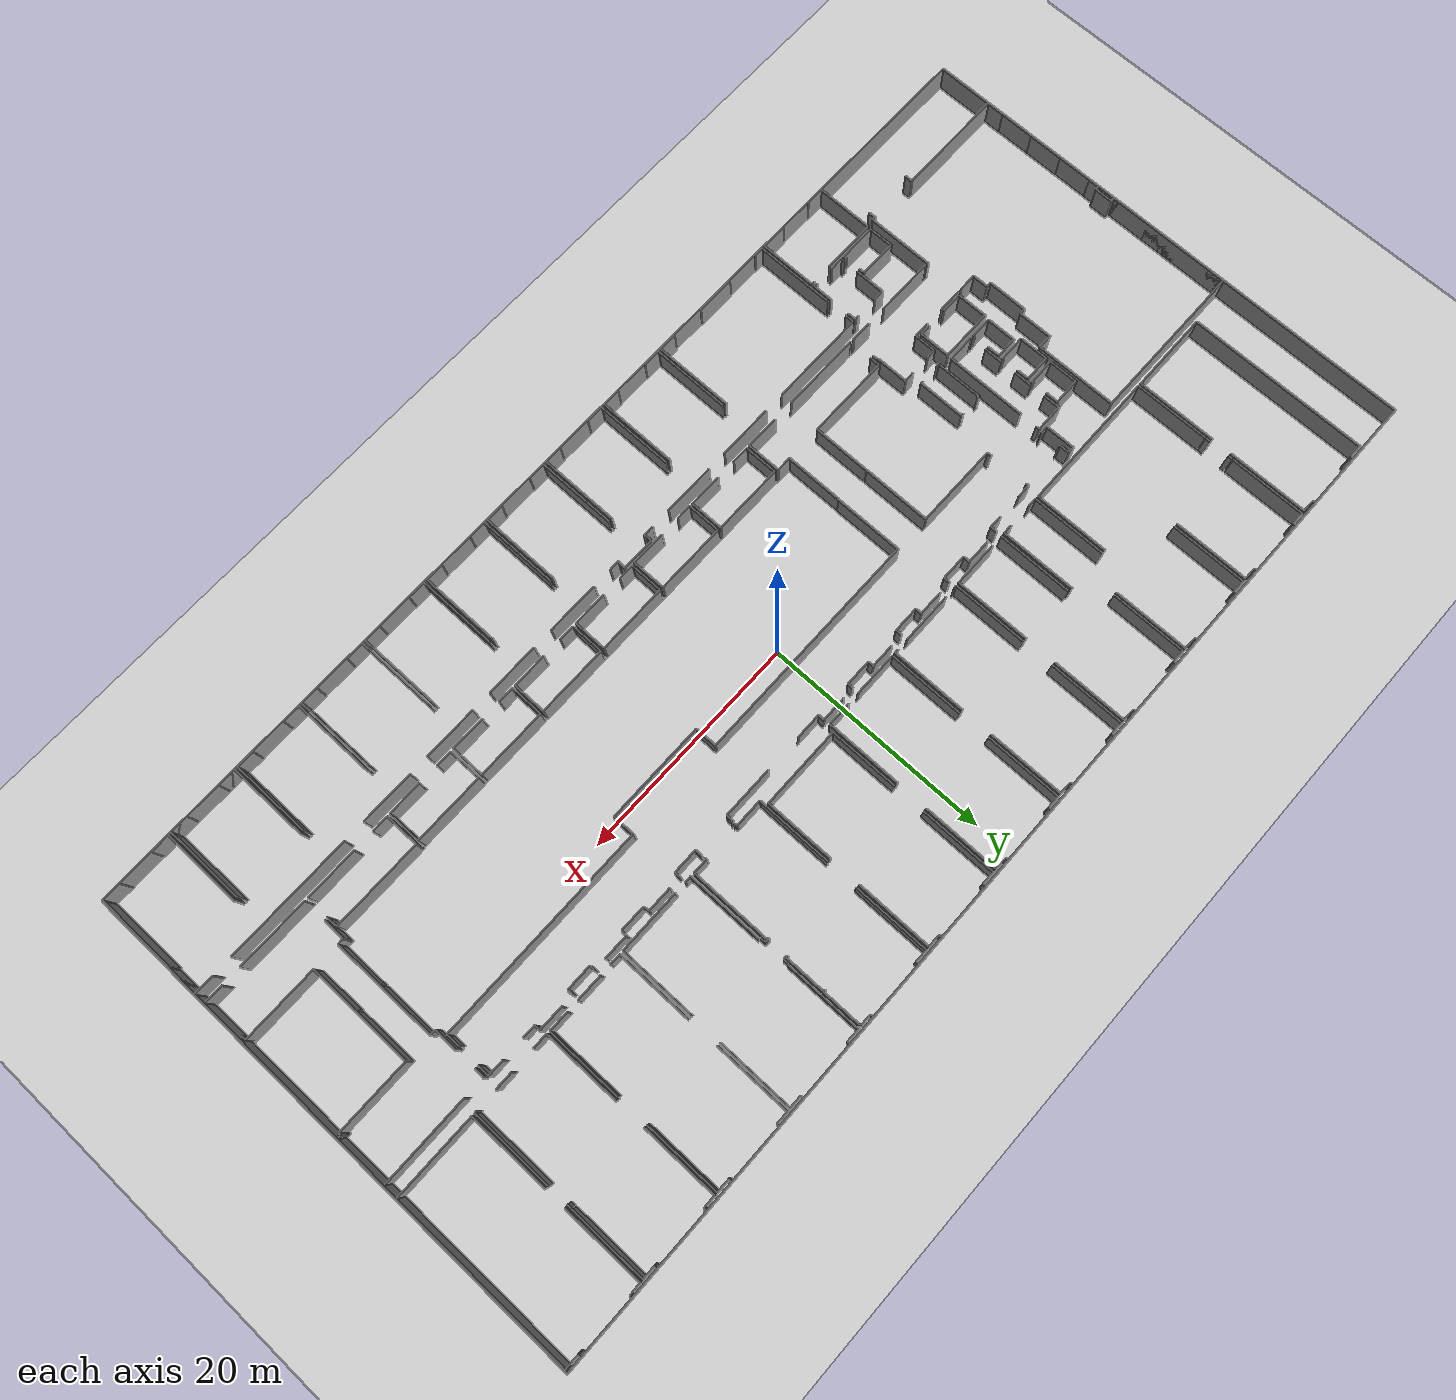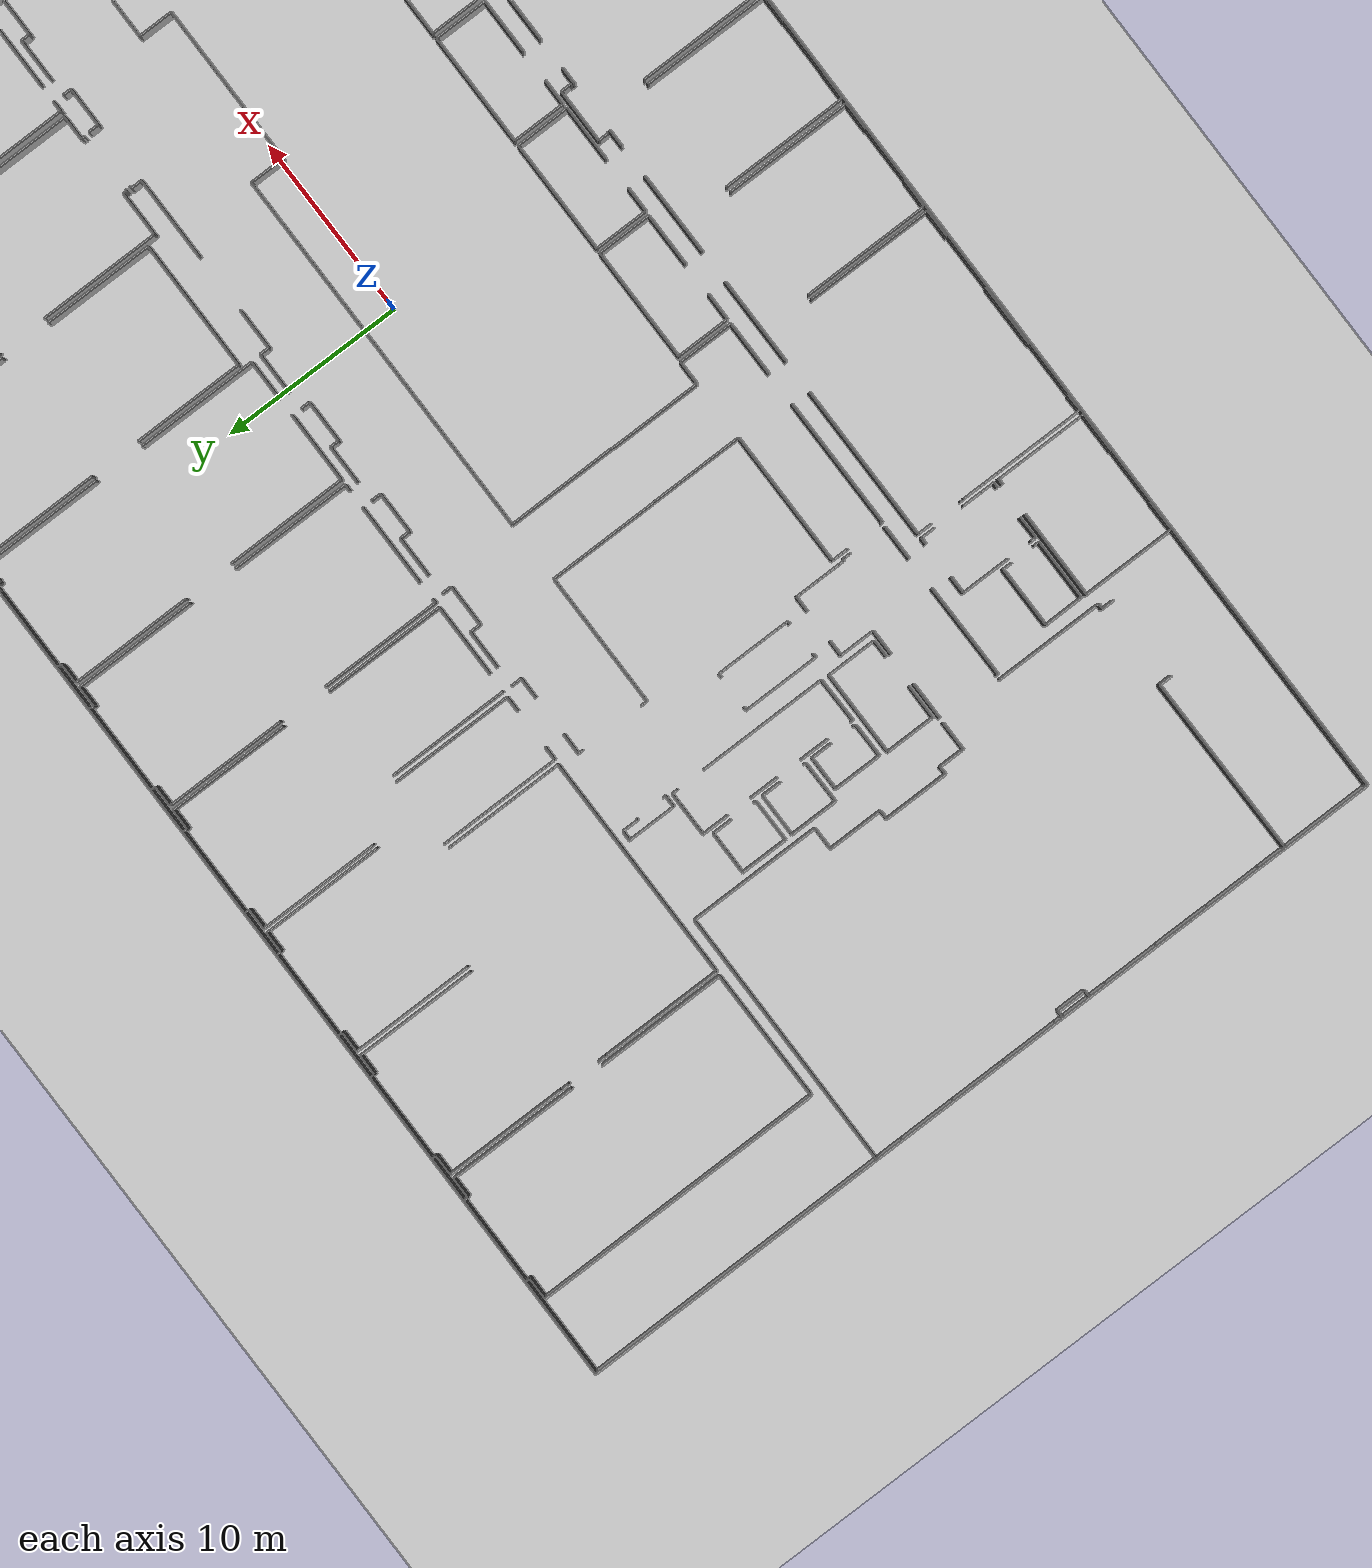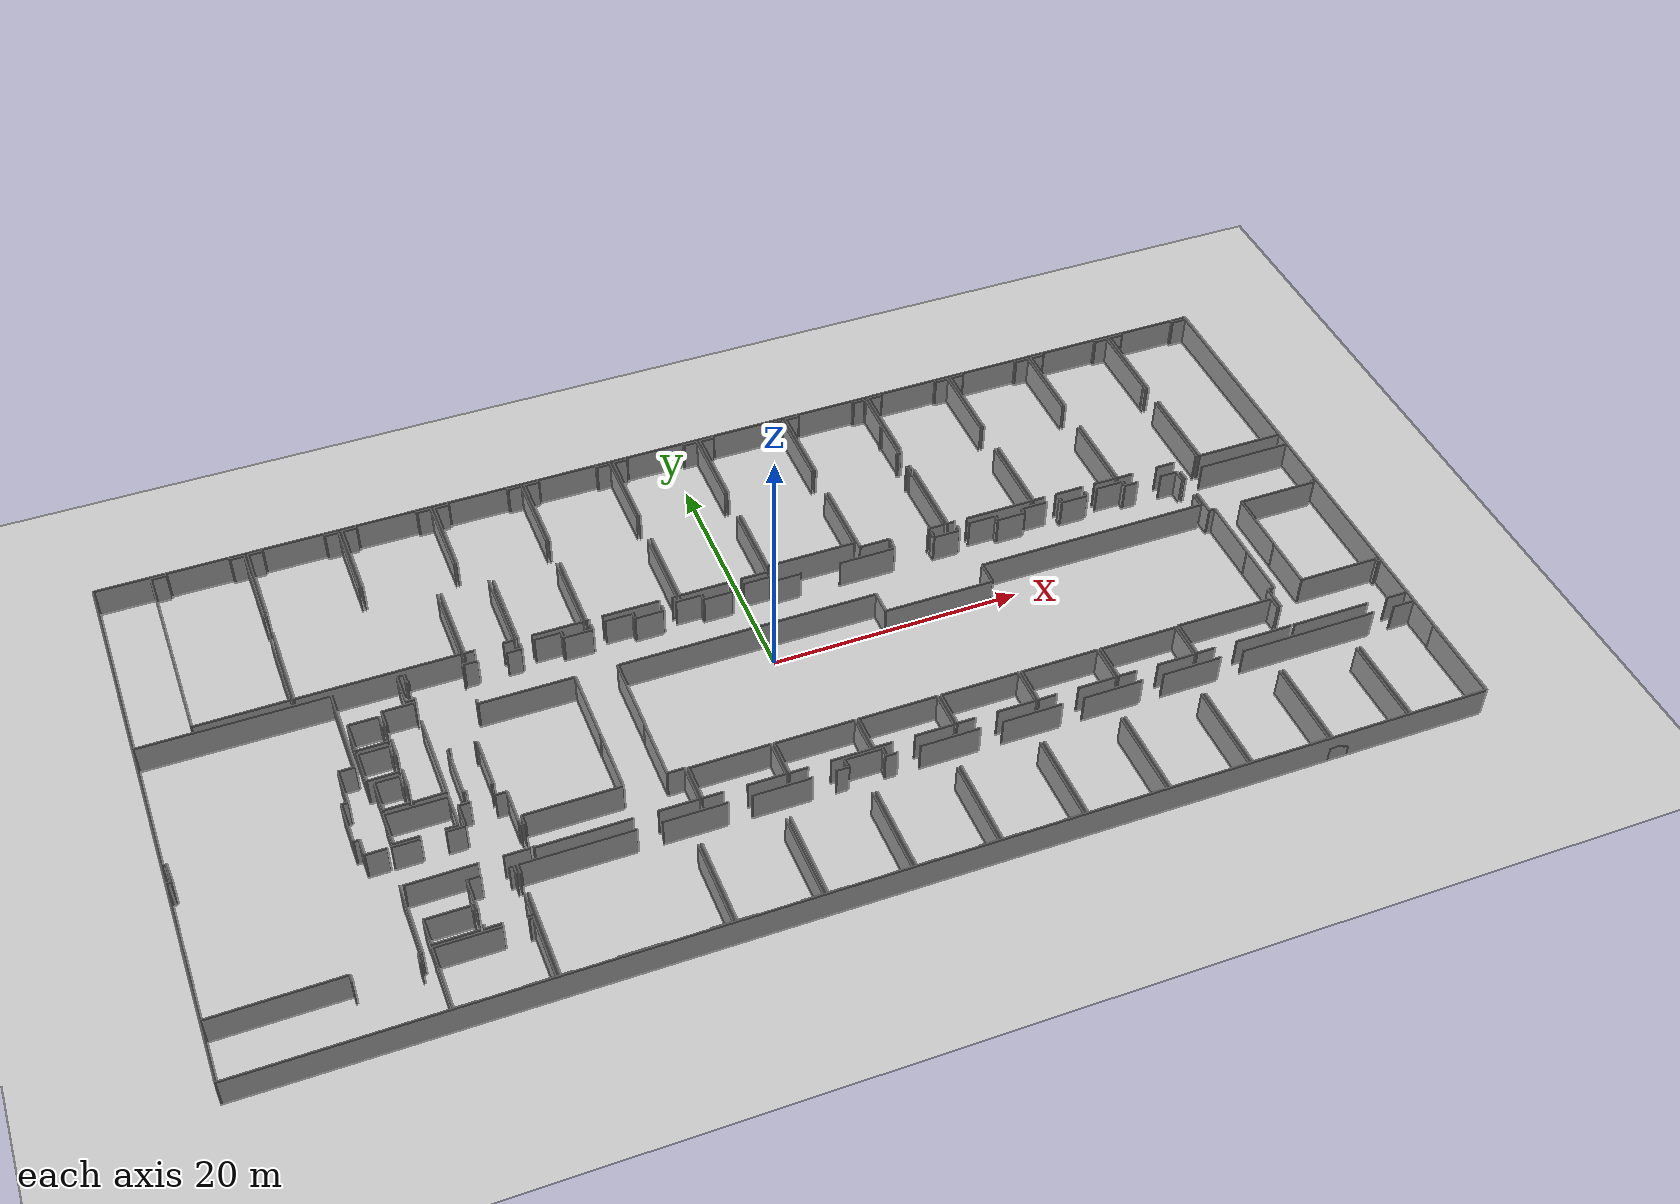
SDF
<sdf version="1.6">
  <world name="default">
    <light name="sun" type="directional">
      <cast_shadows>1</cast_shadows>
      <pose frame="">0 0 10 0 -0 0</pose>
      <diffuse>0.8 0.8 0.8 1</diffuse>
      <specular>0.1 0.1 0.1 1</specular>
      <attenuation>
        <range>1000</range>
        <constant>0.9</constant>
        <linear>0.01</linear>
        <quadratic>0.001</quadratic>
      </attenuation>
      <direction>-0.5 0.5 -1</direction>
    </light>
    <model name="ground_plane">
      <static>1</static>
      <link name="link">
        <collision name="collision">
          <geometry>
            <plane>
              <normal>0 0 1</normal>
              <size>100 100</size>
            </plane>
          </geometry>
          <surface>
            <friction>
              <ode>
                <mu>100</mu>
                <mu2>50</mu2>
              </ode>
              <torsional>
                <ode />
              </torsional>
            </friction>
            <contact>
              <ode />
            </contact>
            <bounce />
          </surface>
          <max_contacts>10</max_contacts>
        </collision>
        <visual name="visual">
          <cast_shadows>0</cast_shadows>
          <geometry>
            <plane>
              <normal>0 0 1</normal>
              <size>100 100</size>
            </plane>
          </geometry>
          <material>
            <script>
              <uri>file://media/materials/scripts/gazebo.material</uri>
              <name>Gazebo/Grey</name>
            </script>
          </material>
        </visual>
        <self_collide>0</self_collide>
        <kinematic>0</kinematic>
        <gravity>1</gravity>
      </link>
    </model>
    <gravity>0 0 -9.8</gravity>
    <magnetic_field>6e-06 2.3e-05 -4.2e-05</magnetic_field>
    <atmosphere type="adiabatic" />
    <physics default="0" name="default_physics" type="ode">
      <max_step_size>0.001</max_step_size>
      <real_time_factor>1</real_time_factor>
      <real_time_update_rate>1000</real_time_update_rate>
    </physics>
    <scene>
      <ambient>0.4 0.4 0.4 1</ambient>
      <background>0.7 0.7 0.7 1</background>
      <shadows>1</shadows>
    </scene>
    <spherical_coordinates>
      <surface_model>EARTH_WGS84</surface_model>
      <latitude_deg>0</latitude_deg>
      <longitude_deg>0</longitude_deg>
      <elevation>0</elevation>
      <heading_deg>0</heading_deg>
    </spherical_coordinates>
  <model name="50045230">
		<static>1</static>
		<link name="Wall_0">
			<collision name="Wall_0_Collision">
				<geometry>
					<box>
						<size>16.1235034977 0.1 2.5</size>
					</box>
				</geometry>
				<pose frame="">8.06175174883 0 1.25 0 0 0</pose>
			</collision>
			<visual name="Wall_0_Visual">
				<pose frame="">8.06175174883 0 1.25 0 0 0</pose>
				<geometry>
					<box>
						<size>16.1235034977 0.1 2.5</size>
					</box>
				</geometry>
				<material>
					<script>
						<uri>file://media/materials/scripts/gazebo.material</uri>
						<name>Gazebo/Grey</name>
					</script>
					<ambient>1 1 1 1</ambient>
				</material>
			</visual>
			<pose frame="">4.35461551157 -16.3647212665 0 0 0 1.57079632679</pose>
		</link>
		<link name="Wall_1">
			<collision name="Wall_1_Collision">
				<geometry>
					<box>
						<size>1.18069750022 0.1 2.5</size>
					</box>
				</geometry>
				<pose frame="">0.590348750111 0 1.25 0 0 0</pose>
			</collision>
			<visual name="Wall_1_Visual">
				<pose frame="">0.590348750111 0 1.25 0 0 0</pose>
				<geometry>
					<box>
						<size>1.18069750022 0.1 2.5</size>
					</box>
				</geometry>
				<material>
					<script>
						<uri>file://media/materials/scripts/gazebo.material</uri>
						<name>Gazebo/Grey</name>
					</script>
					<ambient>1 1 1 1</ambient>
				</material>
			</visual>
			<pose frame="">4.35461551157 -0.241217768863 0 0 0 0.0</pose>
		</link>
		<link name="Wall_2">
			<collision name="Wall_2_Collision">
				<geometry>
					<box>
						<size>0.228522096817 0.1 2.5</size>
					</box>
				</geometry>
				<pose frame="">0.114261048409 0 1.25 0 0 0</pose>
			</collision>
			<visual name="Wall_2_Visual">
				<pose frame="">0.114261048409 0 1.25 0 0 0</pose>
				<geometry>
					<box>
						<size>0.228522096817 0.1 2.5</size>
					</box>
				</geometry>
				<material>
					<script>
						<uri>file://media/materials/scripts/gazebo.material</uri>
						<name>Gazebo/Grey</name>
					</script>
					<ambient>1 1 1 1</ambient>
				</material>
			</visual>
			<pose frame="">5.53531301179 -0.241217768863 0 0 0 1.57079632679</pose>
		</link>
		<link name="Wall_3">
			<collision name="Wall_3_Collision">
				<geometry>
					<box>
						<size>0.23207688499 0.1 2.5</size>
					</box>
				</geometry>
				<pose frame="">0.116038442495 0 1.25 0 0 0</pose>
			</collision>
			<visual name="Wall_3_Visual">
				<pose frame="">0.116038442495 0 1.25 0 0 0</pose>
				<geometry>
					<box>
						<size>0.23207688499 0.1 2.5</size>
					</box>
				</geometry>
				<material>
					<script>
						<uri>file://media/materials/scripts/gazebo.material</uri>
						<name>Gazebo/Grey</name>
					</script>
					<ambient>1 1 1 1</ambient>
				</material>
			</visual>
			<pose frame="">10.4685972552 -0.0126956720454 0 0 0 -1.57079632679</pose>
		</link>
		<link name="Wall_4">
			<collision name="Wall_4_Collision">
				<geometry>
					<box>
						<size>1.14362613785 0.1 2.5</size>
					</box>
				</geometry>
				<pose frame="">0.571813068925 0 1.25 0 0 0</pose>
			</collision>
			<visual name="Wall_4_Visual">
				<pose frame="">0.571813068925 0 1.25 0 0 0</pose>
				<geometry>
					<box>
						<size>1.14362613785 0.1 2.5</size>
					</box>
				</geometry>
				<material>
					<script>
						<uri>file://media/materials/scripts/gazebo.material</uri>
						<name>Gazebo/Grey</name>
					</script>
					<ambient>1 1 1 1</ambient>
				</material>
			</visual>
			<pose frame="">10.4685972552 -0.244772557035 0 0 0 0.0</pose>
		</link>
		<link name="Wall_5">
			<collision name="Wall_5_Collision">
				<geometry>
					<box>
						<size>7.14550509731 0.1 2.5</size>
					</box>
				</geometry>
				<pose frame="">3.57275254866 0 1.25 0 0 0</pose>
			</collision>
			<visual name="Wall_5_Visual">
				<pose frame="">3.57275254866 0 1.25 0 0 0</pose>
				<geometry>
					<box>
						<size>7.14550509731 0.1 2.5</size>
					</box>
				</geometry>
				<material>
					<script>
						<uri>file://media/materials/scripts/gazebo.material</uri>
						<name>Gazebo/Grey</name>
					</script>
					<ambient>1 1 1 1</ambient>
				</material>
			</visual>
			<pose frame="">11.612223393 -0.244772557035 0 0 0 -1.57079632679</pose>
		</link>
		<link name="Wall_6">
			<collision name="Wall_6_Collision">
				<geometry>
					<box>
						<size>7.14321987634 0.1 2.5</size>
					</box>
				</geometry>
				<pose frame="">3.57160993817 0 1.25 0 0 0</pose>
			</collision>
			<visual name="Wall_6_Visual">
				<pose frame="">3.57160993817 0 1.25 0 0 0</pose>
				<geometry>
					<box>
						<size>7.14321987634 0.1 2.5</size>
					</box>
				</geometry>
				<material>
					<script>
						<uri>file://media/materials/scripts/gazebo.material</uri>
						<name>Gazebo/Grey</name>
					</script>
					<ambient>1 1 1 1</ambient>
				</material>
			</visual>
			<pose frame="">11.612223393 -9.19166656087 0 0 0 -1.57079632679</pose>
		</link>
		<link name="Wall_7">
			<collision name="Wall_7_Collision">
				<geometry>
					<box>
						<size>7.25766920425 0.1 2.5</size>
					</box>
				</geometry>
				<pose frame="">3.62883460212 0 1.25 0 0 0</pose>
			</collision>
			<visual name="Wall_7_Visual">
				<pose frame="">3.62883460212 0 1.25 0 0 0</pose>
				<geometry>
					<box>
						<size>7.25766920425 0.1 2.5</size>
					</box>
				</geometry>
				<material>
					<script>
						<uri>file://media/materials/scripts/gazebo.material</uri>
						<name>Gazebo/Grey</name>
					</script>
					<ambient>1 1 1 1</ambient>
				</material>
			</visual>
			<pose frame="">11.612223393 -16.3348864372 0 0 0 -3.13748184163</pose>
		</link>
		<link name="Wall_8">
			<collision name="Wall_8_Collision">
				<geometry>
					<box>
						<size>0.450061574009 0.1 2.5</size>
					</box>
				</geometry>
				<pose frame="">0.225030787005 0 1.25 0 0 0</pose>
			</collision>
			<visual name="Wall_8_Visual">
				<pose frame="">0.225030787005 0 1.25 0 0 0</pose>
				<geometry>
					<box>
						<size>0.450061574009 0.1 2.5</size>
					</box>
				</geometry>
				<material>
					<script>
						<uri>file://media/materials/scripts/gazebo.material</uri>
						<name>Gazebo/Grey</name>
					</script>
					<ambient>1 1 1 1</ambient>
				</material>
			</visual>
			<pose frame="">11.8608046517 -9.64020465423 0 0 0 1.57079632679</pose>
		</link>
		<link name="Wall_9">
			<collision name="Wall_9_Collision">
				<geometry>
					<box>
						<size>0.403976284485 0.1 2.5</size>
					</box>
				</geometry>
				<pose frame="">0.201988142242 0 1.25 0 0 0</pose>
			</collision>
			<visual name="Wall_9_Visual">
				<pose frame="">0.201988142242 0 1.25 0 0 0</pose>
				<geometry>
					<box>
						<size>0.403976284485 0.1 2.5</size>
					</box>
				</geometry>
				<material>
					<script>
						<uri>file://media/materials/scripts/gazebo.material</uri>
						<name>Gazebo/Grey</name>
					</script>
					<ambient>1 1 1 1</ambient>
				</material>
			</visual>
			<pose frame="">11.8608046517 -7.42138205086 0 0 0 1.57079632679</pose>
		</link>
		<link name="Wall_10">
			<collision name="Wall_10_Collision">
				<geometry>
					<box>
						<size>0.306092653015 0.1 2.5</size>
					</box>
				</geometry>
				<pose frame="">0.153046326507 0 1.25 0 0 0</pose>
			</collision>
			<visual name="Wall_10_Visual">
				<pose frame="">0.153046326507 0 1.25 0 0 0</pose>
				<geometry>
					<box>
						<size>0.306092653015 0.1 2.5</size>
					</box>
				</geometry>
				<material>
					<script>
						<uri>file://media/materials/scripts/gazebo.material</uri>
						<name>Gazebo/Grey</name>
					</script>
					<ambient>1 1 1 1</ambient>
				</material>
			</visual>
			<pose frame="">63.6178856628 -7.01740576637 0 0 0 -1.57079632679</pose>
		</link>
		<link name="Wall_11">
			<collision name="Wall_11_Collision">
				<geometry>
					<box>
						<size>0.116927139538 0.1 2.5</size>
					</box>
				</geometry>
				<pose frame="">0.0584635697691 0 1.25 0 0 0</pose>
			</collision>
			<visual name="Wall_11_Visual">
				<pose frame="">0.0584635697691 0 1.25 0 0 0</pose>
				<geometry>
					<box>
						<size>0.116927139538 0.1 2.5</size>
					</box>
				</geometry>
				<material>
					<script>
						<uri>file://media/materials/scripts/gazebo.material</uri>
						<name>Gazebo/Grey</name>
					</script>
					<ambient>1 1 1 1</ambient>
				</material>
			</visual>
			<pose frame="">63.6178856628 -7.32349841939 0 0 0 3.14159265359</pose>
		</link>
		<link name="Wall_12">
			<collision name="Wall_12_Collision">
				<geometry>
					<box>
						<size>0.100168852438 0.1 2.5</size>
					</box>
				</geometry>
				<pose frame="">0.0500844262191 0 1.25 0 0 0</pose>
			</collision>
			<visual name="Wall_12_Visual">
				<pose frame="">0.0500844262191 0 1.25 0 0 0</pose>
				<geometry>
					<box>
						<size>0.100168852438 0.1 2.5</size>
					</box>
				</geometry>
				<material>
					<script>
						<uri>file://media/materials/scripts/gazebo.material</uri>
						<name>Gazebo/Grey</name>
					</script>
					<ambient>1 1 1 1</ambient>
				</material>
			</visual>
			<pose frame="">63.5009585232 -7.32349841939 0 0 0 -1.57079632679</pose>
		</link>
		<link name="Wall_13">
			<collision name="Wall_13_Collision">
				<geometry>
					<box>
						<size>0.317264844415 0.1 2.5</size>
					</box>
				</geometry>
				<pose frame="">0.158632422207 0 1.25 0 0 0</pose>
			</collision>
			<visual name="Wall_13_Visual">
				<pose frame="">0.158632422207 0 1.25 0 0 0</pose>
				<geometry>
					<box>
						<size>0.317264844415 0.1 2.5</size>
					</box>
				</geometry>
				<material>
					<script>
						<uri>file://media/materials/scripts/gazebo.material</uri>
						<name>Gazebo/Grey</name>
					</script>
					<ambient>1 1 1 1</ambient>
				</material>
			</visual>
			<pose frame="">63.5009585232 -7.42366727183 0 0 0 0.0</pose>
		</link>
		<link name="Wall_14">
			<collision name="Wall_14_Collision">
				<geometry>
					<box>
						<size>0.400675409753 0.1 2.5</size>
					</box>
				</geometry>
				<pose frame="">0.200337704876 0 1.25 0 0 0</pose>
			</collision>
			<visual name="Wall_14_Visual">
				<pose frame="">0.200337704876 0 1.25 0 0 0</pose>
				<geometry>
					<box>
						<size>0.400675409753 0.1 2.5</size>
					</box>
				</geometry>
				<material>
					<script>
						<uri>file://media/materials/scripts/gazebo.material</uri>
						<name>Gazebo/Grey</name>
					</script>
					<ambient>1 1 1 1</ambient>
				</material>
			</visual>
			<pose frame="">63.8182233677 -7.42366727183 0 0 0 1.57079632679</pose>
		</link>
		<link name="Wall_15">
			<collision name="Wall_15_Collision">
				<geometry>
					<box>
						<size>0.408673683141 0.1 2.5</size>
					</box>
				</geometry>
				<pose frame="">0.204336841571 0 1.25 0 0 0</pose>
			</collision>
			<visual name="Wall_15_Visual">
				<pose frame="">0.204336841571 0 1.25 0 0 0</pose>
				<geometry>
					<box>
						<size>0.408673683141 0.1 2.5</size>
					</box>
				</geometry>
				<material>
					<script>
						<uri>file://media/materials/scripts/gazebo.material</uri>
						<name>Gazebo/Grey</name>
					</script>
					<ambient>1 1 1 1</ambient>
				</material>
			</visual>
			<pose frame="">85.9985780847 -7.02299186207 0 0 0 -1.57079632679</pose>
		</link>
		<link name="Wall_16">
			<collision name="Wall_16_Collision">
				<geometry>
					<box>
						<size>7.1857503777 0.1 2.5</size>
					</box>
				</geometry>
				<pose frame="">3.59287518885 0 1.25 0 0 0</pose>
			</collision>
			<visual name="Wall_16_Visual">
				<pose frame="">3.59287518885 0 1.25 0 0 0</pose>
				<geometry>
					<box>
						<size>7.1857503777 0.1 2.5</size>
					</box>
				</geometry>
				<material>
					<script>
						<uri>file://media/materials/scripts/gazebo.material</uri>
						<name>Gazebo/Grey</name>
					</script>
					<ambient>1 1 1 1</ambient>
				</material>
			</visual>
			<pose frame="">85.9985780847 -9.19166656087 0 0 0 -1.57079632679</pose>
		</link>
		<link name="Wall_17">
			<collision name="Wall_17_Collision">
				<geometry>
					<box>
						<size>0.150443713738 0.1 2.5</size>
					</box>
				</geometry>
				<pose frame="">0.075221856869 0 1.25 0 0 0</pose>
			</collision>
			<visual name="Wall_17_Visual">
				<pose frame="">0.075221856869 0 1.25 0 0 0</pose>
				<geometry>
					<box>
						<size>0.150443713738 0.1 2.5</size>
					</box>
				</geometry>
				<material>
					<script>
						<uri>file://media/materials/scripts/gazebo.material</uri>
						<name>Gazebo/Grey</name>
					</script>
					<ambient>1 1 1 1</ambient>
				</material>
			</visual>
			<pose frame="">85.9985780847 -16.3774169386 0 0 0 3.14159265359</pose>
		</link>
		<link name="Wall_18">
			<collision name="Wall_18_Collision">
				<geometry>
					<box>
						<size>1.57426333363 0.1 2.5</size>
					</box>
				</geometry>
				<pose frame="">0.787131666815 0 1.25 0 0 0</pose>
			</collision>
			<visual name="Wall_18_Visual">
				<pose frame="">0.787131666815 0 1.25 0 0 0</pose>
				<geometry>
					<box>
						<size>1.57426333363 0.1 2.5</size>
					</box>
				</geometry>
				<material>
					<script>
						<uri>file://media/materials/scripts/gazebo.material</uri>
						<name>Gazebo/Grey</name>
					</script>
					<ambient>1 1 1 1</ambient>
				</material>
			</visual>
			<pose frame="">83.893000876 -16.3774169386 0 0 0 3.14159265359</pose>
		</link>
		<link name="Wall_19">
			<collision name="Wall_19_Collision">
				<geometry>
					<box>
						<size>1.3432021024 0.1 2.5</size>
					</box>
				</geometry>
				<pose frame="">0.671601051202 0 1.25 0 0 0</pose>
			</collision>
			<visual name="Wall_19_Visual">
				<pose frame="">0.671601051202 0 1.25 0 0 0</pose>
				<geometry>
					<box>
						<size>1.3432021024 0.1 2.5</size>
					</box>
				</geometry>
				<material>
					<script>
						<uri>file://media/materials/scripts/gazebo.material</uri>
						<name>Gazebo/Grey</name>
					</script>
					<ambient>1 1 1 1</ambient>
				</material>
			</visual>
			<pose frame="">80.1528558914 -16.3774169386 0 0 0 3.14159265359</pose>
		</link>
		<link name="Wall_20">
			<collision name="Wall_20_Collision">
				<geometry>
					<box>
						<size>6.75409752815 0.1 2.5</size>
					</box>
				</geometry>
				<pose frame="">3.37704876408 0 1.25 0 0 0</pose>
			</collision>
			<visual name="Wall_20_Visual">
				<pose frame="">3.37704876408 0 1.25 0 0 0</pose>
				<geometry>
					<box>
						<size>6.75409752815 0.1 2.5</size>
					</box>
				</geometry>
				<material>
					<script>
						<uri>file://media/materials/scripts/gazebo.material</uri>
						<name>Gazebo/Grey</name>
					</script>
					<ambient>1 1 1 1</ambient>
				</material>
			</visual>
			<pose frame="">78.809653789 -16.3774169386 0 0 0 1.57079632679</pose>
		</link>
		<link name="Wall_21">
			<collision name="Wall_21_Collision">
				<geometry>
					<box>
						<size>0.473294653853 0.1 2.5</size>
					</box>
				</geometry>
				<pose frame="">0.236647326926 0 1.25 0 0 0</pose>
			</collision>
			<visual name="Wall_21_Visual">
				<pose frame="">0.236647326926 0 1.25 0 0 0</pose>
				<geometry>
					<box>
						<size>0.473294653853 0.1 2.5</size>
					</box>
				</geometry>
				<material>
					<script>
						<uri>file://media/materials/scripts/gazebo.material</uri>
						<name>Gazebo/Grey</name>
					</script>
					<ambient>1 1 1 1</ambient>
				</material>
			</visual>
			<pose frame="">63.813525969 -9.62331941041 0 0 0 1.57079632679</pose>
		</link>
		<link name="Wall_22">
			<collision name="Wall_22_Collision">
				<geometry>
					<box>
						<size>0.316757017533 0.1 2.5</size>
					</box>
				</geometry>
				<pose frame="">0.158378508766 0 1.25 0 0 0</pose>
			</collision>
			<visual name="Wall_22_Visual">
				<pose frame="">0.158378508766 0 1.25 0 0 0</pose>
				<geometry>
					<box>
						<size>0.316757017533 0.1 2.5</size>
					</box>
				</geometry>
				<material>
					<script>
						<uri>file://media/materials/scripts/gazebo.material</uri>
						<name>Gazebo/Grey</name>
					</script>
					<ambient>1 1 1 1</ambient>
				</material>
			</visual>
			<pose frame="">63.813525969 -9.15002475656 0 0 0 3.14159265359</pose>
		</link>
		<link name="Wall_23">
			<collision name="Wall_23_Collision">
				<geometry>
					<box>
						<size>0.13432021024 0.1 2.5</size>
					</box>
				</geometry>
				<pose frame="">0.0671601051202 0 1.25 0 0 0</pose>
			</collision>
			<visual name="Wall_23_Visual">
				<pose frame="">0.0671601051202 0 1.25 0 0 0</pose>
				<geometry>
					<box>
						<size>0.13432021024 0.1 2.5</size>
					</box>
				</geometry>
				<material>
					<script>
						<uri>file://media/materials/scripts/gazebo.material</uri>
						<name>Gazebo/Grey</name>
					</script>
					<ambient>1 1 1 1</ambient>
				</material>
			</visual>
			<pose frame="">63.4967689515 -9.15002475656 0 0 0 -1.57079632679</pose>
		</link>
		<link name="Wall_24">
			<collision name="Wall_24_Collision">
				<geometry>
					<box>
						<size>0.143968920995 0.1 2.5</size>
					</box>
				</geometry>
				<pose frame="">0.0719844604974 0 1.25 0 0 0</pose>
			</collision>
			<visual name="Wall_24_Visual">
				<pose frame="">0.0719844604974 0 1.25 0 0 0</pose>
				<geometry>
					<box>
						<size>0.143968920995 0.1 2.5</size>
					</box>
				</geometry>
				<material>
					<script>
						<uri>file://media/materials/scripts/gazebo.material</uri>
						<name>Gazebo/Grey</name>
					</script>
					<ambient>1 1 1 1</ambient>
				</material>
			</visual>
			<pose frame="">63.4967689515 -9.2843449668 0 0 0 0.0</pose>
		</link>
		<link name="Wall_25">
			<collision name="Wall_25_Collision">
				<geometry>
					<box>
						<size>0.336054439042 0.1 2.5</size>
					</box>
				</geometry>
				<pose frame="">0.168027219521 0 1.25 0 0 0</pose>
			</collision>
			<visual name="Wall_25_Visual">
				<pose frame="">0.168027219521 0 1.25 0 0 0</pose>
				<geometry>
					<box>
						<size>0.336054439042 0.1 2.5</size>
					</box>
				</geometry>
				<material>
					<script>
						<uri>file://media/materials/scripts/gazebo.material</uri>
						<name>Gazebo/Grey</name>
					</script>
					<ambient>1 1 1 1</ambient>
				</material>
			</visual>
			<pose frame="">63.6407378725 -9.2843449668 0 0 0 -1.57079632679</pose>
		</link>
		<link name="Wall_26">
			<collision name="Wall_26_Collision">
				<geometry>
					<box>
						<size>6.72553226605 0.1 2.5</size>
					</box>
				</geometry>
				<pose frame="">3.36276613303 0 1.25 0 0 0</pose>
			</collision>
			<visual name="Wall_26_Visual">
				<pose frame="">3.36276613303 0 1.25 0 0 0</pose>
				<geometry>
					<box>
						<size>6.72553226605 0.1 2.5</size>
					</box>
				</geometry>
				<material>
					<script>
						<uri>file://media/materials/scripts/gazebo.material</uri>
						<name>Gazebo/Grey</name>
					</script>
					<ambient>1 1 1 1</ambient>
				</material>
			</visual>
			<pose frame="">28.5077507078 -9.62039940584 0 0 0 -1.57079632679</pose>
		</link>
		<link name="Wall_27">
			<collision name="Wall_27_Collision">
				<geometry>
					<box>
						<size>0.855434382419 0.1 2.5</size>
					</box>
				</geometry>
				<pose frame="">0.42771719121 0 1.25 0 0 0</pose>
			</collision>
			<visual name="Wall_27_Visual">
				<pose frame="">0.42771719121 0 1.25 0 0 0</pose>
				<geometry>
					<box>
						<size>0.855434382419 0.1 2.5</size>
					</box>
				</geometry>
				<material>
					<script>
						<uri>file://media/materials/scripts/gazebo.material</uri>
						<name>Gazebo/Grey</name>
					</script>
					<ambient>1 1 1 1</ambient>
				</material>
			</visual>
			<pose frame="">28.5077507078 -16.3459316719 0 0 0 3.14159265359</pose>
		</link>
		<link name="Wall_28">
			<collision name="Wall_28_Collision">
				<geometry>
					<box>
						<size>0.772785557403 0.1 2.5</size>
					</box>
				</geometry>
				<pose frame="">0.386392778702 0 1.25 0 0 0</pose>
			</collision>
			<visual name="Wall_28_Visual">
				<pose frame="">0.386392778702 0 1.25 0 0 0</pose>
				<geometry>
					<box>
						<size>0.772785557403 0.1 2.5</size>
					</box>
				</geometry>
				<material>
					<script>
						<uri>file://media/materials/scripts/gazebo.material</uri>
						<name>Gazebo/Grey</name>
					</script>
					<ambient>1 1 1 1</ambient>
				</material>
			</visual>
			<pose frame="">25.4884659819 -16.3459316719 0 0 0 3.14159265359</pose>
		</link>
		<link name="Wall_29">
			<collision name="Wall_29_Collision">
				<geometry>
					<box>
						<size>6.701029619 0.1 2.5</size>
					</box>
				</geometry>
				<pose frame="">3.3505148095 0 1.25 0 0 0</pose>
			</collision>
			<visual name="Wall_29_Visual">
				<pose frame="">3.3505148095 0 1.25 0 0 0</pose>
				<geometry>
					<box>
						<size>6.701029619 0.1 2.5</size>
					</box>
				</geometry>
				<material>
					<script>
						<uri>file://media/materials/scripts/gazebo.material</uri>
						<name>Gazebo/Grey</name>
					</script>
					<ambient>1 1 1 1</ambient>
				</material>
			</visual>
			<pose frame="">24.7156804245 -16.3459316719 0 0 0 1.57079632679</pose>
		</link>
		<link name="Wall_30">
			<collision name="Wall_30_Collision">
				<geometry>
					<box>
						<size>6.68896873056 0.1 2.5</size>
					</box>
				</geometry>
				<pose frame="">3.34448436528 0 1.25 0 0 0</pose>
			</collision>
			<visual name="Wall_30_Visual">
				<pose frame="">3.34448436528 0 1.25 0 0 0</pose>
				<geometry>
					<box>
						<size>6.68896873056 0.1 2.5</size>
					</box>
				</geometry>
				<material>
					<script>
						<uri>file://media/materials/scripts/gazebo.material</uri>
						<name>Gazebo/Grey</name>
					</script>
					<ambient>1 1 1 1</ambient>
				</material>
			</visual>
			<pose frame="">11.869310752 -6.92904388894 0 0 0 1.57079632679</pose>
		</link>
		<link name="Wall_31">
			<collision name="Wall_31_Collision">
				<geometry>
					<box>
						<size>1.11658435639 0.1 2.5</size>
					</box>
				</geometry>
				<pose frame="">0.558292178196 0 1.25 0 0 0</pose>
			</collision>
			<visual name="Wall_31_Visual">
				<pose frame="">0.558292178196 0 1.25 0 0 0</pose>
				<geometry>
					<box>
						<size>1.11658435639 0.1 2.5</size>
					</box>
				</geometry>
				<material>
					<script>
						<uri>file://media/materials/scripts/gazebo.material</uri>
						<name>Gazebo/Grey</name>
					</script>
					<ambient>1 1 1 1</ambient>
				</material>
			</visual>
			<pose frame="">11.869310752 -0.240075158379 0 0 0 0.0</pose>
		</link>
		<link name="Wall_32">
			<collision name="Wall_32_Collision">
				<geometry>
					<box>
						<size>0.232330798431 0.1 2.5</size>
					</box>
				</geometry>
				<pose frame="">0.116165399215 0 1.25 0 0 0</pose>
			</collision>
			<visual name="Wall_32_Visual">
				<pose frame="">0.116165399215 0 1.25 0 0 0</pose>
				<geometry>
					<box>
						<size>0.232330798431 0.1 2.5</size>
					</box>
				</geometry>
				<material>
					<script>
						<uri>file://media/materials/scripts/gazebo.material</uri>
						<name>Gazebo/Grey</name>
					</script>
					<ambient>1 1 1 1</ambient>
				</material>
			</visual>
			<pose frame="">12.9858951084 -0.240075158379 0 0 0 1.57079632679</pose>
		</link>
		<link name="Wall_33">
			<collision name="Wall_33_Collision">
				<geometry>
					<box>
						<size>0.253913440908 0.1 2.5</size>
					</box>
				</geometry>
				<pose frame="">0.126956720454 0 1.25 0 0 0</pose>
			</collision>
			<visual name="Wall_33_Visual">
				<pose frame="">0.126956720454 0 1.25 0 0 0</pose>
				<geometry>
					<box>
						<size>0.253913440908 0.1 2.5</size>
					</box>
				</geometry>
				<material>
					<script>
						<uri>file://media/materials/scripts/gazebo.material</uri>
						<name>Gazebo/Grey</name>
					</script>
					<ambient>1 1 1 1</ambient>
				</material>
			</visual>
			<pose frame="">17.9011514975 -0.00774435994769 0 0 0 -1.57079632679</pose>
		</link>
		<link name="Wall_34">
			<collision name="Wall_34_Collision">
				<geometry>
					<box>
						<size>1.14540353194 0.1 2.5</size>
					</box>
				</geometry>
				<pose frame="">0.572701765968 0 1.25 0 0 0</pose>
			</collision>
			<visual name="Wall_34_Visual">
				<pose frame="">0.572701765968 0 1.25 0 0 0</pose>
				<geometry>
					<box>
						<size>1.14540353194 0.1 2.5</size>
					</box>
				</geometry>
				<material>
					<script>
						<uri>file://media/materials/scripts/gazebo.material</uri>
						<name>Gazebo/Grey</name>
					</script>
					<ambient>1 1 1 1</ambient>
				</material>
			</visual>
			<pose frame="">17.9011514975 -0.261657800856 0 0 0 0.0</pose>
		</link>
		<link name="Wall_35">
			<collision name="Wall_35_Collision">
				<geometry>
					<box>
						<size>6.66738811994 0.1 2.5</size>
					</box>
				</geometry>
				<pose frame="">3.33369405997 0 1.25 0 0 0</pose>
			</collision>
			<visual name="Wall_35_Visual">
				<pose frame="">3.33369405997 0 1.25 0 0 0</pose>
				<geometry>
					<box>
						<size>6.66738811994 0.1 2.5</size>
					</box>
				</geometry>
				<material>
					<script>
						<uri>file://media/materials/scripts/gazebo.material</uri>
						<name>Gazebo/Grey</name>
					</script>
					<ambient>1 1 1 1</ambient>
				</material>
			</visual>
			<pose frame="">19.0465550294 -0.261657800856 0 0 0 -1.57157702622</pose>
		</link>
		<link name="Wall_36">
			<collision name="Wall_36_Collision">
				<geometry>
					<box>
						<size>6.70242614293 0.1 2.5</size>
					</box>
				</geometry>
				<pose frame="">3.35121307146 0 1.25 0 0 0</pose>
			</collision>
			<visual name="Wall_36_Visual">
				<pose frame="">3.35121307146 0 1.25 0 0 0</pose>
				<geometry>
					<box>
						<size>6.70242614293 0.1 2.5</size>
					</box>
				</geometry>
				<material>
					<script>
						<uri>file://media/materials/scripts/gazebo.material</uri>
						<name>Gazebo/Grey</name>
					</script>
					<ambient>1 1 1 1</ambient>
				</material>
			</visual>
			<pose frame="">19.3159571902 -6.95722828088 0 0 0 1.57079632679</pose>
		</link>
		<link name="Wall_37">
			<collision name="Wall_37_Collision">
				<geometry>
					<box>
						<size>1.11493391903 0.1 2.5</size>
					</box>
				</geometry>
				<pose frame="">0.557466959514 0 1.25 0 0 0</pose>
			</collision>
			<visual name="Wall_37_Visual">
				<pose frame="">0.557466959514 0 1.25 0 0 0</pose>
				<geometry>
					<box>
						<size>1.11493391903 0.1 2.5</size>
					</box>
				</geometry>
				<material>
					<script>
						<uri>file://media/materials/scripts/gazebo.material</uri>
						<name>Gazebo/Grey</name>
					</script>
					<ambient>1 1 1 1</ambient>
				</material>
			</visual>
			<pose frame="">19.3159571902 -0.254802137951 0 0 0 0.0</pose>
		</link>
		<link name="Wall_38">
			<collision name="Wall_38_Collision">
				<geometry>
					<box>
						<size>0.230553404344 0.1 2.5</size>
					</box>
				</geometry>
				<pose frame="">0.115276702172 0 1.25 0 0 0</pose>
			</collision>
			<visual name="Wall_38_Visual">
				<pose frame="">0.115276702172 0 1.25 0 0 0</pose>
				<geometry>
					<box>
						<size>0.230553404344 0.1 2.5</size>
					</box>
				</geometry>
				<material>
					<script>
						<uri>file://media/materials/scripts/gazebo.material</uri>
						<name>Gazebo/Grey</name>
					</script>
					<ambient>1 1 1 1</ambient>
				</material>
			</visual>
			<pose frame="">20.4308911092 -0.254802137951 0 0 0 1.57079632679</pose>
		</link>
		<link name="Wall_39">
			<collision name="Wall_39_Collision">
				<geometry>
					<box>
						<size>0.230553404344 0.1 2.5</size>
					</box>
				</geometry>
				<pose frame="">0.115276702172 0 1.25 0 0 0</pose>
			</collision>
			<visual name="Wall_39_Visual">
				<pose frame="">0.115276702172 0 1.25 0 0 0</pose>
				<geometry>
					<box>
						<size>0.230553404344 0.1 2.5</size>
					</box>
				</geometry>
				<material>
					<script>
						<uri>file://media/materials/scripts/gazebo.material</uri>
						<name>Gazebo/Grey</name>
					</script>
					<ambient>1 1 1 1</ambient>
				</material>
			</visual>
			<pose frame="">25.3323092158 -0.0242487336067 0 0 0 -1.57079632679</pose>
		</link>
		<link name="Wall_40">
			<collision name="Wall_40_Collision">
				<geometry>
					<box>
						<size>1.15809920398 0.1 2.5</size>
					</box>
				</geometry>
				<pose frame="">0.579049601991 0 1.25 0 0 0</pose>
			</collision>
			<visual name="Wall_40_Visual">
				<pose frame="">0.579049601991 0 1.25 0 0 0</pose>
				<geometry>
					<box>
						<size>1.15809920398 0.1 2.5</size>
					</box>
				</geometry>
				<material>
					<script>
						<uri>file://media/materials/scripts/gazebo.material</uri>
						<name>Gazebo/Grey</name>
					</script>
					<ambient>1 1 1 1</ambient>
				</material>
			</visual>
			<pose frame="">25.3323092158 -0.254802137951 0 0 0 0.0</pose>
		</link>
		<link name="Wall_41">
			<collision name="Wall_41_Collision">
				<geometry>
					<box>
						<size>6.70245073078 0.1 2.5</size>
					</box>
				</geometry>
				<pose frame="">3.35122536539 0 1.25 0 0 0</pose>
			</collision>
			<visual name="Wall_41_Visual">
				<pose frame="">3.35122536539 0 1.25 0 0 0</pose>
				<geometry>
					<box>
						<size>6.70245073078 0.1 2.5</size>
					</box>
				</geometry>
				<material>
					<script>
						<uri>file://media/materials/scripts/gazebo.material</uri>
						<name>Gazebo/Grey</name>
					</script>
					<ambient>1 1 1 1</ambient>
				</material>
			</visual>
			<pose frame="">26.4904084198 -0.254802137951 0 0 0 -1.56808764098</pose>
		</link>
		<link name="Wall_42">
			<collision name="Wall_42_Collision">
				<geometry>
					<box>
						<size>6.6383129991 0.1 2.5</size>
					</box>
				</geometry>
				<pose frame="">3.31915649955 0 1.25 0 0 0</pose>
			</collision>
			<visual name="Wall_42_Visual">
				<pose frame="">3.31915649955 0 1.25 0 0 0</pose>
				<geometry>
					<box>
						<size>6.6383129991 0.1 2.5</size>
					</box>
				</geometry>
				<material>
					<script>
						<uri>file://media/materials/scripts/gazebo.material</uri>
						<name>Gazebo/Grey</name>
					</script>
					<ambient>1 1 1 1</ambient>
				</material>
			</visual>
			<pose frame="">26.7381009814 -6.91812561098 0 0 0 1.57079632679</pose>
		</link>
		<link name="Wall_43">
			<collision name="Wall_43_Collision">
				<geometry>
					<box>
						<size>1.1339774271 0.1 2.5</size>
					</box>
				</geometry>
				<pose frame="">0.566988713548 0 1.25 0 0 0</pose>
			</collision>
			<visual name="Wall_43_Visual">
				<pose frame="">0.566988713548 0 1.25 0 0 0</pose>
				<geometry>
					<box>
						<size>1.1339774271 0.1 2.5</size>
					</box>
				</geometry>
				<material>
					<script>
						<uri>file://media/materials/scripts/gazebo.material</uri>
						<name>Gazebo/Grey</name>
					</script>
					<ambient>1 1 1 1</ambient>
				</material>
			</visual>
			<pose frame="">26.7381009814 -0.279812611881 0 0 0 0.0</pose>
		</link>
		<link name="Wall_44">
			<collision name="Wall_44_Collision">
				<geometry>
					<box>
						<size>0.272068251933 0.1 2.5</size>
					</box>
				</geometry>
				<pose frame="">0.136034125966 0 1.25 0 0 0</pose>
			</collision>
			<visual name="Wall_44_Visual">
				<pose frame="">0.136034125966 0 1.25 0 0 0</pose>
				<geometry>
					<box>
						<size>0.272068251933 0.1 2.5</size>
					</box>
				</geometry>
				<material>
					<script>
						<uri>file://media/materials/scripts/gazebo.material</uri>
						<name>Gazebo/Grey</name>
					</script>
					<ambient>1 1 1 1</ambient>
				</material>
			</visual>
			<pose frame="">27.8720784085 -0.279812611881 0 0 0 1.57079632679</pose>
		</link>
		<link name="Wall_45">
			<collision name="Wall_45_Collision">
				<geometry>
					<box>
						<size>0.252516916983 0.1 2.5</size>
					</box>
				</geometry>
				<pose frame="">0.126258458492 0 1.25 0 0 0</pose>
			</collision>
			<visual name="Wall_45_Visual">
				<pose frame="">0.126258458492 0 1.25 0 0 0</pose>
				<geometry>
					<box>
						<size>0.252516916983 0.1 2.5</size>
					</box>
				</geometry>
				<material>
					<script>
						<uri>file://media/materials/scripts/gazebo.material</uri>
						<name>Gazebo/Grey</name>
					</script>
					<ambient>1 1 1 1</ambient>
				</material>
			</visual>
			<pose frame="">32.7750199957 -0.00774435994769 0 0 0 -1.57079632679</pose>
		</link>
		<link name="Wall_46">
			<collision name="Wall_46_Collision">
				<geometry>
					<box>
						<size>1.14159483032 0.1 2.5</size>
					</box>
				</geometry>
				<pose frame="">0.570797415161 0 1.25 0 0 0</pose>
			</collision>
			<visual name="Wall_46_Visual">
				<pose frame="">0.570797415161 0 1.25 0 0 0</pose>
				<geometry>
					<box>
						<size>1.14159483032 0.1 2.5</size>
					</box>
				</geometry>
				<material>
					<script>
						<uri>file://media/materials/scripts/gazebo.material</uri>
						<name>Gazebo/Grey</name>
					</script>
					<ambient>1 1 1 1</ambient>
				</material>
			</visual>
			<pose frame="">32.7750199957 -0.260261276931 0 0 0 0.0</pose>
		</link>
		<link name="Wall_47">
			<collision name="Wall_47_Collision">
				<geometry>
					<box>
						<size>6.65786535204 0.1 2.5</size>
					</box>
				</geometry>
				<pose frame="">3.32893267602 0 1.25 0 0 0</pose>
			</collision>
			<visual name="Wall_47_Visual">
				<pose frame="">3.32893267602 0 1.25 0 0 0</pose>
				<geometry>
					<box>
						<size>6.65786535204 0.1 2.5</size>
					</box>
				</geometry>
				<material>
					<script>
						<uri>file://media/materials/scripts/gazebo.material</uri>
						<name>Gazebo/Grey</name>
					</script>
					<ambient>1 1 1 1</ambient>
				</material>
			</visual>
			<pose frame="">33.916614826 -0.260261276931 0 0 0 -1.57024333497</pose>
		</link>
		<link name="Wall_48">
			<collision name="Wall_48_Collision">
				<geometry>
					<box>
						<size>6.68135132733 0.1 2.5</size>
					</box>
				</geometry>
				<pose frame="">3.34067566367 0 1.25 0 0 0</pose>
			</collision>
			<visual name="Wall_48_Visual">
				<pose frame="">3.34067566367 0 1.25 0 0 0</pose>
				<geometry>
					<box>
						<size>6.68135132733 0.1 2.5</size>
					</box>
				</geometry>
				<material>
					<script>
						<uri>file://media/materials/scripts/gazebo.material</uri>
						<name>Gazebo/Grey</name>
					</script>
					<ambient>1 1 1 1</ambient>
				</material>
			</visual>
			<pose frame="">34.1743369685 -6.9511343583 0 0 0 1.57079632679</pose>
		</link>
		<link name="Wall_49">
			<collision name="Wall_49_Collision">
				<geometry>
					<box>
						<size>1.13677047495 0.1 2.5</size>
					</box>
				</geometry>
				<pose frame="">0.568385237473 0 1.25 0 0 0</pose>
			</collision>
			<visual name="Wall_49_Visual">
				<pose frame="">0.568385237473 0 1.25 0 0 0</pose>
				<geometry>
					<box>
						<size>1.13677047495 0.1 2.5</size>
					</box>
				</geometry>
				<material>
					<script>
						<uri>file://media/materials/scripts/gazebo.material</uri>
						<name>Gazebo/Grey</name>
					</script>
					<ambient>1 1 1 1</ambient>
				</material>
			</visual>
			<pose frame="">34.1743369685 -0.269783030965 0 0 0 0.0</pose>
		</link>
		<link name="Wall_50">
			<collision name="Wall_50_Collision">
				<geometry>
					<box>
						<size>0.242106465906 0.1 2.5</size>
					</box>
				</geometry>
				<pose frame="">0.121053232953 0 1.25 0 0 0</pose>
			</collision>
			<visual name="Wall_50_Visual">
				<pose frame="">0.121053232953 0 1.25 0 0 0</pose>
				<geometry>
					<box>
						<size>0.242106465906 0.1 2.5</size>
					</box>
				</geometry>
				<material>
					<script>
						<uri>file://media/materials/scripts/gazebo.material</uri>
						<name>Gazebo/Grey</name>
					</script>
					<ambient>1 1 1 1</ambient>
				</material>
			</visual>
			<pose frame="">35.3111074435 -0.269783030965 0 0 0 1.57079632679</pose>
		</link>
		<link name="Wall_51">
			<collision name="Wall_51_Collision">
				<geometry>
					<box>
						<size>0.242106465906 0.1 2.5</size>
					</box>
				</geometry>
				<pose frame="">0.121053232953 0 1.25 0 0 0</pose>
			</collision>
			<visual name="Wall_51_Visual">
				<pose frame="">0.121053232953 0 1.25 0 0 0</pose>
				<geometry>
					<box>
						<size>0.242106465906 0.1 2.5</size>
					</box>
				</geometry>
				<material>
					<script>
						<uri>file://media/materials/scripts/gazebo.material</uri>
						<name>Gazebo/Grey</name>
					</script>
					<ambient>1 1 1 1</ambient>
				</material>
			</visual>
			<pose frame="">40.2111290261 -0.027676565059 0 0 0 -1.57079632679</pose>
		</link>
		<link name="Wall_52">
			<collision name="Wall_52_Collision">
				<geometry>
					<box>
						<size>1.1520052814 0.1 2.5</size>
					</box>
				</geometry>
				<pose frame="">0.5760026407 0 1.25 0 0 0</pose>
			</collision>
			<visual name="Wall_52_Visual">
				<pose frame="">0.5760026407 0 1.25 0 0 0</pose>
				<geometry>
					<box>
						<size>1.1520052814 0.1 2.5</size>
					</box>
				</geometry>
				<material>
					<script>
						<uri>file://media/materials/scripts/gazebo.material</uri>
						<name>Gazebo/Grey</name>
					</script>
					<ambient>1 1 1 1</ambient>
				</material>
			</visual>
			<pose frame="">40.2111290261 -0.269783030965 0 0 0 0.0</pose>
		</link>
		<link name="Wall_53">
			<collision name="Wall_53_Collision">
				<geometry>
					<box>
						<size>6.68136131582 0.1 2.5</size>
					</box>
				</geometry>
				<pose frame="">3.34068065791 0 1.25 0 0 0</pose>
			</collision>
			<visual name="Wall_53_Visual">
				<pose frame="">3.34068065791 0 1.25 0 0 0</pose>
				<geometry>
					<box>
						<size>6.68136131582 0.1 2.5</size>
					</box>
				</geometry>
				<material>
					<script>
						<uri>file://media/materials/scripts/gazebo.material</uri>
						<name>Gazebo/Grey</name>
					</script>
					<ambient>1 1 1 1</ambient>
				</material>
			</visual>
			<pose frame="">41.3631343075 -0.269783030965 0 0 0 -1.56906717808</pose>
		</link>
		<link name="Wall_54">
			<collision name="Wall_54_Collision">
				<geometry>
					<box>
						<size>6.68554089911 0.1 2.5</size>
					</box>
				</geometry>
				<pose frame="">3.34277044955 0 1.25 0 0 0</pose>
			</collision>
			<visual name="Wall_54_Visual">
				<pose frame="">3.34277044955 0 1.25 0 0 0</pose>
				<geometry>
					<box>
						<size>6.68554089911 0.1 2.5</size>
					</box>
				</geometry>
				<material>
					<script>
						<uri>file://media/materials/scripts/gazebo.material</uri>
						<name>Gazebo/Grey</name>
					</script>
					<ambient>1 1 1 1</ambient>
				</material>
			</visual>
			<pose frame="">41.6302512473 -6.94008912362 0 0 0 1.57079632679</pose>
		</link>
		<link name="Wall_55">
			<collision name="Wall_55_Collision">
				<geometry>
					<box>
						<size>1.11671131311 0.1 2.5</size>
					</box>
				</geometry>
				<pose frame="">0.558355656557 0 1.25 0 0 0</pose>
			</collision>
			<visual name="Wall_55_Visual">
				<pose frame="">0.558355656557 0 1.25 0 0 0</pose>
				<geometry>
					<box>
						<size>1.11671131311 0.1 2.5</size>
					</box>
				</geometry>
				<material>
					<script>
						<uri>file://media/materials/scripts/gazebo.material</uri>
						<name>Gazebo/Grey</name>
					</script>
					<ambient>1 1 1 1</ambient>
				</material>
			</visual>
			<pose frame="">41.6302512473 -0.25454822451 0 0 0 0.0</pose>
		</link>
		<link name="Wall_56">
			<collision name="Wall_56_Collision">
				<geometry>
					<box>
						<size>0.254040397628 0.1 2.5</size>
					</box>
				</geometry>
				<pose frame="">0.127020198814 0 1.25 0 0 0</pose>
			</collision>
			<visual name="Wall_56_Visual">
				<pose frame="">0.127020198814 0 1.25 0 0 0</pose>
				<geometry>
					<box>
						<size>0.254040397628 0.1 2.5</size>
					</box>
				</geometry>
				<material>
					<script>
						<uri>file://media/materials/scripts/gazebo.material</uri>
						<name>Gazebo/Grey</name>
					</script>
					<ambient>1 1 1 1</ambient>
				</material>
			</visual>
			<pose frame="">42.7469625605 -0.25454822451 0 0 0 1.57079632679</pose>
		</link>
		<link name="Wall_57">
			<collision name="Wall_57_Collision">
				<geometry>
					<box>
						<size>0.254294311069 0.1 2.5</size>
					</box>
				</geometry>
				<pose frame="">0.127147155535 0 1.25 0 0 0</pose>
			</collision>
			<visual name="Wall_57_Visual">
				<pose frame="">0.127147155535 0 1.25 0 0 0</pose>
				<geometry>
					<box>
						<size>0.254294311069 0.1 2.5</size>
					</box>
				</geometry>
				<material>
					<script>
						<uri>file://media/materials/scripts/gazebo.material</uri>
						<name>Gazebo/Grey</name>
					</script>
					<ambient>1 1 1 1</ambient>
				</material>
			</visual>
			<pose frame="">47.6539667627 -0.000507826881815 0 0 0 -1.57079632679</pose>
		</link>
		<link name="Wall_58">
			<collision name="Wall_58_Collision">
				<geometry>
					<box>
						<size>1.14248352737 0.1 2.5</size>
					</box>
				</geometry>
				<pose frame="">0.571241763683 0 1.25 0 0 0</pose>
			</collision>
			<visual name="Wall_58_Visual">
				<pose frame="">0.571241763683 0 1.25 0 0 0</pose>
				<geometry>
					<box>
						<size>1.14248352737 0.1 2.5</size>
					</box>
				</geometry>
				<material>
					<script>
						<uri>file://media/materials/scripts/gazebo.material</uri>
						<name>Gazebo/Grey</name>
					</script>
					<ambient>1 1 1 1</ambient>
				</material>
			</visual>
			<pose frame="">47.6539667627 -0.254802137951 0 0 0 0.0</pose>
		</link>
		<link name="Wall_59">
			<collision name="Wall_59_Collision">
				<geometry>
					<box>
						<size>6.68528773909 0.1 2.5</size>
					</box>
				</geometry>
				<pose frame="">3.34264386955 0 1.25 0 0 0</pose>
			</collision>
			<visual name="Wall_59_Visual">
				<pose frame="">3.34264386955 0 1.25 0 0 0</pose>
				<geometry>
					<box>
						<size>6.68528773909 0.1 2.5</size>
					</box>
				</geometry>
				<material>
					<script>
						<uri>file://media/materials/scripts/gazebo.material</uri>
						<name>Gazebo/Grey</name>
					</script>
					<ambient>1 1 1 1</ambient>
				</material>
			</visual>
			<pose frame="">48.7964502901 -0.254802137951 0 0 0 -1.57127108843</pose>
		</link>
		<link name="Wall_60">
			<collision name="Wall_60_Collision">
				<geometry>
					<box>
						<size>6.66890956873 0.1 2.5</size>
					</box>
				</geometry>
				<pose frame="">3.33445478436 0 1.25 0 0 0</pose>
			</collision>
			<visual name="Wall_60_Visual">
				<pose frame="">3.33445478436 0 1.25 0 0 0</pose>
				<geometry>
					<box>
						<size>6.66890956873 0.1 2.5</size>
					</box>
				</geometry>
				<material>
					<script>
						<uri>file://media/materials/scripts/gazebo.material</uri>
						<name>Gazebo/Grey</name>
					</script>
					<ambient>1 1 1 1</ambient>
				</material>
			</visual>
			<pose frame="">49.0600124418 -6.92282300964 0 0 0 1.57079632679</pose>
		</link>
		<link name="Wall_61">
			<collision name="Wall_61_Collision">
				<geometry>
					<box>
						<size>1.12788350451 0.1 2.5</size>
					</box>
				</geometry>
				<pose frame="">0.563941752257 0 1.25 0 0 0</pose>
			</collision>
			<visual name="Wall_61_Visual">
				<pose frame="">0.563941752257 0 1.25 0 0 0</pose>
				<geometry>
					<box>
						<size>1.12788350451 0.1 2.5</size>
					</box>
				</geometry>
				<material>
					<script>
						<uri>file://media/materials/scripts/gazebo.material</uri>
						<name>Gazebo/Grey</name>
					</script>
					<ambient>1 1 1 1</ambient>
				</material>
			</visual>
			<pose frame="">49.0600124418 -0.253913440908 0 0 0 0.0</pose>
		</link>
		<link name="Wall_62">
			<collision name="Wall_62_Collision">
				<geometry>
					<box>
						<size>0.233600365635 0.1 2.5</size>
					</box>
				</geometry>
				<pose frame="">0.116800182818 0 1.25 0 0 0</pose>
			</collision>
			<visual name="Wall_62_Visual">
				<pose frame="">0.116800182818 0 1.25 0 0 0</pose>
				<geometry>
					<box>
						<size>0.233600365635 0.1 2.5</size>
					</box>
				</geometry>
				<material>
					<script>
						<uri>file://media/materials/scripts/gazebo.material</uri>
						<name>Gazebo/Grey</name>
					</script>
					<ambient>1 1 1 1</ambient>
				</material>
			</visual>
			<pose frame="">50.1878959463 -0.253913440908 0 0 0 1.57079632679</pose>
		</link>
		<link name="Wall_63">
			<collision name="Wall_63_Collision">
				<geometry>
					<box>
						<size>0.239948201658 0.1 2.5</size>
					</box>
				</geometry>
				<pose frame="">0.119974100829 0 1.25 0 0 0</pose>
			</collision>
			<visual name="Wall_63_Visual">
				<pose frame="">0.119974100829 0 1.25 0 0 0</pose>
				<geometry>
					<box>
						<size>0.239948201658 0.1 2.5</size>
					</box>
				</geometry>
				<material>
					<script>
						<uri>file://media/materials/scripts/gazebo.material</uri>
						<name>Gazebo/Grey</name>
					</script>
					<ambient>1 1 1 1</ambient>
				</material>
			</visual>
			<pose frame="">55.0923610141 -0.0203130752726 0 0 0 -1.57079632679</pose>
		</link>
		<link name="Wall_64">
			<collision name="Wall_64_Collision">
				<geometry>
					<box>
						<size>1.16140007871 0.1 2.5</size>
					</box>
				</geometry>
				<pose frame="">0.580700039357 0 1.25 0 0 0</pose>
			</collision>
			<visual name="Wall_64_Visual">
				<pose frame="">0.580700039357 0 1.25 0 0 0</pose>
				<geometry>
					<box>
						<size>1.16140007871 0.1 2.5</size>
					</box>
				</geometry>
				<material>
					<script>
						<uri>file://media/materials/scripts/gazebo.material</uri>
						<name>Gazebo/Grey</name>
					</script>
					<ambient>1 1 1 1</ambient>
				</material>
			</visual>
			<pose frame="">55.0923610141 -0.260261276931 0 0 0 0.0</pose>
		</link>
		<link name="Wall_65">
			<collision name="Wall_65_Collision">
				<geometry>
					<box>
						<size>6.66256347936 0.1 2.5</size>
					</box>
				</geometry>
				<pose frame="">3.33128173968 0 1.25 0 0 0</pose>
			</collision>
			<visual name="Wall_65_Visual">
				<pose frame="">3.33128173968 0 1.25 0 0 0</pose>
				<geometry>
					<box>
						<size>6.66256347936 0.1 2.5</size>
					</box>
				</geometry>
				<material>
					<script>
						<uri>file://media/materials/scripts/gazebo.material</uri>
						<name>Gazebo/Grey</name>
					</script>
					<ambient>1 1 1 1</ambient>
				</material>
			</visual>
			<pose frame="">56.2537610928 -0.260261276931 0 0 0 -1.57152042583</pose>
		</link>
		<link name="Wall_66">
			<collision name="Wall_66_Collision">
				<geometry>
					<box>
						<size>3.03439257557 0.1 2.5</size>
					</box>
				</geometry>
				<pose frame="">1.51719628779 0 1.25 0 0 0</pose>
			</collision>
			<visual name="Wall_66_Visual">
				<pose frame="">1.51719628779 0 1.25 0 0 0</pose>
				<geometry>
					<box>
						<size>3.03439257557 0.1 2.5</size>
					</box>
				</geometry>
				<material>
					<script>
						<uri>file://media/materials/scripts/gazebo.material</uri>
						<name>Gazebo/Grey</name>
					</script>
					<ambient>1 1 1 1</ambient>
				</material>
			</visual>
			<pose frame="">63.6307082915 -6.94008912362 0 0 0 1.57079632679</pose>
		</link>
		<link name="Wall_67">
			<collision name="Wall_67_Collision">
				<geometry>
					<box>
						<size>0.130892378788 0.1 2.5</size>
					</box>
				</geometry>
				<pose frame="">0.065446189394 0 1.25 0 0 0</pose>
			</collision>
			<visual name="Wall_67_Visual">
				<pose frame="">0.065446189394 0 1.25 0 0 0</pose>
				<geometry>
					<box>
						<size>0.130892378788 0.1 2.5</size>
					</box>
				</geometry>
				<material>
					<script>
						<uri>file://media/materials/scripts/gazebo.material</uri>
						<name>Gazebo/Grey</name>
					</script>
					<ambient>1 1 1 1</ambient>
				</material>
			</visual>
			<pose frame="">63.6307082915 -3.90569654805 0 0 0 3.14159265359</pose>
		</link>
		<link name="Wall_68">
			<collision name="Wall_68_Collision">
				<geometry>
					<box>
						<size>0.123401932281 0.1 2.5</size>
					</box>
				</geometry>
				<pose frame="">0.0617009661406 0 1.25 0 0 0</pose>
			</collision>
			<visual name="Wall_68_Visual">
				<pose frame="">0.0617009661406 0 1.25 0 0 0</pose>
				<geometry>
					<box>
						<size>0.123401932281 0.1 2.5</size>
					</box>
				</geometry>
				<material>
					<script>
						<uri>file://media/materials/scripts/gazebo.material</uri>
						<name>Gazebo/Grey</name>
					</script>
					<ambient>1 1 1 1</ambient>
				</material>
			</visual>
			<pose frame="">63.4998159128 -3.90569654805 0 0 0 1.57079632679</pose>
		</link>
		<link name="Wall_69">
			<collision name="Wall_69_Collision">
				<geometry>
					<box>
						<size>0.138001955134 0.1 2.5</size>
					</box>
				</geometry>
				<pose frame="">0.0690009775668 0 1.25 0 0 0</pose>
			</collision>
			<visual name="Wall_69_Visual">
				<pose frame="">0.0690009775668 0 1.25 0 0 0</pose>
				<geometry>
					<box>
						<size>0.138001955134 0.1 2.5</size>
					</box>
				</geometry>
				<material>
					<script>
						<uri>file://media/materials/scripts/gazebo.material</uri>
						<name>Gazebo/Grey</name>
					</script>
					<ambient>1 1 1 1</ambient>
				</material>
			</visual>
			<pose frame="">63.4998159128 -3.78229461577 0 0 0 0.0</pose>
		</link>
		<link name="Wall_70">
			<collision name="Wall_70_Collision">
				<geometry>
					<box>
						<size>3.40840707403 0.1 2.5</size>
					</box>
				</geometry>
				<pose frame="">1.70420353701 0 1.25 0 0 0</pose>
			</collision>
			<visual name="Wall_70_Visual">
				<pose frame="">1.70420353701 0 1.25 0 0 0</pose>
				<geometry>
					<box>
						<size>3.40840707403 0.1 2.5</size>
					</box>
				</geometry>
				<material>
					<script>
						<uri>file://media/materials/scripts/gazebo.material</uri>
						<name>Gazebo/Grey</name>
					</script>
					<ambient>1 1 1 1</ambient>
				</material>
			</visual>
			<pose frame="">63.6378178679 -3.78229461577 0 0 0 1.57079632679</pose>
		</link>
		<link name="Wall_71">
			<collision name="Wall_71_Collision">
				<geometry>
					<box>
						<size>0.112737567763 0.1 2.5</size>
					</box>
				</geometry>
				<pose frame="">0.0563687838816 0 1.25 0 0 0</pose>
			</collision>
			<visual name="Wall_71_Visual">
				<pose frame="">0.0563687838816 0 1.25 0 0 0</pose>
				<geometry>
					<box>
						<size>0.112737567763 0.1 2.5</size>
					</box>
				</geometry>
				<material>
					<script>
						<uri>file://media/materials/scripts/gazebo.material</uri>
						<name>Gazebo/Grey</name>
					</script>
					<ambient>1 1 1 1</ambient>
				</material>
			</visual>
			<pose frame="">63.6378178679 -0.373887541737 0 0 0 3.14159265359</pose>
		</link>
		<link name="Wall_72">
			<collision name="Wall_72_Collision">
				<geometry>
					<box>
						<size>0.107405385504 0.1 2.5</size>
					</box>
				</geometry>
				<pose frame="">0.053702692752 0 1.25 0 0 0</pose>
			</collision>
			<visual name="Wall_72_Visual">
				<pose frame="">0.053702692752 0 1.25 0 0 0</pose>
				<geometry>
					<box>
						<size>0.107405385504 0.1 2.5</size>
					</box>
				</geometry>
				<material>
					<script>
						<uri>file://media/materials/scripts/gazebo.material</uri>
						<name>Gazebo/Grey</name>
					</script>
					<ambient>1 1 1 1</ambient>
				</material>
			</visual>
			<pose frame="">63.5250803001 -0.373887541737 0 0 0 1.57079632679</pose>
		</link>
		<link name="Wall_73">
			<collision name="Wall_73_Collision">
				<geometry>
					<box>
						<size>0.978328487819 0.1 2.5</size>
					</box>
				</geometry>
				<pose frame="">0.489164243909 0 1.25 0 0 0</pose>
			</collision>
			<visual name="Wall_73_Visual">
				<pose frame="">0.489164243909 0 1.25 0 0 0</pose>
				<geometry>
					<box>
						<size>0.978328487819 0.1 2.5</size>
					</box>
				</geometry>
				<material>
					<script>
						<uri>file://media/materials/scripts/gazebo.material</uri>
						<name>Gazebo/Grey</name>
					</script>
					<ambient>1 1 1 1</ambient>
				</material>
			</visual>
			<pose frame="">63.5250803001 -0.266482156233 0 0 0 3.14159265359</pose>
		</link>
		<link name="Wall_74">
			<collision name="Wall_74_Collision">
				<geometry>
					<box>
						<size>0.24616908096 0.1 2.5</size>
					</box>
				</geometry>
				<pose frame="">0.12308454048 0 1.25 0 0 0</pose>
			</collision>
			<visual name="Wall_74_Visual">
				<pose frame="">0.12308454048 0 1.25 0 0 0</pose>
				<geometry>
					<box>
						<size>0.24616908096 0.1 2.5</size>
					</box>
				</geometry>
				<material>
					<script>
						<uri>file://media/materials/scripts/gazebo.material</uri>
						<name>Gazebo/Grey</name>
					</script>
					<ambient>1 1 1 1</ambient>
				</material>
			</visual>
			<pose frame="">62.5467518123 -0.266482156233 0 0 0 1.57079632679</pose>
		</link>
		<link name="Wall_75">
			<collision name="Wall_75_Collision">
				<geometry>
					<box>
						<size>0.224459481763 0.1 2.5</size>
					</box>
				</geometry>
				<pose frame="">0.112229740881 0 1.25 0 0 0</pose>
			</collision>
			<visual name="Wall_75_Visual">
				<pose frame="">0.112229740881 0 1.25 0 0 0</pose>
				<geometry>
					<box>
						<size>0.224459481763 0.1 2.5</size>
					</box>
				</geometry>
				<material>
					<script>
						<uri>file://media/materials/scripts/gazebo.material</uri>
						<name>Gazebo/Grey</name>
					</script>
					<ambient>1 1 1 1</ambient>
				</material>
			</visual>
			<pose frame="">57.6242588901 -0.0203130752726 0 0 0 -1.57079632679</pose>
		</link>
		<link name="Wall_76">
			<collision name="Wall_76_Collision">
				<geometry>
					<box>
						<size>1.10185737682 0.1 2.5</size>
					</box>
				</geometry>
				<pose frame="">0.55092868841 0 1.25 0 0 0</pose>
			</collision>
			<visual name="Wall_76_Visual">
				<pose frame="">0.55092868841 0 1.25 0 0 0</pose>
				<geometry>
					<box>
						<size>1.10185737682 0.1 2.5</size>
					</box>
				</geometry>
				<material>
					<script>
						<uri>file://media/materials/scripts/gazebo.material</uri>
						<name>Gazebo/Grey</name>
					</script>
					<ambient>1 1 1 1</ambient>
				</material>
			</visual>
			<pose frame="">57.6242588901 -0.244772557035 0 0 0 3.14159265359</pose>
		</link>
		<link name="Wall_77">
			<collision name="Wall_77_Collision">
				<geometry>
					<box>
						<size>6.69532370318 0.1 2.5</size>
					</box>
				</geometry>
				<pose frame="">3.34766185159 0 1.25 0 0 0</pose>
			</collision>
			<visual name="Wall_77_Visual">
				<pose frame="">3.34766185159 0 1.25 0 0 0</pose>
				<geometry>
					<box>
						<size>6.69532370318 0.1 2.5</size>
					</box>
				</geometry>
				<material>
					<script>
						<uri>file://media/materials/scripts/gazebo.material</uri>
						<name>Gazebo/Grey</name>
					</script>
					<ambient>1 1 1 1</ambient>
				</material>
			</visual>
			<pose frame="">56.5224015133 -0.244772557035 0 0 0 -1.56933625236</pose>
		</link>
		<link name="Wall_78">
			<collision name="Wall_78_Collision">
				<geometry>
					<box>
						<size>6.67297218378 0.1 2.5</size>
					</box>
				</geometry>
				<pose frame="">3.33648609189 0 1.25 0 0 0</pose>
			</collision>
			<visual name="Wall_78_Visual">
				<pose frame="">3.33648609189 0 1.25 0 0 0</pose>
				<geometry>
					<box>
						<size>6.67297218378 0.1 2.5</size>
					</box>
				</geometry>
				<material>
					<script>
						<uri>file://media/materials/scripts/gazebo.material</uri>
						<name>Gazebo/Grey</name>
					</script>
					<ambient>1 1 1 1</ambient>
				</material>
			</visual>
			<pose frame="">63.9067122018 -6.91774474082 0 0 0 1.57079632679</pose>
		</link>
		<link name="Wall_79">
			<collision name="Wall_79_Collision">
				<geometry>
					<box>
						<size>1.14692701258 0.1 2.5</size>
					</box>
				</geometry>
				<pose frame="">0.573463506291 0 1.25 0 0 0</pose>
			</collision>
			<visual name="Wall_79_Visual">
				<pose frame="">0.573463506291 0 1.25 0 0 0</pose>
				<geometry>
					<box>
						<size>1.14692701258 0.1 2.5</size>
					</box>
				</geometry>
				<material>
					<script>
						<uri>file://media/materials/scripts/gazebo.material</uri>
						<name>Gazebo/Grey</name>
					</script>
					<ambient>1 1 1 1</ambient>
				</material>
			</visual>
			<pose frame="">63.9067122018 -0.244772557035 0 0 0 0.0</pose>
		</link>
		<link name="Wall_80">
			<collision name="Wall_80_Collision">
				<geometry>
					<box>
						<size>0.225348178806 0.1 2.5</size>
					</box>
				</geometry>
				<pose frame="">0.112674089403 0 1.25 0 0 0</pose>
			</collision>
			<visual name="Wall_80_Visual">
				<pose frame="">0.112674089403 0 1.25 0 0 0</pose>
				<geometry>
					<box>
						<size>0.225348178806 0.1 2.5</size>
					</box>
				</geometry>
				<material>
					<script>
						<uri>file://media/materials/scripts/gazebo.material</uri>
						<name>Gazebo/Grey</name>
					</script>
					<ambient>1 1 1 1</ambient>
				</material>
			</visual>
			<pose frame="">65.0536392144 -0.244772557035 0 0 0 1.57079632679</pose>
		</link>
		<link name="Wall_81">
			<collision name="Wall_81_Collision">
				<geometry>
					<box>
						<size>0.233727322356 0.1 2.5</size>
					</box>
				</geometry>
				<pose frame="">0.116863661178 0 1.25 0 0 0</pose>
			</collision>
			<visual name="Wall_81_Visual">
				<pose frame="">0.116863661178 0 1.25 0 0 0</pose>
				<geometry>
					<box>
						<size>0.233727322356 0.1 2.5</size>
					</box>
				</geometry>
				<material>
					<script>
						<uri>file://media/materials/scripts/gazebo.material</uri>
						<name>Gazebo/Grey</name>
					</script>
					<ambient>1 1 1 1</ambient>
				</material>
			</visual>
			<pose frame="">69.9870504145 -0.0194243782295 0 0 0 -1.57079632679</pose>
		</link>
		<link name="Wall_82">
			<collision name="Wall_82_Collision">
				<geometry>
					<box>
						<size>1.1352469943 0.1 2.5</size>
					</box>
				</geometry>
				<pose frame="">0.56762349715 0 1.25 0 0 0</pose>
			</collision>
			<visual name="Wall_82_Visual">
				<pose frame="">0.56762349715 0 1.25 0 0 0</pose>
				<geometry>
					<box>
						<size>1.1352469943 0.1 2.5</size>
					</box>
				</geometry>
				<material>
					<script>
						<uri>file://media/materials/scripts/gazebo.material</uri>
						<name>Gazebo/Grey</name>
					</script>
					<ambient>1 1 1 1</ambient>
				</material>
			</visual>
			<pose frame="">69.9870504145 -0.253151700585 0 0 0 0.0</pose>
		</link>
		<link name="Wall_83">
			<collision name="Wall_83_Collision">
				<geometry>
					<box>
						<size>6.66459527609 0.1 2.5</size>
					</box>
				</geometry>
				<pose frame="">3.33229763805 0 1.25 0 0 0</pose>
			</collision>
			<visual name="Wall_83_Visual">
				<pose frame="">3.33229763805 0 1.25 0 0 0</pose>
				<geometry>
					<box>
						<size>6.66459527609 0.1 2.5</size>
					</box>
				</geometry>
				<material>
					<script>
						<uri>file://media/materials/scripts/gazebo.material</uri>
						<name>Gazebo/Grey</name>
					</script>
					<ambient>1 1 1 1</ambient>
				</material>
			</visual>
			<pose frame="">71.1222974088 -0.253151700585 0 0 0 -1.57161545224</pose>
		</link>
		<link name="Wall_84">
			<collision name="Wall_84_Collision">
				<geometry>
					<box>
						<size>6.71207485368 0.1 2.5</size>
					</box>
				</geometry>
				<pose frame="">3.35603742684 0 1.25 0 0 0</pose>
			</collision>
			<visual name="Wall_84_Visual">
				<pose frame="">3.35603742684 0 1.25 0 0 0</pose>
				<geometry>
					<box>
						<size>6.71207485368 0.1 2.5</size>
					</box>
				</geometry>
				<material>
					<script>
						<uri>file://media/materials/scripts/gazebo.material</uri>
						<name>Gazebo/Grey</name>
					</script>
					<ambient>1 1 1 1</ambient>
				</material>
			</visual>
			<pose frame="">71.3757030228 -6.94008912362 0 0 0 1.57079632679</pose>
		</link>
		<link name="Wall_85">
			<collision name="Wall_85_Collision">
				<geometry>
					<box>
						<size>1.11607652951 0.1 2.5</size>
					</box>
				</geometry>
				<pose frame="">0.558038264756 0 1.25 0 0 0</pose>
			</collision>
			<visual name="Wall_85_Visual">
				<pose frame="">0.558038264756 0 1.25 0 0 0</pose>
				<geometry>
					<box>
						<size>1.11607652951 0.1 2.5</size>
					</box>
				</geometry>
				<material>
					<script>
						<uri>file://media/materials/scripts/gazebo.material</uri>
						<name>Gazebo/Grey</name>
					</script>
					<ambient>1 1 1 1</ambient>
				</material>
			</visual>
			<pose frame="">71.3757030228 -0.228014269935 0 0 0 0.0</pose>
		</link>
		<link name="Wall_86">
			<collision name="Wall_86_Collision">
				<geometry>
					<box>
						<size>0.216969035256 0.1 2.5</size>
					</box>
				</geometry>
				<pose frame="">0.108484517628 0 1.25 0 0 0</pose>
			</collision>
			<visual name="Wall_86_Visual">
				<pose frame="">0.108484517628 0 1.25 0 0 0</pose>
				<geometry>
					<box>
						<size>0.216969035256 0.1 2.5</size>
					</box>
				</geometry>
				<material>
					<script>
						<uri>file://media/materials/scripts/gazebo.material</uri>
						<name>Gazebo/Grey</name>
					</script>
					<ambient>1 1 1 1</ambient>
				</material>
			</visual>
			<pose frame="">72.4917795524 -0.228014269935 0 0 0 1.57079632679</pose>
		</link>
		<link name="Wall_87">
			<collision name="Wall_87_Collision">
				<geometry>
					<box>
						<size>0.265339545749 0.1 2.5</size>
					</box>
				</geometry>
				<pose frame="">0.132669772874 0 1.25 0 0 0</pose>
			</collision>
			<visual name="Wall_87_Visual">
				<pose frame="">0.132669772874 0 1.25 0 0 0</pose>
				<geometry>
					<box>
						<size>0.265339545749 0.1 2.5</size>
					</box>
				</geometry>
				<material>
					<script>
						<uri>file://media/materials/scripts/gazebo.material</uri>
						<name>Gazebo/Grey</name>
					</script>
					<ambient>1 1 1 1</ambient>
				</material>
			</visual>
			<pose frame="">77.3931976589 -0.0110452346795 0 0 0 -1.57079632679</pose>
		</link>
		<link name="Wall_88">
			<collision name="Wall_88_Collision">
				<geometry>
					<box>
						<size>1.15416354565 0.1 2.5</size>
					</box>
				</geometry>
				<pose frame="">0.577081772824 0 1.25 0 0 0</pose>
			</collision>
			<visual name="Wall_88_Visual">
				<pose frame="">0.577081772824 0 1.25 0 0 0</pose>
				<geometry>
					<box>
						<size>1.15416354565 0.1 2.5</size>
					</box>
				</geometry>
				<material>
					<script>
						<uri>file://media/materials/scripts/gazebo.material</uri>
						<name>Gazebo/Grey</name>
					</script>
					<ambient>1 1 1 1</ambient>
				</material>
			</visual>
			<pose frame="">77.3931976589 -0.276384780428 0 0 0 0.0</pose>
		</link>
		<link name="Wall_89">
			<collision name="Wall_89_Collision">
				<geometry>
					<box>
						<size>6.66371043971 0.1 2.5</size>
					</box>
				</geometry>
				<pose frame="">3.33185521986 0 1.25 0 0 0</pose>
			</collision>
			<visual name="Wall_89_Visual">
				<pose frame="">3.33185521986 0 1.25 0 0 0</pose>
				<geometry>
					<box>
						<size>6.66371043971 0.1 2.5</size>
					</box>
				</geometry>
				<material>
					<script>
						<uri>file://media/materials/scripts/gazebo.material</uri>
						<name>Gazebo/Grey</name>
					</script>
					<ambient>1 1 1 1</ambient>
				</material>
			</visual>
			<pose frame="">78.5473612046 -0.276384780428 0 0 0 -1.56944363748</pose>
		</link>
		<link name="Wall_90">
			<collision name="Wall_90_Collision">
				<geometry>
					<box>
						<size>6.67792349588 0.1 2.5</size>
					</box>
				</geometry>
				<pose frame="">3.33896174794 0 1.25 0 0 0</pose>
			</collision>
			<visual name="Wall_90_Visual">
				<pose frame="">3.33896174794 0 1.25 0 0 0</pose>
				<geometry>
					<box>
						<size>6.67792349588 0.1 2.5</size>
					</box>
				</geometry>
				<material>
					<script>
						<uri>file://media/materials/scripts/gazebo.material</uri>
						<name>Gazebo/Grey</name>
					</script>
					<ambient>1 1 1 1</ambient>
				</material>
			</visual>
			<pose frame="">78.789213757 -6.94453260883 0 0 0 1.57079632679</pose>
		</link>
		<link name="Wall_91">
			<collision name="Wall_91_Collision">
				<geometry>
					<box>
						<size>1.14273744081 0.1 2.5</size>
					</box>
				</geometry>
				<pose frame="">0.571368720403 0 1.25 0 0 0</pose>
			</collision>
			<visual name="Wall_91_Visual">
				<pose frame="">0.571368720403 0 1.25 0 0 0</pose>
				<geometry>
					<box>
						<size>1.14273744081 0.1 2.5</size>
					</box>
				</geometry>
				<material>
					<script>
						<uri>file://media/materials/scripts/gazebo.material</uri>
						<name>Gazebo/Grey</name>
					</script>
					<ambient>1 1 1 1</ambient>
				</material>
			</visual>
			<pose frame="">78.789213757 -0.266609112953 0 0 0 0.0</pose>
		</link>
		<link name="Wall_92">
			<collision name="Wall_92_Collision">
				<geometry>
					<box>
						<size>0.266609112953 0.1 2.5</size>
					</box>
				</geometry>
				<pose frame="">0.133304556477 0 1.25 0 0 0</pose>
			</collision>
			<visual name="Wall_92_Visual">
				<pose frame="">0.133304556477 0 1.25 0 0 0</pose>
				<geometry>
					<box>
						<size>0.266609112953 0.1 2.5</size>
					</box>
				</geometry>
				<material>
					<script>
						<uri>file://media/materials/scripts/gazebo.material</uri>
						<name>Gazebo/Grey</name>
					</script>
					<ambient>1 1 1 1</ambient>
				</material>
			</visual>
			<pose frame="">79.9319511978 -0.266609112953 0 0 0 1.57079632679</pose>
		</link>
		<link name="Wall_93">
			<collision name="Wall_93_Collision">
				<geometry>
					<box>
						<size>0.250993436338 0.1 2.5</size>
					</box>
				</geometry>
				<pose frame="">0.125496718169 0 1.25 0 0 0</pose>
			</collision>
			<visual name="Wall_93_Visual">
				<pose frame="">0.125496718169 0 1.25 0 0 0</pose>
				<geometry>
					<box>
						<size>0.250993436338 0.1 2.5</size>
					</box>
				</geometry>
				<material>
					<script>
						<uri>file://media/materials/scripts/gazebo.material</uri>
						<name>Gazebo/Grey</name>
					</script>
					<ambient>1 1 1 1</ambient>
				</material>
			</visual>
			<pose frame="">84.8753919789 -0.0 0 0 0 -1.57079632679</pose>
		</link>
		<link name="Wall_94">
			<collision name="Wall_94_Collision">
				<geometry>
					<box>
						<size>1.11366435182 0.1 2.5</size>
					</box>
				</geometry>
				<pose frame="">0.556832175911 0 1.25 0 0 0</pose>
			</collision>
			<visual name="Wall_94_Visual">
				<pose frame="">0.556832175911 0 1.25 0 0 0</pose>
				<geometry>
					<box>
						<size>1.11366435182 0.1 2.5</size>
					</box>
				</geometry>
				<material>
					<script>
						<uri>file://media/materials/scripts/gazebo.material</uri>
						<name>Gazebo/Grey</name>
					</script>
					<ambient>1 1 1 1</ambient>
				</material>
			</visual>
			<pose frame="">84.8753919789 -0.250993436338 0 0 0 0.0</pose>
		</link>
		<link name="Wall_95">
			<collision name="Wall_95_Collision">
				<geometry>
					<box>
						<size>6.69354892487 0.1 2.5</size>
					</box>
				</geometry>
				<pose frame="">3.34677446243 0 1.25 0 0 0</pose>
			</collision>
			<visual name="Wall_95_Visual">
				<pose frame="">3.34677446243 0 1.25 0 0 0</pose>
				<geometry>
					<box>
						<size>6.69354892487 0.1 2.5</size>
					</box>
				</geometry>
				<material>
					<script>
						<uri>file://media/materials/scripts/gazebo.material</uri>
						<name>Gazebo/Grey</name>
					</script>
					<ambient>1 1 1 1</ambient>
				</material>
			</visual>
			<pose frame="">85.9890563307 -0.250993436338 0 0 0 -1.56908929357</pose>
		</link>
		<link name="Wall_96">
			<collision name="Wall_96_Collision">
				<geometry>
					<box>
						<size>7.31803928041 0.1 2.5</size>
					</box>
				</geometry>
				<pose frame="">3.6590196402 0 1.25 0 0 0</pose>
			</collision>
			<visual name="Wall_96_Visual">
				<pose frame="">3.6590196402 0 1.25 0 0 0</pose>
				<geometry>
					<box>
						<size>7.31803928041 0.1 2.5</size>
					</box>
				</geometry>
				<material>
					<script>
						<uri>file://media/materials/scripts/gazebo.material</uri>
						<name>Gazebo/Grey</name>
					</script>
					<ambient>1 1 1 1</ambient>
				</material>
			</visual>
			<pose frame="">93.5635481864 -16.3620551754 0 0 0 3.14159265359</pose>
		</link>
		<link name="Wall_97">
			<collision name="Wall_97_Collision">
				<geometry>
					<box>
						<size>7.13230159839 0.1 2.5</size>
					</box>
				</geometry>
				<pose frame="">3.56615079919 0 1.25 0 0 0</pose>
			</collision>
			<visual name="Wall_97_Visual">
				<pose frame="">3.56615079919 0 1.25 0 0 0</pose>
				<geometry>
					<box>
						<size>7.13230159839 0.1 2.5</size>
					</box>
				</geometry>
				<material>
					<script>
						<uri>file://media/materials/scripts/gazebo.material</uri>
						<name>Gazebo/Grey</name>
					</script>
					<ambient>1 1 1 1</ambient>
				</material>
			</visual>
			<pose frame="">86.245508906 -16.3620551754 0 0 0 1.57079632679</pose>
		</link>
		<link name="Wall_98">
			<collision name="Wall_98_Collision">
				<geometry>
					<box>
						<size>7.18676603146 0.1 2.5</size>
					</box>
				</geometry>
				<pose frame="">3.59338301573 0 1.25 0 0 0</pose>
			</collision>
			<visual name="Wall_98_Visual">
				<pose frame="">3.59338301573 0 1.25 0 0 0</pose>
				<geometry>
					<box>
						<size>7.18676603146 0.1 2.5</size>
					</box>
				</geometry>
				<material>
					<script>
						<uri>file://media/materials/scripts/gazebo.material</uri>
						<name>Gazebo/Grey</name>
					</script>
					<ambient>1 1 1 1</ambient>
				</material>
			</visual>
			<pose frame="">86.245508906 -7.4147803014 0 0 0 1.57079632679</pose>
		</link>
		<link name="Wall_99">
			<collision name="Wall_99_Collision">
				<geometry>
					<box>
						<size>1.14261048409 0.1 2.5</size>
					</box>
				</geometry>
				<pose frame="">0.571305242043 0 1.25 0 0 0</pose>
			</collision>
			<visual name="Wall_99_Visual">
				<pose frame="">0.571305242043 0 1.25 0 0 0</pose>
				<geometry>
					<box>
						<size>1.14261048409 0.1 2.5</size>
					</box>
				</geometry>
				<material>
					<script>
						<uri>file://media/materials/scripts/gazebo.material</uri>
						<name>Gazebo/Grey</name>
					</script>
					<ambient>1 1 1 1</ambient>
				</material>
			</visual>
			<pose frame="">86.245508906 -0.228014269935 0 0 0 0.0</pose>
		</link>
		<link name="Wall_100">
			<collision name="Wall_100_Collision">
				<geometry>
					<box>
						<size>0.20985945891 0.1 2.5</size>
					</box>
				</geometry>
				<pose frame="">0.104929729455 0 1.25 0 0 0</pose>
			</collision>
			<visual name="Wall_100_Visual">
				<pose frame="">0.104929729455 0 1.25 0 0 0</pose>
				<geometry>
					<box>
						<size>0.20985945891 0.1 2.5</size>
					</box>
				</geometry>
				<material>
					<script>
						<uri>file://media/materials/scripts/gazebo.material</uri>
						<name>Gazebo/Grey</name>
					</script>
					<ambient>1 1 1 1</ambient>
				</material>
			</visual>
			<pose frame="">87.3881193901 -0.228014269935 0 0 0 1.57079632679</pose>
		</link>
		<link name="Wall_101">
			<collision name="Wall_101_Collision">
				<geometry>
					<box>
						<size>0.229156880419 0.1 2.5</size>
					</box>
				</geometry>
				<pose frame="">0.11457844021 0 1.25 0 0 0</pose>
			</collision>
			<visual name="Wall_101_Visual">
				<pose frame="">0.11457844021 0 1.25 0 0 0</pose>
				<geometry>
					<box>
						<size>0.229156880419 0.1 2.5</size>
					</box>
				</geometry>
				<material>
					<script>
						<uri>file://media/materials/scripts/gazebo.material</uri>
						<name>Gazebo/Grey</name>
					</script>
					<ambient>1 1 1 1</ambient>
				</material>
			</visual>
			<pose frame="">92.2918227176 -0.0181548110249 0 0 0 -1.57079632679</pose>
		</link>
		<link name="Wall_102">
			<collision name="Wall_102_Collision">
				<geometry>
					<box>
						<size>1.23770106771 0.1 2.5</size>
					</box>
				</geometry>
				<pose frame="">0.618850533853 0 1.25 0 0 0</pose>
			</collision>
			<visual name="Wall_102_Visual">
				<pose frame="">0.618850533853 0 1.25 0 0 0</pose>
				<geometry>
					<box>
						<size>1.23770106771 0.1 2.5</size>
					</box>
				</geometry>
				<material>
					<script>
						<uri>file://media/materials/scripts/gazebo.material</uri>
						<name>Gazebo/Grey</name>
					</script>
					<ambient>1 1 1 1</ambient>
				</material>
			</visual>
			<pose frame="">92.2918227176 -0.247311691444 0 0 0 0.0</pose>
		</link>
		<link name="Wall_103">
			<collision name="Wall_103_Collision">
				<geometry>
					<box>
						<size>16.1147794032 0.1 2.5</size>
					</box>
				</geometry>
				<pose frame="">8.05738970159 0 1.25 0 0 0</pose>
			</collision>
			<visual name="Wall_103_Visual">
				<pose frame="">8.05738970159 0 1.25 0 0 0</pose>
				<geometry>
					<box>
						<size>16.1147794032 0.1 2.5</size>
					</box>
				</geometry>
				<material>
					<script>
						<uri>file://media/materials/scripts/gazebo.material</uri>
						<name>Gazebo/Grey</name>
					</script>
					<ambient>1 1 1 1</ambient>
				</material>
			</visual>
			<pose frame="">93.5295237853 -0.247311691444 0 0 0 -1.56868494658</pose>
		</link>
		<link name="Wall_104">
			<collision name="Wall_104_Collision">
				<geometry>
					<box>
						<size>6.6265060241 0.1 2.5</size>
					</box>
				</geometry>
				<pose frame="">3.31325301205 0 1.25 0 0 0</pose>
			</collision>
			<visual name="Wall_104_Visual">
				<pose frame="">3.31325301205 0 1.25 0 0 0</pose>
				<geometry>
					<box>
						<size>6.6265060241 0.1 2.5</size>
					</box>
				</geometry>
				<material>
					<script>
						<uri>file://media/materials/scripts/gazebo.material</uri>
						<name>Gazebo/Grey</name>
					</script>
					<ambient>1 1 1 1</ambient>
				</material>
			</visual>
			<pose frame="">71.4088387269 -16.348597763 0 0 0 1.57079632679</pose>
		</link>
		<link name="Wall_105">
			<collision name="Wall_105_Collision">
				<geometry>
					<box>
						<size>6.62358601953 0.1 2.5</size>
					</box>
				</geometry>
				<pose frame="">3.31179300976 0 1.25 0 0 0</pose>
			</collision>
			<visual name="Wall_105_Visual">
				<pose frame="">3.31179300976 0 1.25 0 0 0</pose>
				<geometry>
					<box>
						<size>6.62358601953 0.1 2.5</size>
					</box>
				</geometry>
				<material>
					<script>
						<uri>file://media/materials/scripts/gazebo.material</uri>
						<name>Gazebo/Grey</name>
					</script>
					<ambient>1 1 1 1</ambient>
				</material>
			</visual>
			<pose frame="">78.5608186169 -9.72209173893 0 0 0 -1.57079632679</pose>
		</link>
		<link name="Wall_106">
			<collision name="Wall_106_Collision">
				<geometry>
					<box>
						<size>1.80976805007 0.1 2.5</size>
					</box>
				</geometry>
				<pose frame="">0.904884025036 0 1.25 0 0 0</pose>
			</collision>
			<visual name="Wall_106_Visual">
				<pose frame="">0.904884025036 0 1.25 0 0 0</pose>
				<geometry>
					<box>
						<size>1.80976805007 0.1 2.5</size>
					</box>
				</geometry>
				<material>
					<script>
						<uri>file://media/materials/scripts/gazebo.material</uri>
						<name>Gazebo/Grey</name>
					</script>
					<ambient>1 1 1 1</ambient>
				</material>
			</visual>
			<pose frame="">78.5608186169 -16.3456777585 0 0 0 3.14159265359</pose>
		</link>
		<link name="Wall_107">
			<collision name="Wall_107_Collision">
				<geometry>
					<box>
						<size>2.37447154265 0.1 2.5</size>
					</box>
				</geometry>
				<pose frame="">1.18723577133 0 1.25 0 0 0</pose>
			</collision>
			<visual name="Wall_107_Visual">
				<pose frame="">1.18723577133 0 1.25 0 0 0</pose>
				<geometry>
					<box>
						<size>2.37447154265 0.1 2.5</size>
					</box>
				</geometry>
				<material>
					<script>
						<uri>file://media/materials/scripts/gazebo.material</uri>
						<name>Gazebo/Grey</name>
					</script>
					<ambient>1 1 1 1</ambient>
				</material>
			</visual>
			<pose frame="">75.7172419922 -16.3456777585 0 0 0 3.14159265359</pose>
		</link>
		<link name="Wall_108">
			<collision name="Wall_108_Collision">
				<geometry>
					<box>
						<size>0.940626874165 0.1 2.5</size>
					</box>
				</geometry>
				<pose frame="">0.470313437083 0 1.25 0 0 0</pose>
			</collision>
			<visual name="Wall_108_Visual">
				<pose frame="">0.470313437083 0 1.25 0 0 0</pose>
				<geometry>
					<box>
						<size>0.940626874165 0.1 2.5</size>
					</box>
				</geometry>
				<material>
					<script>
						<uri>file://media/materials/scripts/gazebo.material</uri>
						<name>Gazebo/Grey</name>
					</script>
					<ambient>1 1 1 1</ambient>
				</material>
			</visual>
			<pose frame="">72.3494610687 -16.3456777585 0 0 0 -3.13848833099</pose>
		</link>
		<link name="Wall_109">
			<collision name="Wall_109_Collision">
				<geometry>
					<box>
						<size>6.6675130448 0.1 2.5</size>
					</box>
				</geometry>
				<pose frame="">3.3337565224 0 1.25 0 0 0</pose>
			</collision>
			<visual name="Wall_109_Visual">
				<pose frame="">3.3337565224 0 1.25 0 0 0</pose>
				<geometry>
					<box>
						<size>6.6675130448 0.1 2.5</size>
					</box>
				</geometry>
				<material>
					<script>
						<uri>file://media/materials/scripts/gazebo.material</uri>
						<name>Gazebo/Grey</name>
					</script>
					<ambient>1 1 1 1</ambient>
				</material>
			</visual>
			<pose frame="">63.9481000927 -16.3647212665 0 0 0 1.57079632679</pose>
		</link>
		<link name="Wall_110">
			<collision name="Wall_110_Collision">
				<geometry>
					<box>
						<size>6.6675130448 0.1 2.5</size>
					</box>
				</geometry>
				<pose frame="">3.3337565224 0 1.25 0 0 0</pose>
			</collision>
			<visual name="Wall_110_Visual">
				<pose frame="">3.3337565224 0 1.25 0 0 0</pose>
				<geometry>
					<box>
						<size>6.6675130448 0.1 2.5</size>
					</box>
				</geometry>
				<material>
					<script>
						<uri>file://media/materials/scripts/gazebo.material</uri>
						<name>Gazebo/Grey</name>
					</script>
					<ambient>1 1 1 1</ambient>
				</material>
			</visual>
			<pose frame="">71.09360519 -9.69720822172 0 0 0 -1.57079632679</pose>
		</link>
		<link name="Wall_111">
			<collision name="Wall_111_Collision">
				<geometry>
					<box>
						<size>5.5204590755 0.1 2.5</size>
					</box>
				</geometry>
				<pose frame="">2.76022953775 0 1.25 0 0 0</pose>
			</collision>
			<visual name="Wall_111_Visual">
				<pose frame="">2.76022953775 0 1.25 0 0 0</pose>
				<geometry>
					<box>
						<size>5.5204590755 0.1 2.5</size>
					</box>
				</geometry>
				<material>
					<script>
						<uri>file://media/materials/scripts/gazebo.material</uri>
						<name>Gazebo/Grey</name>
					</script>
					<ambient>1 1 1 1</ambient>
				</material>
			</visual>
			<pose frame="">71.09360519 -16.3647212665 0 0 0 3.14159265359</pose>
		</link>
		<link name="Wall_112">
			<collision name="Wall_112_Collision">
				<geometry>
					<box>
						<size>0.584000914088 0.1 2.5</size>
					</box>
				</geometry>
				<pose frame="">0.292000457044 0 1.25 0 0 0</pose>
			</collision>
			<visual name="Wall_112_Visual">
				<pose frame="">0.292000457044 0 1.25 0 0 0</pose>
				<geometry>
					<box>
						<size>0.584000914088 0.1 2.5</size>
					</box>
				</geometry>
				<material>
					<script>
						<uri>file://media/materials/scripts/gazebo.material</uri>
						<name>Gazebo/Grey</name>
					</script>
					<ambient>1 1 1 1</ambient>
				</material>
			</visual>
			<pose frame="">64.5321010068 -16.3647212665 0 0 0 3.14159265359</pose>
		</link>
		<link name="Wall_113">
			<collision name="Wall_113_Collision">
				<geometry>
					<box>
						<size>6.66941739561 0.1 2.5</size>
					</box>
				</geometry>
				<pose frame="">3.3347086978 0 1.25 0 0 0</pose>
			</collision>
			<visual name="Wall_113_Visual">
				<pose frame="">3.3347086978 0 1.25 0 0 0</pose>
				<geometry>
					<box>
						<size>6.66941739561 0.1 2.5</size>
					</box>
				</geometry>
				<material>
					<script>
						<uri>file://media/materials/scripts/gazebo.material</uri>
						<name>Gazebo/Grey</name>
					</script>
					<ambient>1 1 1 1</ambient>
				</material>
			</visual>
			<pose frame="">56.4990414768 -16.3569769066 0 0 0 1.57079632679</pose>
		</link>
		<link name="Wall_114">
			<collision name="Wall_114_Collision">
				<geometry>
					<box>
						<size>6.65837216093 0.1 2.5</size>
					</box>
				</geometry>
				<pose frame="">3.32918608047 0 1.25 0 0 0</pose>
			</collision>
			<visual name="Wall_114_Visual">
				<pose frame="">3.32918608047 0 1.25 0 0 0</pose>
				<geometry>
					<box>
						<size>6.65837216093 0.1 2.5</size>
					</box>
				</geometry>
				<material>
					<script>
						<uri>file://media/materials/scripts/gazebo.material</uri>
						<name>Gazebo/Grey</name>
					</script>
					<ambient>1 1 1 1</ambient>
				</material>
			</visual>
			<pose frame="">63.6053169475 -9.68755951096 0 0 0 -1.57079632679</pose>
		</link>
		<link name="Wall_115">
			<collision name="Wall_115_Collision">
				<geometry>
					<box>
						<size>1.32149250321 0.1 2.5</size>
					</box>
				</geometry>
				<pose frame="">0.660746251603 0 1.25 0 0 0</pose>
			</collision>
			<visual name="Wall_115_Visual">
				<pose frame="">0.660746251603 0 1.25 0 0 0</pose>
				<geometry>
					<box>
						<size>1.32149250321 0.1 2.5</size>
					</box>
				</geometry>
				<material>
					<script>
						<uri>file://media/materials/scripts/gazebo.material</uri>
						<name>Gazebo/Grey</name>
					</script>
					<ambient>1 1 1 1</ambient>
				</material>
			</visual>
			<pose frame="">63.6053169475 -16.3459316719 0 0 0 3.14159265359</pose>
		</link>
		<link name="Wall_116">
			<collision name="Wall_116_Collision">
				<geometry>
					<box>
						<size>0.20973250219 0.1 2.5</size>
					</box>
				</geometry>
				<pose frame="">0.104866251095 0 1.25 0 0 0</pose>
			</collision>
			<visual name="Wall_116_Visual">
				<pose frame="">0.104866251095 0 1.25 0 0 0</pose>
				<geometry>
					<box>
						<size>0.20973250219 0.1 2.5</size>
					</box>
				</geometry>
				<material>
					<script>
						<uri>file://media/materials/scripts/gazebo.material</uri>
						<name>Gazebo/Grey</name>
					</script>
					<ambient>1 1 1 1</ambient>
				</material>
			</visual>
			<pose frame="">62.2838244442 -16.3459316719 0 0 0 -1.57079632679</pose>
		</link>
		<link name="Wall_117">
			<collision name="Wall_117_Collision">
				<geometry>
					<box>
						<size>0.116927139538 0.1 2.5</size>
					</box>
				</geometry>
				<pose frame="">0.0584635697691 0 1.25 0 0 0</pose>
			</collision>
			<visual name="Wall_117_Visual">
				<pose frame="">0.0584635697691 0 1.25 0 0 0</pose>
				<geometry>
					<box>
						<size>0.116927139538 0.1 2.5</size>
					</box>
				</geometry>
				<material>
					<script>
						<uri>file://media/materials/scripts/gazebo.material</uri>
						<name>Gazebo/Grey</name>
					</script>
					<ambient>1 1 1 1</ambient>
				</material>
			</visual>
			<pose frame="">59.0767707289 -16.5556641741 0 0 0 3.14159265359</pose>
		</link>
		<link name="Wall_118">
			<collision name="Wall_118_Collision">
				<geometry>
					<box>
						<size>0.200083791435 0.1 2.5</size>
					</box>
				</geometry>
				<pose frame="">0.100041895718 0 1.25 0 0 0</pose>
			</collision>
			<visual name="Wall_118_Visual">
				<pose frame="">0.100041895718 0 1.25 0 0 0</pose>
				<geometry>
					<box>
						<size>0.200083791435 0.1 2.5</size>
					</box>
				</geometry>
				<material>
					<script>
						<uri>file://media/materials/scripts/gazebo.material</uri>
						<name>Gazebo/Grey</name>
					</script>
					<ambient>1 1 1 1</ambient>
				</material>
			</visual>
			<pose frame="">58.9598435893 -16.5556641741 0 0 0 1.57079632679</pose>
		</link>
		<link name="Wall_119">
			<collision name="Wall_119_Collision">
				<geometry>
					<box>
						<size>2.46080250883 0.1 2.5</size>
					</box>
				</geometry>
				<pose frame="">1.23040125441 0 1.25 0 0 0</pose>
			</collision>
			<visual name="Wall_119_Visual">
				<pose frame="">1.23040125441 0 1.25 0 0 0</pose>
				<geometry>
					<box>
						<size>2.46080250883 0.1 2.5</size>
					</box>
				</geometry>
				<material>
					<script>
						<uri>file://media/materials/scripts/gazebo.material</uri>
						<name>Gazebo/Grey</name>
					</script>
					<ambient>1 1 1 1</ambient>
				</material>
			</visual>
			<pose frame="">58.9598435893 -16.3555803826 0 0 0 -3.14102514604</pose>
		</link>
		<link name="Wall_120">
			<collision name="Wall_120_Collision">
				<geometry>
					<box>
						<size>6.06078687775 0.1 2.5</size>
					</box>
				</geometry>
				<pose frame="">3.03039343888 0 1.25 0 0 0</pose>
			</collision>
			<visual name="Wall_120_Visual">
				<pose frame="">3.03039343888 0 1.25 0 0 0</pose>
				<geometry>
					<box>
						<size>6.06078687775 0.1 2.5</size>
					</box>
				</geometry>
				<material>
					<script>
						<uri>file://media/materials/scripts/gazebo.material</uri>
						<name>Gazebo/Grey</name>
					</script>
					<ambient>1 1 1 1</ambient>
				</material>
			</visual>
			<pose frame="">49.0582350477 -15.7607881473 0 0 0 1.57079632679</pose>
		</link>
		<link name="Wall_121">
			<collision name="Wall_121_Collision">
				<geometry>
					<box>
						<size>6.0616755748 0.1 2.5</size>
					</box>
				</geometry>
				<pose frame="">3.0308377874 0 1.25 0 0 0</pose>
			</collision>
			<visual name="Wall_121_Visual">
				<pose frame="">3.0308377874 0 1.25 0 0 0</pose>
				<geometry>
					<box>
						<size>6.0616755748 0.1 2.5</size>
					</box>
				</geometry>
				<material>
					<script>
						<uri>file://media/materials/scripts/gazebo.material</uri>
						<name>Gazebo/Grey</name>
					</script>
					<ambient>1 1 1 1</ambient>
				</material>
			</visual>
			<pose frame="">56.2297662727 -9.70000126957 0 0 0 -1.57079632679</pose>
		</link>
		<link name="Wall_122">
			<collision name="Wall_122_Collision">
				<geometry>
					<box>
						<size>7.17153128007 0.1 2.5</size>
					</box>
				</geometry>
				<pose frame="">3.58576564003 0 1.25 0 0 0</pose>
			</collision>
			<visual name="Wall_122_Visual">
				<pose frame="">3.58576564003 0 1.25 0 0 0</pose>
				<geometry>
					<box>
						<size>7.17153128007 0.1 2.5</size>
					</box>
				</geometry>
				<material>
					<script>
						<uri>file://media/materials/scripts/gazebo.material</uri>
						<name>Gazebo/Grey</name>
					</script>
					<ambient>1 1 1 1</ambient>
				</material>
			</visual>
			<pose frame="">56.2297662727 -15.7616768444 0 0 0 3.14146873347</pose>
		</link>
		<link name="Wall_123">
			<collision name="Wall_123_Collision">
				<geometry>
					<box>
						<size>6.64275648431 0.1 2.5</size>
					</box>
				</geometry>
				<pose frame="">3.32137824216 0 1.25 0 0 0</pose>
			</collision>
			<visual name="Wall_123_Visual">
				<pose frame="">3.32137824216 0 1.25 0 0 0</pose>
				<geometry>
					<box>
						<size>6.64275648431 0.1 2.5</size>
					</box>
				</geometry>
				<material>
					<script>
						<uri>file://media/materials/scripts/gazebo.material</uri>
						<name>Gazebo/Grey</name>
					</script>
					<ambient>1 1 1 1</ambient>
				</material>
			</visual>
			<pose frame="">41.6621173842 -16.3427577539 0 0 0 1.57079632679</pose>
		</link>
		<link name="Wall_124">
			<collision name="Wall_124_Collision">
				<geometry>
					<box>
						<size>6.64567648888 0.1 2.5</size>
					</box>
				</geometry>
				<pose frame="">3.32283824444 0 1.25 0 0 0</pose>
			</collision>
			<visual name="Wall_124_Visual">
				<pose frame="">3.32283824444 0 1.25 0 0 0</pose>
				<geometry>
					<box>
						<size>6.64567648888 0.1 2.5</size>
					</box>
				</geometry>
				<material>
					<script>
						<uri>file://media/materials/scripts/gazebo.material</uri>
						<name>Gazebo/Grey</name>
					</script>
					<ambient>1 1 1 1</ambient>
				</material>
			</visual>
			<pose frame="">48.7757563447 -9.70000126957 0 0 0 -1.57079632679</pose>
		</link>
		<link name="Wall_125">
			<collision name="Wall_125_Collision">
				<geometry>
					<box>
						<size>2.13693551868 0.1 2.5</size>
					</box>
				</geometry>
				<pose frame="">1.06846775934 0 1.25 0 0 0</pose>
			</collision>
			<visual name="Wall_125_Visual">
				<pose frame="">1.06846775934 0 1.25 0 0 0</pose>
				<geometry>
					<box>
						<size>2.13693551868 0.1 2.5</size>
					</box>
				</geometry>
				<material>
					<script>
						<uri>file://media/materials/scripts/gazebo.material</uri>
						<name>Gazebo/Grey</name>
					</script>
					<ambient>1 1 1 1</ambient>
				</material>
			</visual>
			<pose frame="">48.7757563447 -16.3456777585 0 0 0 3.14159265359</pose>
		</link>
		<link name="Wall_126">
			<collision name="Wall_126_Collision">
				<geometry>
					<box>
						<size>3.94162638152 0.1 2.5</size>
					</box>
				</geometry>
				<pose frame="">1.97081319076 0 1.25 0 0 0</pose>
			</collision>
			<visual name="Wall_126_Visual">
				<pose frame="">1.97081319076 0 1.25 0 0 0</pose>
				<geometry>
					<box>
						<size>3.94162638152 0.1 2.5</size>
					</box>
				</geometry>
				<material>
					<script>
						<uri>file://media/materials/scripts/gazebo.material</uri>
						<name>Gazebo/Grey</name>
					</script>
					<ambient>1 1 1 1</ambient>
				</material>
			</visual>
			<pose frame="">45.6037426841 -16.3456777585 0 0 0 3.14085184141</pose>
		</link>
		<link name="Wall_127">
			<collision name="Wall_127_Collision">
				<geometry>
					<box>
						<size>6.66306955959 0.1 2.5</size>
					</box>
				</geometry>
				<pose frame="">3.33153477979 0 1.25 0 0 0</pose>
			</collision>
			<visual name="Wall_127_Visual">
				<pose frame="">3.33153477979 0 1.25 0 0 0</pose>
				<geometry>
					<box>
						<size>6.66306955959 0.1 2.5</size>
					</box>
				</geometry>
				<material>
					<script>
						<uri>file://media/materials/scripts/gazebo.material</uri>
						<name>Gazebo/Grey</name>
					</script>
					<ambient>1 1 1 1</ambient>
				</material>
			</visual>
			<pose frame="">34.2065839755 -16.3602777813 0 0 0 1.57079632679</pose>
		</link>
		<link name="Wall_128">
			<collision name="Wall_128_Collision">
				<geometry>
					<box>
						<size>6.64846953673 0.1 2.5</size>
					</box>
				</geometry>
				<pose frame="">3.32423476837 0 1.25 0 0 0</pose>
			</collision>
			<visual name="Wall_128_Visual">
				<pose frame="">3.32423476837 0 1.25 0 0 0</pose>
				<geometry>
					<box>
						<size>6.64846953673 0.1 2.5</size>
					</box>
				</geometry>
				<material>
					<script>
						<uri>file://media/materials/scripts/gazebo.material</uri>
						<name>Gazebo/Grey</name>
					</script>
					<ambient>1 1 1 1</ambient>
				</material>
			</visual>
			<pose frame="">41.3636421344 -9.69720822172 0 0 0 -1.57079632679</pose>
		</link>
		<link name="Wall_129">
			<collision name="Wall_129_Collision">
				<geometry>
					<box>
						<size>0.331230083664 0.1 2.5</size>
					</box>
				</geometry>
				<pose frame="">0.165615041832 0 1.25 0 0 0</pose>
			</collision>
			<visual name="Wall_129_Visual">
				<pose frame="">0.165615041832 0 1.25 0 0 0</pose>
				<geometry>
					<box>
						<size>0.331230083664 0.1 2.5</size>
					</box>
				</geometry>
				<material>
					<script>
						<uri>file://media/materials/scripts/gazebo.material</uri>
						<name>Gazebo/Grey</name>
					</script>
					<ambient>1 1 1 1</ambient>
				</material>
			</visual>
			<pose frame="">41.3636421344 -16.3456777585 0 0 0 3.14159265359</pose>
		</link>
		<link name="Wall_130">
			<collision name="Wall_130_Collision">
				<geometry>
					<box>
						<size>4.53273579037 0.1 2.5</size>
					</box>
				</geometry>
				<pose frame="">2.26636789518 0 1.25 0 0 0</pose>
			</collision>
			<visual name="Wall_130_Visual">
				<pose frame="">2.26636789518 0 1.25 0 0 0</pose>
				<geometry>
					<box>
						<size>4.53273579037 0.1 2.5</size>
					</box>
				</geometry>
				<material>
					<script>
						<uri>file://media/materials/scripts/gazebo.material</uri>
						<name>Gazebo/Grey</name>
					</script>
					<ambient>1 1 1 1</ambient>
				</material>
			</visual>
			<pose frame="">39.9940330341 -16.3456777585 0 0 0 3.14159265359</pose>
		</link>
		<link name="Wall_131">
			<collision name="Wall_131_Collision">
				<geometry>
					<box>
						<size>0.22848122015 0.1 2.5</size>
					</box>
				</geometry>
				<pose frame="">0.114240610075 0 1.25 0 0 0</pose>
			</collision>
			<visual name="Wall_131_Visual">
				<pose frame="">0.114240610075 0 1.25 0 0 0</pose>
				<geometry>
					<box>
						<size>0.22848122015 0.1 2.5</size>
					</box>
				</geometry>
				<material>
					<script>
						<uri>file://media/materials/scripts/gazebo.material</uri>
						<name>Gazebo/Grey</name>
					</script>
					<ambient>1 1 1 1</ambient>
				</material>
			</visual>
			<pose frame="">34.4345982455 -16.3456777585 0 0 0 -3.07764876766</pose>
		</link>
		<link name="Wall_132">
			<collision name="Wall_132_Collision">
				<geometry>
					<box>
						<size>6.66852869857 0.1 2.5</size>
					</box>
				</geometry>
				<pose frame="">3.33426434928 0 1.25 0 0 0</pose>
			</collision>
			<visual name="Wall_132_Visual">
				<pose frame="">3.33426434928 0 1.25 0 0 0</pose>
				<geometry>
					<box>
						<size>6.66852869857 0.1 2.5</size>
					</box>
				</geometry>
				<material>
					<script>
						<uri>file://media/materials/scripts/gazebo.material</uri>
						<name>Gazebo/Grey</name>
					</script>
					<ambient>1 1 1 1</ambient>
				</material>
			</visual>
			<pose frame="">28.8335216525 -16.3680221413 0 0 0 1.57079632679</pose>
		</link>
		<link name="Wall_133">
			<collision name="Wall_133_Collision">
				<geometry>
					<box>
						<size>6.66446608351 0.1 2.5</size>
					</box>
				</geometry>
				<pose frame="">3.33223304176 0 1.25 0 0 0</pose>
			</collision>
			<visual name="Wall_133_Visual">
				<pose frame="">3.33223304176 0 1.25 0 0 0</pose>
				<geometry>
					<box>
						<size>6.66446608351 0.1 2.5</size>
					</box>
				</geometry>
				<material>
					<script>
						<uri>file://media/materials/scripts/gazebo.material</uri>
						<name>Gazebo/Grey</name>
					</script>
					<ambient>1 1 1 1</ambient>
				</material>
			</visual>
			<pose frame="">33.9228357053 -9.69949344269 0 0 0 -1.57079632679</pose>
		</link>
		<link name="Wall_134">
			<collision name="Wall_134_Collision">
				<geometry>
					<box>
						<size>4.0294813985 0.1 2.5</size>
					</box>
				</geometry>
				<pose frame="">2.01474069925 0 1.25 0 0 0</pose>
			</collision>
			<visual name="Wall_134_Visual">
				<pose frame="">2.01474069925 0 1.25 0 0 0</pose>
				<geometry>
					<box>
						<size>4.0294813985 0.1 2.5</size>
					</box>
				</geometry>
				<material>
					<script>
						<uri>file://media/materials/scripts/gazebo.material</uri>
						<name>Gazebo/Grey</name>
					</script>
					<ambient>1 1 1 1</ambient>
				</material>
			</visual>
			<pose frame="">33.9228357053 -16.3639595262 0 0 0 -3.14058443061</pose>
		</link>
		<link name="Wall_135">
			<collision name="Wall_135_Collision">
				<geometry>
					<box>
						<size>6.65253215179 0.1 2.5</size>
					</box>
				</geometry>
				<pose frame="">3.32626607589 0 1.25 0 0 0</pose>
			</collision>
			<visual name="Wall_135_Visual">
				<pose frame="">3.32626607589 0 1.25 0 0 0</pose>
				<geometry>
					<box>
						<size>6.65253215179 0.1 2.5</size>
					</box>
				</geometry>
				<material>
					<script>
						<uri>file://media/materials/scripts/gazebo.material</uri>
						<name>Gazebo/Grey</name>
					</script>
					<ambient>1 1 1 1</ambient>
				</material>
			</visual>
			<pose frame="">11.8597889979 -16.3497403735 0 0 0 1.57079632679</pose>
		</link>
		<link name="Wall_136">
			<collision name="Wall_136_Collision">
				<geometry>
					<box>
						<size>6.62663298082 0.1 2.5</size>
					</box>
				</geometry>
				<pose frame="">3.31331649041 0 1.25 0 0 0</pose>
			</collision>
			<visual name="Wall_136_Visual">
				<pose frame="">3.31331649041 0 1.25 0 0 0</pose>
				<geometry>
					<box>
						<size>6.62663298082 0.1 2.5</size>
					</box>
				</geometry>
				<material>
					<script>
						<uri>file://media/materials/scripts/gazebo.material</uri>
						<name>Gazebo/Grey</name>
					</script>
					<ambient>1 1 1 1</ambient>
				</material>
			</visual>
			<pose frame="">24.4349791156 -9.69720822172 0 0 0 -1.57079632679</pose>
		</link>
		<link name="Wall_137">
			<collision name="Wall_137_Collision">
				<geometry>
					<box>
						<size>12.5752167879 0.1 2.5</size>
					</box>
				</geometry>
				<pose frame="">6.28760839396 0 1.25 0 0 0</pose>
			</collision>
			<visual name="Wall_137_Visual">
				<pose frame="">6.28760839396 0 1.25 0 0 0</pose>
				<geometry>
					<box>
						<size>12.5752167879 0.1 2.5</size>
					</box>
				</geometry>
				<material>
					<script>
						<uri>file://media/materials/scripts/gazebo.material</uri>
						<name>Gazebo/Grey</name>
					</script>
					<ambient>1 1 1 1</ambient>
				</material>
			</visual>
			<pose frame="">24.4349791156 -16.3238412025 0 0 0 -3.13953311142</pose>
		</link>
		<link name="Wall_138">
			<collision name="Wall_138_Collision">
				<geometry>
					<box>
						<size>1.54468241776 0.1 2.5</size>
					</box>
				</geometry>
				<pose frame="">0.772341208882 0 1.25 0 0 0</pose>
			</collision>
			<visual name="Wall_138_Visual">
				<pose frame="">0.772341208882 0 1.25 0 0 0</pose>
				<geometry>
					<box>
						<size>1.54468241776 0.1 2.5</size>
					</box>
				</geometry>
				<material>
					<script>
						<uri>file://media/materials/scripts/gazebo.material</uri>
						<name>Gazebo/Grey</name>
					</script>
					<ambient>1 1 1 1</ambient>
				</material>
			</visual>
			<pose frame="">0.0111721914 -41.7234374802 0 0 0 1.57079632679</pose>
		</link>
		<link name="Wall_139">
			<collision name="Wall_139_Collision">
				<geometry>
					<box>
						<size>3.10612312263 0.1 2.5</size>
					</box>
				</geometry>
				<pose frame="">1.55306156131 0 1.25 0 0 0</pose>
			</collision>
			<visual name="Wall_139_Visual">
				<pose frame="">1.55306156131 0 1.25 0 0 0</pose>
				<geometry>
					<box>
						<size>3.10612312263 0.1 2.5</size>
					</box>
				</geometry>
				<material>
					<script>
						<uri>file://media/materials/scripts/gazebo.material</uri>
						<name>Gazebo/Grey</name>
					</script>
					<ambient>1 1 1 1</ambient>
				</material>
			</visual>
			<pose frame="">0.0111721914 -37.0893902269 0 0 0 1.57079632679</pose>
		</link>
		<link name="Wall_140">
			<collision name="Wall_140_Collision">
				<geometry>
					<box>
						<size>1.01565376363 0.1 2.5</size>
					</box>
				</geometry>
				<pose frame="">0.507826881816 0 1.25 0 0 0</pose>
			</collision>
			<visual name="Wall_140_Visual">
				<pose frame="">0.507826881816 0 1.25 0 0 0</pose>
				<geometry>
					<box>
						<size>1.01565376363 0.1 2.5</size>
					</box>
				</geometry>
				<material>
					<script>
						<uri>file://media/materials/scripts/gazebo.material</uri>
						<name>Gazebo/Grey</name>
					</script>
					<ambient>1 1 1 1</ambient>
				</material>
			</visual>
			<pose frame="">0.0111721914 -30.9012657585 0 0 0 1.57079632679</pose>
		</link>
		<link name="Wall_141">
			<collision name="Wall_141_Collision">
				<geometry>
					<box>
						<size>0.357002297917 0.1 2.5</size>
					</box>
				</geometry>
				<pose frame="">0.178501148958 0 1.25 0 0 0</pose>
			</collision>
			<visual name="Wall_141_Visual">
				<pose frame="">0.178501148958 0 1.25 0 0 0</pose>
				<geometry>
					<box>
						<size>0.357002297917 0.1 2.5</size>
					</box>
				</geometry>
				<material>
					<script>
						<uri>file://media/materials/scripts/gazebo.material</uri>
						<name>Gazebo/Grey</name>
					</script>
					<ambient>1 1 1 1</ambient>
				</material>
			</visual>
			<pose frame="">0.0111721914 -29.8856119949 0 0 0 0.0</pose>
		</link>
		<link name="Wall_142">
			<collision name="Wall_142_Collision">
				<geometry>
					<box>
						<size>1.62504602181 0.1 2.5</size>
					</box>
				</geometry>
				<pose frame="">0.812523010906 0 1.25 0 0 0</pose>
			</collision>
			<visual name="Wall_142_Visual">
				<pose frame="">0.812523010906 0 1.25 0 0 0</pose>
				<geometry>
					<box>
						<size>1.62504602181 0.1 2.5</size>
					</box>
				</geometry>
				<material>
					<script>
						<uri>file://media/materials/scripts/gazebo.material</uri>
						<name>Gazebo/Grey</name>
					</script>
					<ambient>1 1 1 1</ambient>
				</material>
			</visual>
			<pose frame="">0.368174489317 -29.8856119949 0 0 0 1.57079632679</pose>
		</link>
		<link name="Wall_143">
			<collision name="Wall_143_Collision">
				<geometry>
					<box>
						<size>0.368174489317 0.1 2.5</size>
					</box>
				</geometry>
				<pose frame="">0.184087244658 0 1.25 0 0 0</pose>
			</collision>
			<visual name="Wall_143_Visual">
				<pose frame="">0.184087244658 0 1.25 0 0 0</pose>
				<geometry>
					<box>
						<size>0.368174489317 0.1 2.5</size>
					</box>
				</geometry>
				<material>
					<script>
						<uri>file://media/materials/scripts/gazebo.material</uri>
						<name>Gazebo/Grey</name>
					</script>
					<ambient>1 1 1 1</ambient>
				</material>
			</visual>
			<pose frame="">0.368174489317 -28.2605659731 0 0 0 3.14159265359</pose>
		</link>
		<link name="Wall_144">
			<collision name="Wall_144_Collision">
				<geometry>
					<box>
						<size>0.46973986568 0.1 2.5</size>
					</box>
				</geometry>
				<pose frame="">0.23486993284 0 1.25 0 0 0</pose>
			</collision>
			<visual name="Wall_144_Visual">
				<pose frame="">0.23486993284 0 1.25 0 0 0</pose>
				<geometry>
					<box>
						<size>0.46973986568 0.1 2.5</size>
					</box>
				</geometry>
				<material>
					<script>
						<uri>file://media/materials/scripts/gazebo.material</uri>
						<name>Gazebo/Grey</name>
					</script>
					<ambient>1 1 1 1</ambient>
				</material>
			</visual>
			<pose frame="">0.0 -28.2605659731 0 0 0 1.57079632679</pose>
		</link>
		<link name="Wall_145">
			<collision name="Wall_145_Collision">
				<geometry>
					<box>
						<size>3.13583099521 0.1 2.5</size>
					</box>
				</geometry>
				<pose frame="">1.56791549761 0 1.25 0 0 0</pose>
			</collision>
			<visual name="Wall_145_Visual">
				<pose frame="">1.56791549761 0 1.25 0 0 0</pose>
				<geometry>
					<box>
						<size>3.13583099521 0.1 2.5</size>
					</box>
				</geometry>
				<material>
					<script>
						<uri>file://media/materials/scripts/gazebo.material</uri>
						<name>Gazebo/Grey</name>
					</script>
					<ambient>1 1 1 1</ambient>
				</material>
			</visual>
			<pose frame="">0.0 -24.7438648165 0 0 0 1.57079632679</pose>
		</link>
		<link name="Wall_146">
			<collision name="Wall_146_Collision">
				<geometry>
					<box>
						<size>1.52462325593 0.1 2.5</size>
					</box>
				</geometry>
				<pose frame="">0.762311627966 0 1.25 0 0 0</pose>
			</collision>
			<visual name="Wall_146_Visual">
				<pose frame="">0.762311627966 0 1.25 0 0 0</pose>
				<geometry>
					<box>
						<size>1.52462325593 0.1 2.5</size>
					</box>
				</geometry>
				<material>
					<script>
						<uri>file://media/materials/scripts/gazebo.material</uri>
						<name>Gazebo/Grey</name>
					</script>
					<ambient>1 1 1 1</ambient>
				</material>
			</visual>
			<pose frame="">0.0 -18.5229855142 0 0 0 1.57079632679</pose>
		</link>
		<link name="Wall_147">
			<collision name="Wall_147_Collision">
				<geometry>
					<box>
						<size>14.4857618038 0.1 2.5</size>
					</box>
				</geometry>
				<pose frame="">7.2428809019 0 1.25 0 0 0</pose>
			</collision>
			<visual name="Wall_147_Visual">
				<pose frame="">7.2428809019 0 1.25 0 0 0</pose>
				<geometry>
					<box>
						<size>14.4857618038 0.1 2.5</size>
					</box>
				</geometry>
				<material>
					<script>
						<uri>file://media/materials/scripts/gazebo.material</uri>
						<name>Gazebo/Grey</name>
					</script>
					<ambient>1 1 1 1</ambient>
				</material>
			</visual>
			<pose frame="">0.0 -16.9983622583 0 0 0 0.0</pose>
		</link>
		<link name="Wall_148">
			<collision name="Wall_148_Collision">
				<geometry>
					<box>
						<size>7.29950359922 0.1 2.5</size>
					</box>
				</geometry>
				<pose frame="">3.64975179961 0 1.25 0 0 0</pose>
			</collision>
			<visual name="Wall_148_Visual">
				<pose frame="">3.64975179961 0 1.25 0 0 0</pose>
				<geometry>
					<box>
						<size>7.29950359922 0.1 2.5</size>
					</box>
				</geometry>
				<material>
					<script>
						<uri>file://media/materials/scripts/gazebo.material</uri>
						<name>Gazebo/Grey</name>
					</script>
					<ambient>1 1 1 1</ambient>
				</material>
			</visual>
			<pose frame="">14.4857618038 -16.9983622583 0 0 0 -1.57079632679</pose>
		</link>
		<link name="Wall_149">
			<collision name="Wall_149_Collision">
				<geometry>
					<box>
						<size>1.24569934109 0.1 2.5</size>
					</box>
				</geometry>
				<pose frame="">0.622849670547 0 1.25 0 0 0</pose>
			</collision>
			<visual name="Wall_149_Visual">
				<pose frame="">0.622849670547 0 1.25 0 0 0</pose>
				<geometry>
					<box>
						<size>1.24569934109 0.1 2.5</size>
					</box>
				</geometry>
				<material>
					<script>
						<uri>file://media/materials/scripts/gazebo.material</uri>
						<name>Gazebo/Grey</name>
					</script>
					<ambient>1 1 1 1</ambient>
				</material>
			</visual>
			<pose frame="">14.4857618038 -24.2978658575 0 0 0 3.14159265359</pose>
		</link>
		<link name="Wall_150">
			<collision name="Wall_150_Collision">
				<geometry>
					<box>
						<size>3.019665596 0.1 2.5</size>
					</box>
				</geometry>
				<pose frame="">1.509832798 0 1.25 0 0 0</pose>
			</collision>
			<visual name="Wall_150_Visual">
				<pose frame="">1.509832798 0 1.25 0 0 0</pose>
				<geometry>
					<box>
						<size>3.019665596 0.1 2.5</size>
					</box>
				</geometry>
				<material>
					<script>
						<uri>file://media/materials/scripts/gazebo.material</uri>
						<name>Gazebo/Grey</name>
					</script>
					<ambient>1 1 1 1</ambient>
				</material>
			</visual>
			<pose frame="">13.2400624627 -24.2978658575 0 0 0 -1.57079632679</pose>
		</link>
		<link name="Wall_151">
			<collision name="Wall_151_Collision">
				<geometry>
					<box>
						<size>0.495512079932 0.1 2.5</size>
					</box>
				</geometry>
				<pose frame="">0.247756039966 0 1.25 0 0 0</pose>
			</collision>
			<visual name="Wall_151_Visual">
				<pose frame="">0.247756039966 0 1.25 0 0 0</pose>
				<geometry>
					<box>
						<size>0.495512079932 0.1 2.5</size>
					</box>
				</geometry>
				<material>
					<script>
						<uri>file://media/materials/scripts/gazebo.material</uri>
						<name>Gazebo/Grey</name>
					</script>
					<ambient>1 1 1 1</ambient>
				</material>
			</visual>
			<pose frame="">13.2400624627 -27.3175314535 0 0 0 3.14159265359</pose>
		</link>
		<link name="Wall_152">
			<collision name="Wall_152_Collision">
				<geometry>
					<box>
						<size>3.55516904287 0.1 2.5</size>
					</box>
				</geometry>
				<pose frame="">1.77758452144 0 1.25 0 0 0</pose>
			</collision>
			<visual name="Wall_152_Visual">
				<pose frame="">1.77758452144 0 1.25 0 0 0</pose>
				<geometry>
					<box>
						<size>3.55516904287 0.1 2.5</size>
					</box>
				</geometry>
				<material>
					<script>
						<uri>file://media/materials/scripts/gazebo.material</uri>
						<name>Gazebo/Grey</name>
					</script>
					<ambient>1 1 1 1</ambient>
				</material>
			</visual>
			<pose frame="">12.7445503828 -27.3175314535 0 0 0 -1.57079632679</pose>
		</link>
		<link name="Wall_153">
			<collision name="Wall_153_Collision">
				<geometry>
					<box>
						<size>0.438000685566 0.1 2.5</size>
					</box>
				</geometry>
				<pose frame="">0.219000342783 0 1.25 0 0 0</pose>
			</collision>
			<visual name="Wall_153_Visual">
				<pose frame="">0.219000342783 0 1.25 0 0 0</pose>
				<geometry>
					<box>
						<size>0.438000685566 0.1 2.5</size>
					</box>
				</geometry>
				<material>
					<script>
						<uri>file://media/materials/scripts/gazebo.material</uri>
						<name>Gazebo/Grey</name>
					</script>
					<ambient>1 1 1 1</ambient>
				</material>
			</visual>
			<pose frame="">12.7445503828 -30.8727004964 0 0 0 0.0</pose>
		</link>
		<link name="Wall_154">
			<collision name="Wall_154_Collision">
				<geometry>
					<box>
						<size>1.40160219381 0.1 2.5</size>
					</box>
				</geometry>
				<pose frame="">0.700801096906 0 1.25 0 0 0</pose>
			</collision>
			<visual name="Wall_154_Visual">
				<pose frame="">0.700801096906 0 1.25 0 0 0</pose>
				<geometry>
					<box>
						<size>1.40160219381 0.1 2.5</size>
					</box>
				</geometry>
				<material>
					<script>
						<uri>file://media/materials/scripts/gazebo.material</uri>
						<name>Gazebo/Grey</name>
					</script>
					<ambient>1 1 1 1</ambient>
				</material>
			</visual>
			<pose frame="">13.1825510683 -30.8727004964 0 0 0 -1.57079632679</pose>
		</link>
		<link name="Wall_155">
			<collision name="Wall_155_Collision">
				<geometry>
					<box>
						<size>1.60600251374 0.1 2.5</size>
					</box>
				</geometry>
				<pose frame="">0.803001256872 0 1.25 0 0 0</pose>
			</collision>
			<visual name="Wall_155_Visual">
				<pose frame="">0.803001256872 0 1.25 0 0 0</pose>
				<geometry>
					<box>
						<size>1.60600251374 0.1 2.5</size>
					</box>
				</geometry>
				<material>
					<script>
						<uri>file://media/materials/scripts/gazebo.material</uri>
						<name>Gazebo/Grey</name>
					</script>
					<ambient>1 1 1 1</ambient>
				</material>
			</visual>
			<pose frame="">13.1825510683 -32.2743026902 0 0 0 0.0</pose>
		</link>
		<link name="Wall_156">
			<collision name="Wall_156_Collision">
				<geometry>
					<box>
						<size>6.0126702807 0.1 2.5</size>
					</box>
				</geometry>
				<pose frame="">3.00633514035 0 1.25 0 0 0</pose>
			</collision>
			<visual name="Wall_156_Visual">
				<pose frame="">3.00633514035 0 1.25 0 0 0</pose>
				<geometry>
					<box>
						<size>6.0126702807 0.1 2.5</size>
					</box>
				</geometry>
				<material>
					<script>
						<uri>file://media/materials/scripts/gazebo.material</uri>
						<name>Gazebo/Grey</name>
					</script>
					<ambient>1 1 1 1</ambient>
				</material>
			</visual>
			<pose frame="">14.7885535821 -35.693247172 0 0 0 -1.57079632679</pose>
		</link>
		<link name="Wall_157">
			<collision name="Wall_157_Collision">
				<geometry>
					<box>
						<size>0.292000457044 0.1 2.5</size>
					</box>
				</geometry>
				<pose frame="">0.146000228522 0 1.25 0 0 0</pose>
			</collision>
			<visual name="Wall_157_Visual">
				<pose frame="">0.146000228522 0 1.25 0 0 0</pose>
				<geometry>
					<box>
						<size>0.292000457044 0.1 2.5</size>
					</box>
				</geometry>
				<material>
					<script>
						<uri>file://media/materials/scripts/gazebo.material</uri>
						<name>Gazebo/Grey</name>
					</script>
					<ambient>1 1 1 1</ambient>
				</material>
			</visual>
			<pose frame="">14.7885535821 -41.7059174527 0 0 0 3.14159265359</pose>
		</link>
		<link name="Wall_158">
			<collision name="Wall_158_Collision">
				<geometry>
					<box>
						<size>0.671601051202 0.1 2.5</size>
					</box>
				</geometry>
				<pose frame="">0.335800525601 0 1.25 0 0 0</pose>
			</collision>
			<visual name="Wall_158_Visual">
				<pose frame="">0.335800525601 0 1.25 0 0 0</pose>
				<geometry>
					<box>
						<size>0.671601051202 0.1 2.5</size>
					</box>
				</geometry>
				<material>
					<script>
						<uri>file://media/materials/scripts/gazebo.material</uri>
						<name>Gazebo/Grey</name>
					</script>
					<ambient>1 1 1 1</ambient>
				</material>
			</visual>
			<pose frame="">14.496553125 -41.7059174527 0 0 0 -1.57079632679</pose>
		</link>
		<link name="Wall_159">
			<collision name="Wall_159_Collision">
				<geometry>
					<box>
						<size>0.703594144756 0.1 2.5</size>
					</box>
				</geometry>
				<pose frame="">0.351797072378 0 1.25 0 0 0</pose>
			</collision>
			<visual name="Wall_159_Visual">
				<pose frame="">0.351797072378 0 1.25 0 0 0</pose>
				<geometry>
					<box>
						<size>0.703594144756 0.1 2.5</size>
					</box>
				</geometry>
				<material>
					<script>
						<uri>file://media/materials/scripts/gazebo.material</uri>
						<name>Gazebo/Grey</name>
					</script>
					<ambient>1 1 1 1</ambient>
				</material>
			</visual>
			<pose frame="">9.9093529016 -42.3775185039 0 0 0 1.57079632679</pose>
		</link>
		<link name="Wall_160">
			<collision name="Wall_160_Collision">
				<geometry>
					<box>
						<size>9.89830454779 0.1 2.5</size>
					</box>
				</geometry>
				<pose frame="">4.9491522739 0 1.25 0 0 0</pose>
			</collision>
			<visual name="Wall_160_Visual">
				<pose frame="">4.9491522739 0 1.25 0 0 0</pose>
				<geometry>
					<box>
						<size>9.89830454779 0.1 2.5</size>
					</box>
				</geometry>
				<material>
					<script>
						<uri>file://media/materials/scripts/gazebo.material</uri>
						<name>Gazebo/Grey</name>
					</script>
					<ambient>1 1 1 1</ambient>
				</material>
			</visual>
			<pose frame="">9.9093529016 -41.6739243592 0 0 0 -3.13659045072</pose>
		</link>
		<link name="Wall_161">
			<collision name="Wall_161_Collision">
				<geometry>
					<box>
						<size>0.0944558000178 0.1 2.5</size>
					</box>
				</geometry>
				<pose frame="">0.0472279000089 0 1.25 0 0 0</pose>
			</collision>
			<visual name="Wall_161_Visual">
				<pose frame="">0.0472279000089 0 1.25 0 0 0</pose>
				<geometry>
					<box>
						<size>0.0944558000178 0.1 2.5</size>
					</box>
				</geometry>
				<material>
					<script>
						<uri>file://media/materials/scripts/gazebo.material</uri>
						<name>Gazebo/Grey</name>
					</script>
					<ambient>1 1 1 1</ambient>
				</material>
			</visual>
			<pose frame="">15.0474183351 -35.800906471 0 0 0 1.57079632679</pose>
		</link>
		<link name="Wall_162">
			<collision name="Wall_162_Collision">
				<geometry>
					<box>
						<size>2.10608503561 0.1 2.5</size>
					</box>
				</geometry>
				<pose frame="">1.05304251781 0 1.25 0 0 0</pose>
			</collision>
			<visual name="Wall_162_Visual">
				<pose frame="">1.05304251781 0 1.25 0 0 0</pose>
				<geometry>
					<box>
						<size>2.10608503561 0.1 2.5</size>
					</box>
				</geometry>
				<material>
					<script>
						<uri>file://media/materials/scripts/gazebo.material</uri>
						<name>Gazebo/Grey</name>
					</script>
					<ambient>1 1 1 1</ambient>
				</material>
			</visual>
			<pose frame="">15.0474183351 -32.2872522757 0 0 0 0.0</pose>
		</link>
		<link name="Wall_163">
			<collision name="Wall_163_Collision">
				<geometry>
					<box>
						<size>1.42191526908 0.1 2.5</size>
					</box>
				</geometry>
				<pose frame="">0.710957634542 0 1.25 0 0 0</pose>
			</collision>
			<visual name="Wall_163_Visual">
				<pose frame="">0.710957634542 0 1.25 0 0 0</pose>
				<geometry>
					<box>
						<size>1.42191526908 0.1 2.5</size>
					</box>
				</geometry>
				<material>
					<script>
						<uri>file://media/materials/scripts/gazebo.material</uri>
						<name>Gazebo/Grey</name>
					</script>
					<ambient>1 1 1 1</ambient>
				</material>
			</visual>
			<pose frame="">18.9292470197 -32.2872522757 0 0 0 0.0</pose>
		</link>
		<link name="Wall_164">
			<collision name="Wall_164_Collision">
				<geometry>
					<box>
						<size>1.94942044257 0.1 2.5</size>
					</box>
				</geometry>
				<pose frame="">0.974710221286 0 1.25 0 0 0</pose>
			</collision>
			<visual name="Wall_164_Visual">
				<pose frame="">0.974710221286 0 1.25 0 0 0</pose>
				<geometry>
					<box>
						<size>1.94942044257 0.1 2.5</size>
					</box>
				</geometry>
				<material>
					<script>
						<uri>file://media/materials/scripts/gazebo.material</uri>
						<name>Gazebo/Grey</name>
					</script>
					<ambient>1 1 1 1</ambient>
				</material>
			</visual>
			<pose frame="">20.3511622888 -32.2872522757 0 0 0 1.57079632679</pose>
		</link>
		<link name="Wall_165">
			<collision name="Wall_165_Collision">
				<geometry>
					<box>
						<size>0.877524851778 0.1 2.5</size>
					</box>
				</geometry>
				<pose frame="">0.438762425889 0 1.25 0 0 0</pose>
			</collision>
			<visual name="Wall_165_Visual">
				<pose frame="">0.438762425889 0 1.25 0 0 0</pose>
				<geometry>
					<box>
						<size>0.877524851778 0.1 2.5</size>
					</box>
				</geometry>
				<material>
					<script>
						<uri>file://media/materials/scripts/gazebo.material</uri>
						<name>Gazebo/Grey</name>
					</script>
					<ambient>1 1 1 1</ambient>
				</material>
			</visual>
			<pose frame="">20.3511622888 -30.3378318331 0 0 0 0.0</pose>
		</link>
		<link name="Wall_166">
			<collision name="Wall_166_Collision">
				<geometry>
					<box>
						<size>0.888697043178 0.1 2.5</size>
					</box>
				</geometry>
				<pose frame="">0.444348521589 0 1.25 0 0 0</pose>
			</collision>
			<visual name="Wall_166_Visual">
				<pose frame="">0.444348521589 0 1.25 0 0 0</pose>
				<geometry>
					<box>
						<size>0.888697043178 0.1 2.5</size>
					</box>
				</geometry>
				<material>
					<script>
						<uri>file://media/materials/scripts/gazebo.material</uri>
						<name>Gazebo/Grey</name>
					</script>
					<ambient>1 1 1 1</ambient>
				</material>
			</visual>
			<pose frame="">23.0045577463 -30.3378318331 0 0 0 0.0</pose>
		</link>
		<link name="Wall_167">
			<collision name="Wall_167_Collision">
				<geometry>
					<box>
						<size>2.88788452017 0.1 2.5</size>
					</box>
				</geometry>
				<pose frame="">1.44394226008 0 1.25 0 0 0</pose>
			</collision>
			<visual name="Wall_167_Visual">
				<pose frame="">1.44394226008 0 1.25 0 0 0</pose>
				<geometry>
					<box>
						<size>2.88788452017 0.1 2.5</size>
					</box>
				</geometry>
				<material>
					<script>
						<uri>file://media/materials/scripts/gazebo.material</uri>
						<name>Gazebo/Grey</name>
					</script>
					<ambient>1 1 1 1</ambient>
				</material>
			</visual>
			<pose frame="">23.8932547894 -30.3378318331 0 0 0 -1.57079632679</pose>
		</link>
		<link name="Wall_168">
			<collision name="Wall_168_Collision">
				<geometry>
					<box>
						<size>0.0938210164155 0.1 2.5</size>
					</box>
				</geometry>
				<pose frame="">0.0469105082077 0 1.25 0 0 0</pose>
			</collision>
			<visual name="Wall_168_Visual">
				<pose frame="">0.0469105082077 0 1.25 0 0 0</pose>
				<geometry>
					<box>
						<size>0.0938210164155 0.1 2.5</size>
					</box>
				</geometry>
				<material>
					<script>
						<uri>file://media/materials/scripts/gazebo.material</uri>
						<name>Gazebo/Grey</name>
					</script>
					<ambient>1 1 1 1</ambient>
				</material>
			</visual>
			<pose frame="">23.8932547894 -33.2257163533 0 0 0 0.0</pose>
		</link>
		<link name="Wall_169">
			<collision name="Wall_169_Collision">
				<geometry>
					<box>
						<size>0.452600708419 0.1 2.5</size>
					</box>
				</geometry>
				<pose frame="">0.226300354209 0 1.25 0 0 0</pose>
			</collision>
			<visual name="Wall_169_Visual">
				<pose frame="">0.226300354209 0 1.25 0 0 0</pose>
				<geometry>
					<box>
						<size>0.452600708419 0.1 2.5</size>
					</box>
				</geometry>
				<material>
					<script>
						<uri>file://media/materials/scripts/gazebo.material</uri>
						<name>Gazebo/Grey</name>
					</script>
					<ambient>1 1 1 1</ambient>
				</material>
			</visual>
			<pose frame="">23.9870758059 -33.2257163533 0 0 0 -1.57079632679</pose>
		</link>
		<link name="Wall_170">
			<collision name="Wall_170_Collision">
				<geometry>
					<box>
						<size>0.0756662053906 0.1 2.5</size>
					</box>
				</geometry>
				<pose frame="">0.0378331026953 0 1.25 0 0 0</pose>
			</collision>
			<visual name="Wall_170_Visual">
				<pose frame="">0.0378331026953 0 1.25 0 0 0</pose>
				<geometry>
					<box>
						<size>0.0756662053906 0.1 2.5</size>
					</box>
				</geometry>
				<material>
					<script>
						<uri>file://media/materials/scripts/gazebo.material</uri>
						<name>Gazebo/Grey</name>
					</script>
					<ambient>1 1 1 1</ambient>
				</material>
			</visual>
			<pose frame="">23.9870758059 -35.6957863064 0 0 0 -1.57079632679</pose>
		</link>
		<link name="Wall_171">
			<collision name="Wall_171_Collision">
				<geometry>
					<box>
						<size>1.95069000978 0.1 2.5</size>
					</box>
				</geometry>
				<pose frame="">0.975345004888 0 1.25 0 0 0</pose>
			</collision>
			<visual name="Wall_171_Visual">
				<pose frame="">0.975345004888 0 1.25 0 0 0</pose>
				<geometry>
					<box>
						<size>1.95069000978 0.1 2.5</size>
					</box>
				</geometry>
				<material>
					<script>
						<uri>file://media/materials/scripts/gazebo.material</uri>
						<name>Gazebo/Grey</name>
					</script>
					<ambient>1 1 1 1</ambient>
				</material>
			</visual>
			<pose frame="">23.9870758059 -35.7714525118 0 0 0 3.14159265359</pose>
		</link>
		<link name="Wall_172">
			<collision name="Wall_172_Collision">
				<geometry>
					<box>
						<size>5.22968417301 0.1 2.5</size>
					</box>
				</geometry>
				<pose frame="">2.61484208651 0 1.25 0 0 0</pose>
			</collision>
			<visual name="Wall_172_Visual">
				<pose frame="">2.61484208651 0 1.25 0 0 0</pose>
				<geometry>
					<box>
						<size>5.22968417301 0.1 2.5</size>
					</box>
				</geometry>
				<material>
					<script>
						<uri>file://media/materials/scripts/gazebo.material</uri>
						<name>Gazebo/Grey</name>
					</script>
					<ambient>1 1 1 1</ambient>
				</material>
			</visual>
			<pose frame="">20.277019564 -35.7714525118 0 0 0 -3.13596055156</pose>
		</link>
		<link name="Wall_173">
			<collision name="Wall_173_Collision">
				<geometry>
					<box>
						<size>2.74112255132 0.1 2.5</size>
					</box>
				</geometry>
				<pose frame="">1.37056127566 0 1.25 0 0 0</pose>
			</collision>
			<visual name="Wall_173_Visual">
				<pose frame="">1.37056127566 0 1.25 0 0 0</pose>
				<geometry>
					<box>
						<size>2.74112255132 0.1 2.5</size>
					</box>
				</geometry>
				<material>
					<script>
						<uri>file://media/materials/scripts/gazebo.material</uri>
						<name>Gazebo/Grey</name>
					</script>
					<ambient>1 1 1 1</ambient>
				</material>
			</visual>
			<pose frame="">15.2855891427 -32.0438762426 0 0 0 1.57079632679</pose>
		</link>
		<link name="Wall_174">
			<collision name="Wall_174_Collision">
				<geometry>
					<box>
						<size>4.65753424658 0.1 2.5</size>
					</box>
				</geometry>
				<pose frame="">2.32876712329 0 1.25 0 0 0</pose>
			</collision>
			<visual name="Wall_174_Visual">
				<pose frame="">2.32876712329 0 1.25 0 0 0</pose>
				<geometry>
					<box>
						<size>4.65753424658 0.1 2.5</size>
					</box>
				</geometry>
				<material>
					<script>
						<uri>file://media/materials/scripts/gazebo.material</uri>
						<name>Gazebo/Grey</name>
					</script>
					<ambient>1 1 1 1</ambient>
				</material>
			</visual>
			<pose frame="">15.2855891427 -29.3027536913 0 0 0 0.0</pose>
		</link>
		<link name="Wall_175">
			<collision name="Wall_175_Collision">
				<geometry>
					<box>
						<size>2.74632777686 0.1 2.5</size>
					</box>
				</geometry>
				<pose frame="">1.37316388843 0 1.25 0 0 0</pose>
			</collision>
			<visual name="Wall_175_Visual">
				<pose frame="">1.37316388843 0 1.25 0 0 0</pose>
				<geometry>
					<box>
						<size>2.74632777686 0.1 2.5</size>
					</box>
				</geometry>
				<material>
					<script>
						<uri>file://media/materials/scripts/gazebo.material</uri>
						<name>Gazebo/Grey</name>
					</script>
					<ambient>1 1 1 1</ambient>
				</material>
			</visual>
			<pose frame="">19.9431233892 -29.3027536913 0 0 0 -1.57079632679</pose>
		</link>
		<link name="Wall_176">
			<collision name="Wall_176_Collision">
				<geometry>
					<box>
						<size>0.985057194003 0.1 2.5</size>
					</box>
				</geometry>
				<pose frame="">0.492528597001 0 1.25 0 0 0</pose>
			</collision>
			<visual name="Wall_176_Visual">
				<pose frame="">0.492528597001 0 1.25 0 0 0</pose>
				<geometry>
					<box>
						<size>0.985057194003 0.1 2.5</size>
					</box>
				</geometry>
				<material>
					<script>
						<uri>file://media/materials/scripts/gazebo.material</uri>
						<name>Gazebo/Grey</name>
					</script>
					<ambient>1 1 1 1</ambient>
				</material>
			</visual>
			<pose frame="">19.9431233892 -32.0490814681 0 0 0 3.14159265359</pose>
		</link>
		<link name="Wall_177">
			<collision name="Wall_177_Collision">
				<geometry>
					<box>
						<size>1.8916622963 0.1 2.5</size>
					</box>
				</geometry>
				<pose frame="">0.945831148151 0 1.25 0 0 0</pose>
			</collision>
			<visual name="Wall_177_Visual">
				<pose frame="">0.945831148151 0 1.25 0 0 0</pose>
				<geometry>
					<box>
						<size>1.8916622963 0.1 2.5</size>
					</box>
				</geometry>
				<material>
					<script>
						<uri>file://media/materials/scripts/gazebo.material</uri>
						<name>Gazebo/Grey</name>
					</script>
					<ambient>1 1 1 1</ambient>
				</material>
			</visual>
			<pose frame="">17.1772442774 -32.0490814681 0 0 0 3.13884098268</pose>
		</link>
		<link name="Wall_178">
			<collision name="Wall_178_Collision">
				<geometry>
					<box>
						<size>0.241217768863 0.1 2.5</size>
					</box>
				</geometry>
				<pose frame="">0.120608884431 0 1.25 0 0 0</pose>
			</collision>
			<visual name="Wall_178_Visual">
				<pose frame="">0.120608884431 0 1.25 0 0 0</pose>
				<geometry>
					<box>
						<size>0.241217768863 0.1 2.5</size>
					</box>
				</geometry>
				<material>
					<script>
						<uri>file://media/materials/scripts/gazebo.material</uri>
						<name>Gazebo/Grey</name>
					</script>
					<ambient>1 1 1 1</ambient>
				</material>
			</visual>
			<pose frame="">21.252555004 -29.3270024249 0 0 0 3.14159265359</pose>
		</link>
		<link name="Wall_179">
			<collision name="Wall_179_Collision">
				<geometry>
					<box>
						<size>4.20226744703 0.1 2.5</size>
					</box>
				</geometry>
				<pose frame="">2.10113372351 0 1.25 0 0 0</pose>
			</collision>
			<visual name="Wall_179_Visual">
				<pose frame="">2.10113372351 0 1.25 0 0 0</pose>
				<geometry>
					<box>
						<size>4.20226744703 0.1 2.5</size>
					</box>
				</geometry>
				<material>
					<script>
						<uri>file://media/materials/scripts/gazebo.material</uri>
						<name>Gazebo/Grey</name>
					</script>
					<ambient>1 1 1 1</ambient>
				</material>
			</visual>
			<pose frame="">21.0113372351 -29.3270024249 0 0 0 1.57079632679</pose>
		</link>
		<link name="Wall_180">
			<collision name="Wall_180_Collision">
				<geometry>
					<box>
						<size>0.215826424772 0.1 2.5</size>
					</box>
				</geometry>
				<pose frame="">0.107913212386 0 1.25 0 0 0</pose>
			</collision>
			<visual name="Wall_180_Visual">
				<pose frame="">0.107913212386 0 1.25 0 0 0</pose>
				<geometry>
					<box>
						<size>0.215826424772 0.1 2.5</size>
					</box>
				</geometry>
				<material>
					<script>
						<uri>file://media/materials/scripts/gazebo.material</uri>
						<name>Gazebo/Grey</name>
					</script>
					<ambient>1 1 1 1</ambient>
				</material>
			</visual>
			<pose frame="">21.0113372351 -25.1247349778 0 0 0 0.0</pose>
		</link>
		<link name="Wall_181">
			<collision name="Wall_181_Collision">
				<geometry>
					<box>
						<size>0.22077773687 0.1 2.5</size>
					</box>
				</geometry>
				<pose frame="">0.110388868435 0 1.25 0 0 0</pose>
			</collision>
			<visual name="Wall_181_Visual">
				<pose frame="">0.110388868435 0 1.25 0 0 0</pose>
				<geometry>
					<box>
						<size>0.22077773687 0.1 2.5</size>
					</box>
				</geometry>
				<material>
					<script>
						<uri>file://media/materials/scripts/gazebo.material</uri>
						<name>Gazebo/Grey</name>
					</script>
					<ambient>1 1 1 1</ambient>
				</material>
			</visual>
			<pose frame="">22.9954168624 -25.1247349778 0 0 0 0.0</pose>
		</link>
		<link name="Wall_182">
			<collision name="Wall_182_Collision">
				<geometry>
					<box>
						<size>4.16963956987 0.1 2.5</size>
					</box>
				</geometry>
				<pose frame="">2.08481978494 0 1.25 0 0 0</pose>
			</collision>
			<visual name="Wall_182_Visual">
				<pose frame="">2.08481978494 0 1.25 0 0 0</pose>
				<geometry>
					<box>
						<size>4.16963956987 0.1 2.5</size>
					</box>
				</geometry>
				<material>
					<script>
						<uri>file://media/materials/scripts/gazebo.material</uri>
						<name>Gazebo/Grey</name>
					</script>
					<ambient>1 1 1 1</ambient>
				</material>
			</visual>
			<pose frame="">23.2161945993 -25.1247349778 0 0 0 -1.57079632679</pose>
		</link>
		<link name="Wall_183">
			<collision name="Wall_183_Collision">
				<geometry>
					<box>
						<size>0.201099445199 0.1 2.5</size>
					</box>
				</geometry>
				<pose frame="">0.1005497226 0 1.25 0 0 0</pose>
			</collision>
			<visual name="Wall_183_Visual">
				<pose frame="">0.1005497226 0 1.25 0 0 0</pose>
				<geometry>
					<box>
						<size>0.201099445199 0.1 2.5</size>
					</box>
				</geometry>
				<material>
					<script>
						<uri>file://media/materials/scripts/gazebo.material</uri>
						<name>Gazebo/Grey</name>
					</script>
					<ambient>1 1 1 1</ambient>
				</material>
			</visual>
			<pose frame="">23.2161945993 -29.2943745477 0 0 0 3.14159265359</pose>
		</link>
		<link name="Wall_184">
			<collision name="Wall_184_Collision">
				<geometry>
					<box>
						<size>2.67167722523 0.1 2.5</size>
					</box>
				</geometry>
				<pose frame="">1.33583861262 0 1.25 0 0 0</pose>
			</collision>
			<visual name="Wall_184_Visual">
				<pose frame="">1.33583861262 0 1.25 0 0 0</pose>
				<geometry>
					<box>
						<size>2.67167722523 0.1 2.5</size>
					</box>
				</geometry>
				<material>
					<script>
						<uri>file://media/materials/scripts/gazebo.material</uri>
						<name>Gazebo/Grey</name>
					</script>
					<ambient>1 1 1 1</ambient>
				</material>
			</visual>
			<pose frame="">19.4387243389 -19.5254357789 0 0 0 1.57079632679</pose>
		</link>
		<link name="Wall_185">
			<collision name="Wall_185_Collision">
				<geometry>
					<box>
						<size>0.540962585854 0.1 2.5</size>
					</box>
				</geometry>
				<pose frame="">0.270481292927 0 1.25 0 0 0</pose>
			</collision>
			<visual name="Wall_185_Visual">
				<pose frame="">0.270481292927 0 1.25 0 0 0</pose>
				<geometry>
					<box>
						<size>0.540962585854 0.1 2.5</size>
					</box>
				</geometry>
				<material>
					<script>
						<uri>file://media/materials/scripts/gazebo.material</uri>
						<name>Gazebo/Grey</name>
					</script>
					<ambient>1 1 1 1</ambient>
				</material>
			</visual>
			<pose frame="">19.4387243389 -16.8537585537 0 0 0 0.0</pose>
		</link>
		<link name="Wall_186">
			<collision name="Wall_186_Collision">
				<geometry>
					<box>
						<size>0.894283138878 0.1 2.5</size>
					</box>
				</geometry>
				<pose frame="">0.447141569439 0 1.25 0 0 0</pose>
			</collision>
			<visual name="Wall_186_Visual">
				<pose frame="">0.447141569439 0 1.25 0 0 0</pose>
				<geometry>
					<box>
						<size>0.894283138878 0.1 2.5</size>
					</box>
				</geometry>
				<material>
					<script>
						<uri>file://media/materials/scripts/gazebo.material</uri>
						<name>Gazebo/Grey</name>
					</script>
					<ambient>1 1 1 1</ambient>
				</material>
			</visual>
			<pose frame="">19.9796869247 -16.8537585537 0 0 0 -1.57079632679</pose>
		</link>
		<link name="Wall_187">
			<collision name="Wall_187_Collision">
				<geometry>
					<box>
						<size>0.110325390075 0.1 2.5</size>
					</box>
				</geometry>
				<pose frame="">0.0551626950373 0 1.25 0 0 0</pose>
			</collision>
			<visual name="Wall_187_Visual">
				<pose frame="">0.0551626950373 0 1.25 0 0 0</pose>
				<geometry>
					<box>
						<size>0.110325390075 0.1 2.5</size>
					</box>
				</geometry>
				<material>
					<script>
						<uri>file://media/materials/scripts/gazebo.material</uri>
						<name>Gazebo/Grey</name>
					</script>
					<ambient>1 1 1 1</ambient>
				</material>
			</visual>
			<pose frame="">19.9796869247 -17.7480416926 0 0 0 0.0</pose>
		</link>
		<link name="Wall_188">
			<collision name="Wall_188_Collision">
				<geometry>
					<box>
						<size>0.153617631749 0.1 2.5</size>
					</box>
				</geometry>
				<pose frame="">0.0768088158747 0 1.25 0 0 0</pose>
			</collision>
			<visual name="Wall_188_Visual">
				<pose frame="">0.0768088158747 0 1.25 0 0 0</pose>
				<geometry>
					<box>
						<size>0.153617631749 0.1 2.5</size>
					</box>
				</geometry>
				<material>
					<script>
						<uri>file://media/materials/scripts/gazebo.material</uri>
						<name>Gazebo/Grey</name>
					</script>
					<ambient>1 1 1 1</ambient>
				</material>
			</visual>
			<pose frame="">20.0900123148 -19.373722498 0 0 0 -1.57079632679</pose>
		</link>
		<link name="Wall_189">
			<collision name="Wall_189_Collision">
				<geometry>
					<box>
						<size>0.651290760062 0.1 2.5</size>
					</box>
				</geometry>
				<pose frame="">0.325645380031 0 1.25 0 0 0</pose>
			</collision>
			<visual name="Wall_189_Visual">
				<pose frame="">0.325645380031 0 1.25 0 0 0</pose>
				<geometry>
					<box>
						<size>0.651290760062 0.1 2.5</size>
					</box>
				</geometry>
				<material>
					<script>
						<uri>file://media/materials/scripts/gazebo.material</uri>
						<name>Gazebo/Grey</name>
					</script>
					<ambient>1 1 1 1</ambient>
				</material>
			</visual>
			<pose frame="">20.0900123148 -19.5273401297 0 0 0 3.13866868531</pose>
		</link>
		<link name="Wall_190">
			<collision name="Wall_190_Collision">
				<geometry>
					<box>
						<size>0.124798456206 0.1 2.5</size>
					</box>
				</geometry>
				<pose frame="">0.0623992281031 0 1.25 0 0 0</pose>
			</collision>
			<visual name="Wall_190_Visual">
				<pose frame="">0.0623992281031 0 1.25 0 0 0</pose>
				<geometry>
					<box>
						<size>0.124798456206 0.1 2.5</size>
					</box>
				</geometry>
				<material>
					<script>
						<uri>file://media/materials/scripts/gazebo.material</uri>
						<name>Gazebo/Grey</name>
					</script>
					<ambient>1 1 1 1</ambient>
				</material>
			</visual>
			<pose frame="">17.5235822108 -28.9062678533 0 0 0 1.57079632679</pose>
		</link>
		<link name="Wall_191">
			<collision name="Wall_191_Collision">
				<geometry>
					<box>
						<size>1.64053474171 0.1 2.5</size>
					</box>
				</geometry>
				<pose frame="">0.820267370853 0 1.25 0 0 0</pose>
			</collision>
			<visual name="Wall_191_Visual">
				<pose frame="">0.820267370853 0 1.25 0 0 0</pose>
				<geometry>
					<box>
						<size>1.64053474171 0.1 2.5</size>
					</box>
				</geometry>
				<material>
					<script>
						<uri>file://media/materials/scripts/gazebo.material</uri>
						<name>Gazebo/Grey</name>
					</script>
					<ambient>1 1 1 1</ambient>
				</material>
			</visual>
			<pose frame="">17.5235822108 -27.3952289664 0 0 0 1.57079632679</pose>
		</link>
		<link name="Wall_192">
			<collision name="Wall_192_Collision">
				<geometry>
					<box>
						<size>1.62237993068 0.1 2.5</size>
					</box>
				</geometry>
				<pose frame="">0.811189965341 0 1.25 0 0 0</pose>
			</collision>
			<visual name="Wall_192_Visual">
				<pose frame="">0.811189965341 0 1.25 0 0 0</pose>
				<geometry>
					<box>
						<size>1.62237993068 0.1 2.5</size>
					</box>
				</geometry>
				<material>
					<script>
						<uri>file://media/materials/scripts/gazebo.material</uri>
						<name>Gazebo/Grey</name>
					</script>
					<ambient>1 1 1 1</ambient>
				</material>
			</visual>
			<pose frame="">17.5235822108 -24.3463633247 0 0 0 1.57079632679</pose>
		</link>
		<link name="Wall_193">
			<collision name="Wall_193_Collision">
				<geometry>
					<box>
						<size>1.50253278657 0.1 2.5</size>
					</box>
				</geometry>
				<pose frame="">0.751266393287 0 1.25 0 0 0</pose>
			</collision>
			<visual name="Wall_193_Visual">
				<pose frame="">0.751266393287 0 1.25 0 0 0</pose>
				<geometry>
					<box>
						<size>1.50253278657 0.1 2.5</size>
					</box>
				</geometry>
				<material>
					<script>
						<uri>file://media/materials/scripts/gazebo.material</uri>
						<name>Gazebo/Grey</name>
					</script>
					<ambient>1 1 1 1</ambient>
				</material>
			</visual>
			<pose frame="">17.5235822108 -21.3412977516 0 0 0 1.57079632679</pose>
		</link>
		<link name="Wall_194">
			<collision name="Wall_194_Collision">
				<geometry>
					<box>
						<size>2.4597864588 0.1 2.5</size>
					</box>
				</geometry>
				<pose frame="">1.2298932294 0 1.25 0 0 0</pose>
			</collision>
			<visual name="Wall_194_Visual">
				<pose frame="">1.2298932294 0 1.25 0 0 0</pose>
				<geometry>
					<box>
						<size>2.4597864588 0.1 2.5</size>
					</box>
				</geometry>
				<material>
					<script>
						<uri>file://media/materials/scripts/gazebo.material</uri>
						<name>Gazebo/Grey</name>
					</script>
					<ambient>1 1 1 1</ambient>
				</material>
			</visual>
			<pose frame="">17.5235822108 -19.838764965 0 0 0 0.0</pose>
		</link>
		<link name="Wall_195">
			<collision name="Wall_195_Collision">
				<geometry>
					<box>
						<size>0.326659641728 0.1 2.5</size>
					</box>
				</geometry>
				<pose frame="">0.163329820864 0 1.25 0 0 0</pose>
			</collision>
			<visual name="Wall_195_Visual">
				<pose frame="">0.163329820864 0 1.25 0 0 0</pose>
				<geometry>
					<box>
						<size>0.326659641728 0.1 2.5</size>
					</box>
				</geometry>
				<material>
					<script>
						<uri>file://media/materials/scripts/gazebo.material</uri>
						<name>Gazebo/Grey</name>
					</script>
					<ambient>1 1 1 1</ambient>
				</material>
			</visual>
			<pose frame="">19.9833686696 -19.838764965 0 0 0 -1.57079632679</pose>
		</link>
		<link name="Wall_196">
			<collision name="Wall_196_Collision">
				<geometry>
					<box>
						<size>7.14474335699 0.1 2.5</size>
					</box>
				</geometry>
				<pose frame="">3.57237167849 0 1.25 0 0 0</pose>
			</collision>
			<visual name="Wall_196_Visual">
				<pose frame="">3.57237167849 0 1.25 0 0 0</pose>
				<geometry>
					<box>
						<size>7.14474335699 0.1 2.5</size>
					</box>
				</geometry>
				<material>
					<script>
						<uri>file://media/materials/scripts/gazebo.material</uri>
						<name>Gazebo/Grey</name>
					</script>
					<ambient>1 1 1 1</ambient>
				</material>
			</visual>
			<pose frame="">19.9833686696 -21.7231835667 0 0 0 -1.57079632679</pose>
		</link>
		<link name="Wall_197">
			<collision name="Wall_197_Collision">
				<geometry>
					<box>
						<size>2.46008525254 0.1 2.5</size>
					</box>
				</geometry>
				<pose frame="">1.23004262627 0 1.25 0 0 0</pose>
			</collision>
			<visual name="Wall_197_Visual">
				<pose frame="">1.23004262627 0 1.25 0 0 0</pose>
				<geometry>
					<box>
						<size>2.46008525254 0.1 2.5</size>
					</box>
				</geometry>
				<material>
					<script>
						<uri>file://media/materials/scripts/gazebo.material</uri>
						<name>Gazebo/Grey</name>
					</script>
					<ambient>1 1 1 1</ambient>
				</material>
			</visual>
			<pose frame="">19.9833686696 -28.8679269237 0 0 0 -3.12600681897</pose>
		</link>
		<link name="Wall_198">
			<collision name="Wall_198_Collision">
				<geometry>
					<box>
						<size>2.58991709726 0.1 2.5</size>
					</box>
				</geometry>
				<pose frame="">1.29495854863 0 1.25 0 0 0</pose>
			</collision>
			<visual name="Wall_198_Visual">
				<pose frame="">1.29495854863 0 1.25 0 0 0</pose>
				<geometry>
					<box>
						<size>2.58991709726 0.1 2.5</size>
					</box>
				</geometry>
				<material>
					<script>
						<uri>file://media/materials/scripts/gazebo.material</uri>
						<name>Gazebo/Grey</name>
					</script>
					<ambient>1 1 1 1</ambient>
				</material>
			</visual>
			<pose frame="">14.9047189813 -22.8395140097 0 0 0 1.57079632679</pose>
		</link>
		<link name="Wall_199">
			<collision name="Wall_199_Collision">
				<geometry>
					<box>
						<size>2.3486993284 0.1 2.5</size>
					</box>
				</geometry>
				<pose frame="">1.1743496642 0 1.25 0 0 0</pose>
			</collision>
			<visual name="Wall_199_Visual">
				<pose frame="">1.1743496642 0 1.25 0 0 0</pose>
				<geometry>
					<box>
						<size>2.3486993284 0.1 2.5</size>
					</box>
				</geometry>
				<material>
					<script>
						<uri>file://media/materials/scripts/gazebo.material</uri>
						<name>Gazebo/Grey</name>
					</script>
					<ambient>1 1 1 1</ambient>
				</material>
			</visual>
			<pose frame="">14.9047189813 -20.2495969124 0 0 0 0.0</pose>
		</link>
		<link name="Wall_200">
			<collision name="Wall_200_Collision">
				<geometry>
					<box>
						<size>1.10452346795 0.1 2.5</size>
					</box>
				</geometry>
				<pose frame="">0.552261733975 0 1.25 0 0 0</pose>
			</collision>
			<visual name="Wall_200_Visual">
				<pose frame="">0.552261733975 0 1.25 0 0 0</pose>
				<geometry>
					<box>
						<size>1.10452346795 0.1 2.5</size>
					</box>
				</geometry>
				<material>
					<script>
						<uri>file://media/materials/scripts/gazebo.material</uri>
						<name>Gazebo/Grey</name>
					</script>
					<ambient>1 1 1 1</ambient>
				</material>
			</visual>
			<pose frame="">17.2534183097 -20.2495969124 0 0 0 -1.57079632679</pose>
		</link>
		<link name="Wall_201">
			<collision name="Wall_201_Collision">
				<geometry>
					<box>
						<size>0.139652392499 0.1 2.5</size>
					</box>
				</geometry>
				<pose frame="">0.0698261962497 0 1.25 0 0 0</pose>
			</collision>
			<visual name="Wall_201_Visual">
				<pose frame="">0.0698261962497 0 1.25 0 0 0</pose>
				<geometry>
					<box>
						<size>0.139652392499 0.1 2.5</size>
					</box>
				</geometry>
				<material>
					<script>
						<uri>file://media/materials/scripts/gazebo.material</uri>
						<name>Gazebo/Grey</name>
					</script>
					<ambient>1 1 1 1</ambient>
				</material>
			</visual>
			<pose frame="">17.2534183097 -22.6871659451 0 0 0 -1.57079632679</pose>
		</link>
		<link name="Wall_202">
			<collision name="Wall_202_Collision">
				<geometry>
					<box>
						<size>2.34873364078 0.1 2.5</size>
					</box>
				</geometry>
				<pose frame="">1.17436682039 0 1.25 0 0 0</pose>
			</collision>
			<visual name="Wall_202_Visual">
				<pose frame="">1.17436682039 0 1.25 0 0 0</pose>
				<geometry>
					<box>
						<size>2.34873364078 0.1 2.5</size>
					</box>
				</geometry>
				<material>
					<script>
						<uri>file://media/materials/scripts/gazebo.material</uri>
						<name>Gazebo/Grey</name>
					</script>
					<ambient>1 1 1 1</ambient>
				</material>
			</visual>
			<pose frame="">17.2534183097 -22.8268183376 0 0 0 -3.13618730083</pose>
		</link>
		<link name="Wall_203">
			<collision name="Wall_203_Collision">
				<geometry>
					<box>
						<size>2.6385415212 0.1 2.5</size>
					</box>
				</geometry>
				<pose frame="">1.3192707606 0 1.25 0 0 0</pose>
			</collision>
			<visual name="Wall_203_Visual">
				<pose frame="">1.3192707606 0 1.25 0 0 0</pose>
				<geometry>
					<box>
						<size>2.6385415212 0.1 2.5</size>
					</box>
				</geometry>
				<material>
					<script>
						<uri>file://media/materials/scripts/gazebo.material</uri>
						<name>Gazebo/Grey</name>
					</script>
					<ambient>1 1 1 1</ambient>
				</material>
			</visual>
			<pose frame="">14.9124633412 -25.8732718016 0 0 0 1.57079632679</pose>
		</link>
		<link name="Wall_204">
			<collision name="Wall_204_Collision">
				<geometry>
					<box>
						<size>2.35149237625 0.1 2.5</size>
					</box>
				</geometry>
				<pose frame="">1.17574618812 0 1.25 0 0 0</pose>
			</collision>
			<visual name="Wall_204_Visual">
				<pose frame="">1.17574618812 0 1.25 0 0 0</pose>
				<geometry>
					<box>
						<size>2.35149237625 0.1 2.5</size>
					</box>
				</geometry>
				<material>
					<script>
						<uri>file://media/materials/scripts/gazebo.material</uri>
						<name>Gazebo/Grey</name>
					</script>
					<ambient>1 1 1 1</ambient>
				</material>
			</visual>
			<pose frame="">14.9124633412 -23.2347302804 0 0 0 0.0</pose>
		</link>
		<link name="Wall_205">
			<collision name="Wall_205_Collision">
				<geometry>
					<box>
						<size>1.11506087575 0.1 2.5</size>
					</box>
				</geometry>
				<pose frame="">0.557530437874 0 1.25 0 0 0</pose>
			</collision>
			<visual name="Wall_205_Visual">
				<pose frame="">0.557530437874 0 1.25 0 0 0</pose>
				<geometry>
					<box>
						<size>1.11506087575 0.1 2.5</size>
					</box>
				</geometry>
				<material>
					<script>
						<uri>file://media/materials/scripts/gazebo.material</uri>
						<name>Gazebo/Grey</name>
					</script>
					<ambient>1 1 1 1</ambient>
				</material>
			</visual>
			<pose frame="">17.2639557175 -23.2347302804 0 0 0 -1.57079632679</pose>
		</link>
		<link name="Wall_206">
			<collision name="Wall_206_Collision">
				<geometry>
					<box>
						<size>0.121497581474 0.1 2.5</size>
					</box>
				</geometry>
				<pose frame="">0.0607487907372 0 1.25 0 0 0</pose>
			</collision>
			<visual name="Wall_206_Visual">
				<pose frame="">0.0607487907372 0 1.25 0 0 0</pose>
				<geometry>
					<box>
						<size>0.121497581474 0.1 2.5</size>
					</box>
				</geometry>
				<material>
					<script>
						<uri>file://media/materials/scripts/gazebo.material</uri>
						<name>Gazebo/Grey</name>
					</script>
					<ambient>1 1 1 1</ambient>
				</material>
			</visual>
			<pose frame="">17.2639557175 -25.7296837508 0 0 0 -1.57079632679</pose>
		</link>
		<link name="Wall_207">
			<collision name="Wall_207_Collision">
				<geometry>
					<box>
						<size>2.35159613548 0.1 2.5</size>
					</box>
				</geometry>
				<pose frame="">1.17579806774 0 1.25 0 0 0</pose>
			</collision>
			<visual name="Wall_207_Visual">
				<pose frame="">1.17579806774 0 1.25 0 0 0</pose>
				<geometry>
					<box>
						<size>2.35159613548 0.1 2.5</size>
					</box>
				</geometry>
				<material>
					<script>
						<uri>file://media/materials/scripts/gazebo.material</uri>
						<name>Gazebo/Grey</name>
					</script>
					<ambient>1 1 1 1</ambient>
				</material>
			</visual>
			<pose frame="">17.2639557175 -25.8511813323 0 0 0 -3.13219869604</pose>
		</link>
		<link name="Wall_208">
			<collision name="Wall_208_Collision">
				<geometry>
					<box>
						<size>2.64958675587 0.1 2.5</size>
					</box>
				</geometry>
				<pose frame="">1.32479337794 0 1.25 0 0 0</pose>
			</collision>
			<visual name="Wall_208_Visual">
				<pose frame="">1.32479337794 0 1.25 0 0 0</pose>
				<geometry>
					<box>
						<size>2.64958675587 0.1 2.5</size>
					</box>
				</geometry>
				<material>
					<script>
						<uri>file://media/materials/scripts/gazebo.material</uri>
						<name>Gazebo/Grey</name>
					</script>
					<ambient>1 1 1 1</ambient>
				</material>
			</visual>
			<pose frame="">15.3828379905 -28.8870973885 0 0 0 1.57079632679</pose>
		</link>
		<link name="Wall_209">
			<collision name="Wall_209_Collision">
				<geometry>
					<box>
						<size>1.88149859713 0.1 2.5</size>
					</box>
				</geometry>
				<pose frame="">0.940749298564 0 1.25 0 0 0</pose>
			</collision>
			<visual name="Wall_209_Visual">
				<pose frame="">0.940749298564 0 1.25 0 0 0</pose>
				<geometry>
					<box>
						<size>1.88149859713 0.1 2.5</size>
					</box>
				</geometry>
				<material>
					<script>
						<uri>file://media/materials/scripts/gazebo.material</uri>
						<name>Gazebo/Grey</name>
					</script>
					<ambient>1 1 1 1</ambient>
				</material>
			</visual>
			<pose frame="">15.3828379905 -26.2375106326 0 0 0 0.0</pose>
		</link>
		<link name="Wall_210">
			<collision name="Wall_210_Collision">
				<geometry>
					<box>
						<size>1.1520052814 0.1 2.5</size>
					</box>
				</geometry>
				<pose frame="">0.5760026407 0 1.25 0 0 0</pose>
			</collision>
			<visual name="Wall_210_Visual">
				<pose frame="">0.5760026407 0 1.25 0 0 0</pose>
				<geometry>
					<box>
						<size>1.1520052814 0.1 2.5</size>
					</box>
				</geometry>
				<material>
					<script>
						<uri>file://media/materials/scripts/gazebo.material</uri>
						<name>Gazebo/Grey</name>
					</script>
					<ambient>1 1 1 1</ambient>
				</material>
			</visual>
			<pose frame="">17.2643365877 -26.2375106326 0 0 0 -1.57079632679</pose>
		</link>
		<link name="Wall_211">
			<collision name="Wall_211_Collision">
				<geometry>
					<box>
						<size>0.132542816154 0.1 2.5</size>
					</box>
				</geometry>
				<pose frame="">0.066271408077 0 1.25 0 0 0</pose>
			</collision>
			<visual name="Wall_211_Visual">
				<pose frame="">0.066271408077 0 1.25 0 0 0</pose>
				<geometry>
					<box>
						<size>0.132542816154 0.1 2.5</size>
					</box>
				</geometry>
				<material>
					<script>
						<uri>file://media/materials/scripts/gazebo.material</uri>
						<name>Gazebo/Grey</name>
					</script>
					<ambient>1 1 1 1</ambient>
				</material>
			</visual>
			<pose frame="">17.2643365877 -28.7435093377 0 0 0 -1.57079632679</pose>
		</link>
		<link name="Wall_212">
			<collision name="Wall_212_Collision">
				<geometry>
					<box>
						<size>1.88153101707 0.1 2.5</size>
					</box>
				</geometry>
				<pose frame="">0.940765508536 0 1.25 0 0 0</pose>
			</collision>
			<visual name="Wall_212_Visual">
				<pose frame="">0.940765508536 0 1.25 0 0 0</pose>
				<geometry>
					<box>
						<size>1.88153101707 0.1 2.5</size>
					</box>
				</geometry>
				<material>
					<script>
						<uri>file://media/materials/scripts/gazebo.material</uri>
						<name>Gazebo/Grey</name>
					</script>
					<ambient>1 1 1 1</ambient>
				</material>
			</visual>
			<pose frame="">17.2643365877 -28.8760521538 0 0 0 -3.13572227568</pose>
		</link>
		<link name="Wall_213">
			<collision name="Wall_213_Collision">
				<geometry>
					<box>
						<size>0.325643987964 0.1 2.5</size>
					</box>
				</geometry>
				<pose frame="">0.162821993982 0 1.25 0 0 0</pose>
			</collision>
			<visual name="Wall_213_Visual">
				<pose frame="">0.162821993982 0 1.25 0 0 0</pose>
				<geometry>
					<box>
						<size>0.325643987964 0.1 2.5</size>
					</box>
				</geometry>
				<material>
					<script>
						<uri>file://media/materials/scripts/gazebo.material</uri>
						<name>Gazebo/Grey</name>
					</script>
					<ambient>1 1 1 1</ambient>
				</material>
			</visual>
			<pose frame="">19.1667830437 -41.2566176191 0 0 0 1.57079632679</pose>
		</link>
		<link name="Wall_214">
			<collision name="Wall_214_Collision">
				<geometry>
					<box>
						<size>2.72195208653 0.1 2.5</size>
					</box>
				</geometry>
				<pose frame="">1.36097604327 0 1.25 0 0 0</pose>
			</collision>
			<visual name="Wall_214_Visual">
				<pose frame="">1.36097604327 0 1.25 0 0 0</pose>
				<geometry>
					<box>
						<size>2.72195208653 0.1 2.5</size>
					</box>
				</geometry>
				<material>
					<script>
						<uri>file://media/materials/scripts/gazebo.material</uri>
						<name>Gazebo/Grey</name>
					</script>
					<ambient>1 1 1 1</ambient>
				</material>
			</visual>
			<pose frame="">19.1667830437 -39.5608567039 0 0 0 1.57079632679</pose>
		</link>
		<link name="Wall_215">
			<collision name="Wall_215_Collision">
				<geometry>
					<box>
						<size>0.976297180291 0.1 2.5</size>
					</box>
				</geometry>
				<pose frame="">0.488148590146 0 1.25 0 0 0</pose>
			</collision>
			<visual name="Wall_215_Visual">
				<pose frame="">0.488148590146 0 1.25 0 0 0</pose>
				<geometry>
					<box>
						<size>0.976297180291 0.1 2.5</size>
					</box>
				</geometry>
				<material>
					<script>
						<uri>file://media/materials/scripts/gazebo.material</uri>
						<name>Gazebo/Grey</name>
					</script>
					<ambient>1 1 1 1</ambient>
				</material>
			</visual>
			<pose frame="">19.1667830437 -36.8389046174 0 0 0 0.0</pose>
		</link>
		<link name="Wall_216">
			<collision name="Wall_216_Collision">
				<geometry>
					<box>
						<size>0.393565833407 0.1 2.5</size>
					</box>
				</geometry>
				<pose frame="">0.196782916704 0 1.25 0 0 0</pose>
			</collision>
			<visual name="Wall_216_Visual">
				<pose frame="">0.196782916704 0 1.25 0 0 0</pose>
				<geometry>
					<box>
						<size>0.393565833407 0.1 2.5</size>
					</box>
				</geometry>
				<material>
					<script>
						<uri>file://media/materials/scripts/gazebo.material</uri>
						<name>Gazebo/Grey</name>
					</script>
					<ambient>1 1 1 1</ambient>
				</material>
			</visual>
			<pose frame="">22.1123059149 -36.8389046174 0 0 0 0.0</pose>
		</link>
		<link name="Wall_217">
			<collision name="Wall_217_Collision">
				<geometry>
					<box>
						<size>0.783957748803 0.1 2.5</size>
					</box>
				</geometry>
				<pose frame="">0.391978874402 0 1.25 0 0 0</pose>
			</collision>
			<visual name="Wall_217_Visual">
				<pose frame="">0.391978874402 0 1.25 0 0 0</pose>
				<geometry>
					<box>
						<size>0.783957748803 0.1 2.5</size>
					</box>
				</geometry>
				<material>
					<script>
						<uri>file://media/materials/scripts/gazebo.material</uri>
						<name>Gazebo/Grey</name>
					</script>
					<ambient>1 1 1 1</ambient>
				</material>
			</visual>
			<pose frame="">22.5058717483 -36.8389046174 0 0 0 -1.57079632679</pose>
		</link>
		<link name="Wall_218">
			<collision name="Wall_218_Collision">
				<geometry>
					<box>
						<size>1.85598029632 0.1 2.5</size>
					</box>
				</geometry>
				<pose frame="">0.927990148158 0 1.25 0 0 0</pose>
			</collision>
			<visual name="Wall_218_Visual">
				<pose frame="">0.927990148158 0 1.25 0 0 0</pose>
				<geometry>
					<box>
						<size>1.85598029632 0.1 2.5</size>
					</box>
				</geometry>
				<material>
					<script>
						<uri>file://media/materials/scripts/gazebo.material</uri>
						<name>Gazebo/Grey</name>
					</script>
					<ambient>1 1 1 1</ambient>
				</material>
			</visual>
			<pose frame="">22.5058717483 -39.3795625071 0 0 0 -1.57079632679</pose>
		</link>
		<link name="Wall_219">
			<collision name="Wall_219_Collision">
				<geometry>
					<box>
						<size>0.329325732858 0.1 2.5</size>
					</box>
				</geometry>
				<pose frame="">0.164662866429 0 1.25 0 0 0</pose>
			</collision>
			<visual name="Wall_219_Visual">
				<pose frame="">0.164662866429 0 1.25 0 0 0</pose>
				<geometry>
					<box>
						<size>0.329325732858 0.1 2.5</size>
					</box>
				</geometry>
				<material>
					<script>
						<uri>file://media/materials/scripts/gazebo.material</uri>
						<name>Gazebo/Grey</name>
					</script>
					<ambient>1 1 1 1</ambient>
				</material>
			</visual>
			<pose frame="">22.5058717483 -41.2355428035 0 0 0 3.14159265359</pose>
		</link>
		<link name="Wall_220">
			<collision name="Wall_220_Collision">
				<geometry>
					<box>
						<size>1.23254907313 0.1 2.5</size>
					</box>
				</geometry>
				<pose frame="">0.616274536564 0 1.25 0 0 0</pose>
			</collision>
			<visual name="Wall_220_Visual">
				<pose frame="">0.616274536564 0 1.25 0 0 0</pose>
				<geometry>
					<box>
						<size>1.23254907313 0.1 2.5</size>
					</box>
				</geometry>
				<material>
					<script>
						<uri>file://media/materials/scripts/gazebo.material</uri>
						<name>Gazebo/Grey</name>
					</script>
					<ambient>1 1 1 1</ambient>
				</material>
			</visual>
			<pose frame="">20.3991519291 -41.2355428035 0 0 0 -3.12449325925</pose>
		</link>
		<link name="Wall_221">
			<collision name="Wall_221_Collision">
				<geometry>
					<box>
						<size>3.35800525601 0.1 2.5</size>
					</box>
				</geometry>
				<pose frame="">1.679002628 0 1.25 0 0 0</pose>
			</collision>
			<visual name="Wall_221_Visual">
				<pose frame="">1.679002628 0 1.25 0 0 0</pose>
				<geometry>
					<box>
						<size>3.35800525601 0.1 2.5</size>
					</box>
				</geometry>
				<material>
					<script>
						<uri>file://media/materials/scripts/gazebo.material</uri>
						<name>Gazebo/Grey</name>
					</script>
					<ambient>1 1 1 1</ambient>
				</material>
			</visual>
			<pose frame="">15.5477547704 -41.2387167215 0 0 0 0.0</pose>
		</link>
		<link name="Wall_222">
			<collision name="Wall_222_Collision">
				<geometry>
					<box>
						<size>0.292000457044 0.1 2.5</size>
					</box>
				</geometry>
				<pose frame="">0.146000228522 0 1.25 0 0 0</pose>
			</collision>
			<visual name="Wall_222_Visual">
				<pose frame="">0.146000228522 0 1.25 0 0 0</pose>
				<geometry>
					<box>
						<size>0.292000457044 0.1 2.5</size>
					</box>
				</geometry>
				<material>
					<script>
						<uri>file://media/materials/scripts/gazebo.material</uri>
						<name>Gazebo/Grey</name>
					</script>
					<ambient>1 1 1 1</ambient>
				</material>
			</visual>
			<pose frame="">18.9057600264 -41.2387167215 0 0 0 1.57079632679</pose>
		</link>
		<link name="Wall_223">
			<collision name="Wall_223_Collision">
				<geometry>
					<box>
						<size>0.509223405741 0.1 2.5</size>
					</box>
				</geometry>
				<pose frame="">0.25461170287 0 1.25 0 0 0</pose>
			</collision>
			<visual name="Wall_223_Visual">
				<pose frame="">0.25461170287 0 1.25 0 0 0</pose>
				<geometry>
					<box>
						<size>0.509223405741 0.1 2.5</size>
					</box>
				</geometry>
				<material>
					<script>
						<uri>file://media/materials/scripts/gazebo.material</uri>
						<name>Gazebo/Grey</name>
					</script>
					<ambient>1 1 1 1</ambient>
				</material>
			</visual>
			<pose frame="">18.9057600264 -39.570378458 0 0 0 1.57079632679</pose>
		</link>
		<link name="Wall_224">
			<collision name="Wall_224_Collision">
				<geometry>
					<box>
						<size>3.37857224472 0.1 2.5</size>
					</box>
				</geometry>
				<pose frame="">1.68928612236 0 1.25 0 0 0</pose>
			</collision>
			<visual name="Wall_224_Visual">
				<pose frame="">1.68928612236 0 1.25 0 0 0</pose>
				<geometry>
					<box>
						<size>3.37857224472 0.1 2.5</size>
					</box>
				</geometry>
				<material>
					<script>
						<uri>file://media/materials/scripts/gazebo.material</uri>
						<name>Gazebo/Grey</name>
					</script>
					<ambient>1 1 1 1</ambient>
				</material>
			</visual>
			<pose frame="">18.9057600264 -39.0611550522 0 0 0 3.14159265359</pose>
		</link>
		<link name="Wall_225">
			<collision name="Wall_225_Collision">
				<geometry>
					<box>
						<size>2.17765879428 0.1 2.5</size>
					</box>
				</geometry>
				<pose frame="">1.08882939714 0 1.25 0 0 0</pose>
			</collision>
			<visual name="Wall_225_Visual">
				<pose frame="">1.08882939714 0 1.25 0 0 0</pose>
				<geometry>
					<box>
						<size>2.17765879428 0.1 2.5</size>
					</box>
				</geometry>
				<material>
					<script>
						<uri>file://media/materials/scripts/gazebo.material</uri>
						<name>Gazebo/Grey</name>
					</script>
					<ambient>1 1 1 1</ambient>
				</material>
			</visual>
			<pose frame="">15.5271877817 -39.0611550522 0 0 0 -1.56135164495</pose>
		</link>
		<link name="Wall_226">
			<collision name="Wall_226_Collision">
				<geometry>
					<box>
						<size>5.17107418081 0.1 2.5</size>
					</box>
				</geometry>
				<pose frame="">2.58553709041 0 1.25 0 0 0</pose>
			</collision>
			<visual name="Wall_226_Visual">
				<pose frame="">2.58553709041 0 1.25 0 0 0</pose>
				<geometry>
					<box>
						<size>5.17107418081 0.1 2.5</size>
					</box>
				</geometry>
				<material>
					<script>
						<uri>file://media/materials/scripts/gazebo.material</uri>
						<name>Gazebo/Grey</name>
					</script>
					<ambient>1 1 1 1</ambient>
				</material>
			</visual>
			<pose frame="">15.5082712303 -46.676526972 0 0 0 1.57079632679</pose>
		</link>
		<link name="Wall_227">
			<collision name="Wall_227_Collision">
				<geometry>
					<box>
						<size>4.86879022941 0.1 2.5</size>
					</box>
				</geometry>
				<pose frame="">2.43439511471 0 1.25 0 0 0</pose>
			</collision>
			<visual name="Wall_227_Visual">
				<pose frame="">2.43439511471 0 1.25 0 0 0</pose>
				<geometry>
					<box>
						<size>4.86879022941 0.1 2.5</size>
					</box>
				</geometry>
				<material>
					<script>
						<uri>file://media/materials/scripts/gazebo.material</uri>
						<name>Gazebo/Grey</name>
					</script>
					<ambient>1 1 1 1</ambient>
				</material>
			</visual>
			<pose frame="">15.5082712303 -41.5054527911 0 0 0 0.0</pose>
		</link>
		<link name="Wall_228">
			<collision name="Wall_228_Collision">
				<geometry>
					<box>
						<size>0.335800525601 0.1 2.5</size>
					</box>
				</geometry>
				<pose frame="">0.1679002628 0 1.25 0 0 0</pose>
			</collision>
			<visual name="Wall_228_Visual">
				<pose frame="">0.1679002628 0 1.25 0 0 0</pose>
				<geometry>
					<box>
						<size>0.335800525601 0.1 2.5</size>
					</box>
				</geometry>
				<material>
					<script>
						<uri>file://media/materials/scripts/gazebo.material</uri>
						<name>Gazebo/Grey</name>
					</script>
					<ambient>1 1 1 1</ambient>
				</material>
			</visual>
			<pose frame="">22.1615651224 -41.5054527911 0 0 0 0.0</pose>
		</link>
		<link name="Wall_229">
			<collision name="Wall_229_Collision">
				<geometry>
					<box>
						<size>5.15418893699 0.1 2.5</size>
					</box>
				</geometry>
				<pose frame="">2.5770944685 0 1.25 0 0 0</pose>
			</collision>
			<visual name="Wall_229_Visual">
				<pose frame="">2.5770944685 0 1.25 0 0 0</pose>
				<geometry>
					<box>
						<size>5.15418893699 0.1 2.5</size>
					</box>
				</geometry>
				<material>
					<script>
						<uri>file://media/materials/scripts/gazebo.material</uri>
						<name>Gazebo/Grey</name>
					</script>
					<ambient>1 1 1 1</ambient>
				</material>
			</visual>
			<pose frame="">22.4973656481 -41.5054527911 0 0 0 -1.57079632679</pose>
		</link>
		<link name="Wall_230">
			<collision name="Wall_230_Collision">
				<geometry>
					<box>
						<size>2.25424352838 0.1 2.5</size>
					</box>
				</geometry>
				<pose frame="">1.12712176419 0 1.25 0 0 0</pose>
			</collision>
			<visual name="Wall_230_Visual">
				<pose frame="">1.12712176419 0 1.25 0 0 0</pose>
				<geometry>
					<box>
						<size>2.25424352838 0.1 2.5</size>
					</box>
				</geometry>
				<material>
					<script>
						<uri>file://media/materials/scripts/gazebo.material</uri>
						<name>Gazebo/Grey</name>
					</script>
					<ambient>1 1 1 1</ambient>
				</material>
			</visual>
			<pose frame="">22.4973656481 -46.6596417281 0 0 0 3.14159265359</pose>
		</link>
		<link name="Wall_231">
			<collision name="Wall_231_Collision">
				<geometry>
					<box>
						<size>1.67845277937 0.1 2.5</size>
					</box>
				</geometry>
				<pose frame="">0.839226389686 0 1.25 0 0 0</pose>
			</collision>
			<visual name="Wall_231_Visual">
				<pose frame="">0.839226389686 0 1.25 0 0 0</pose>
				<geometry>
					<box>
						<size>1.67845277937 0.1 2.5</size>
					</box>
				</geometry>
				<material>
					<script>
						<uri>file://media/materials/scripts/gazebo.material</uri>
						<name>Gazebo/Grey</name>
					</script>
					<ambient>1 1 1 1</ambient>
				</material>
			</visual>
			<pose frame="">17.1866390747 -46.6596417281 0 0 0 -3.13153247862</pose>
		</link>
		<link name="Wall_232">
			<collision name="Wall_232_Collision">
				<geometry>
					<box>
						<size>0.133558469918 0.1 2.5</size>
					</box>
				</geometry>
				<pose frame="">0.0667792349588 0 1.25 0 0 0</pose>
			</collision>
			<visual name="Wall_232_Visual">
				<pose frame="">0.0667792349588 0 1.25 0 0 0</pose>
				<geometry>
					<box>
						<size>0.133558469918 0.1 2.5</size>
					</box>
				</geometry>
				<material>
					<script>
						<uri>file://media/materials/scripts/gazebo.material</uri>
						<name>Gazebo/Grey</name>
					</script>
					<ambient>1 1 1 1</ambient>
				</material>
			</visual>
			<pose frame="">22.7479782142 -39.5202305534 0 0 0 1.57079632679</pose>
		</link>
		<link name="Wall_233">
			<collision name="Wall_233_Collision">
				<geometry>
					<box>
						<size>0.825218682951 0.1 2.5</size>
					</box>
				</geometry>
				<pose frame="">0.412609341475 0 1.25 0 0 0</pose>
			</collision>
			<visual name="Wall_233_Visual">
				<pose frame="">0.412609341475 0 1.25 0 0 0</pose>
				<geometry>
					<box>
						<size>0.825218682951 0.1 2.5</size>
					</box>
				</geometry>
				<material>
					<script>
						<uri>file://media/materials/scripts/gazebo.material</uri>
						<name>Gazebo/Grey</name>
					</script>
					<ambient>1 1 1 1</ambient>
				</material>
			</visual>
			<pose frame="">22.7479782142 -37.6426676146 0 0 0 1.57079632679</pose>
		</link>
		<link name="Wall_234">
			<collision name="Wall_234_Collision">
				<geometry>
					<box>
						<size>8.61033173791 0.1 2.5</size>
					</box>
				</geometry>
				<pose frame="">4.30516586896 0 1.25 0 0 0</pose>
			</collision>
			<visual name="Wall_234_Visual">
				<pose frame="">4.30516586896 0 1.25 0 0 0</pose>
				<geometry>
					<box>
						<size>8.61033173791 0.1 2.5</size>
					</box>
				</geometry>
				<material>
					<script>
						<uri>file://media/materials/scripts/gazebo.material</uri>
						<name>Gazebo/Grey</name>
					</script>
					<ambient>1 1 1 1</ambient>
				</material>
			</visual>
			<pose frame="">22.7479782142 -36.8174489317 0 0 0 0.0</pose>
		</link>
		<link name="Wall_235">
			<collision name="Wall_235_Collision">
				<geometry>
					<box>
						<size>4.85228585575 0.1 2.5</size>
					</box>
				</geometry>
				<pose frame="">2.42614292788 0 1.25 0 0 0</pose>
			</collision>
			<visual name="Wall_235_Visual">
				<pose frame="">2.42614292788 0 1.25 0 0 0</pose>
				<geometry>
					<box>
						<size>4.85228585575 0.1 2.5</size>
					</box>
				</geometry>
				<material>
					<script>
						<uri>file://media/materials/scripts/gazebo.material</uri>
						<name>Gazebo/Grey</name>
					</script>
					<ambient>1 1 1 1</ambient>
				</material>
			</visual>
			<pose frame="">33.2050224079 -36.8174489317 0 0 0 0.0</pose>
		</link>
		<link name="Wall_236">
			<collision name="Wall_236_Collision">
				<geometry>
					<box>
						<size>4.58986631457 0.1 2.5</size>
					</box>
				</geometry>
				<pose frame="">2.29493315729 0 1.25 0 0 0</pose>
			</collision>
			<visual name="Wall_236_Visual">
				<pose frame="">2.29493315729 0 1.25 0 0 0</pose>
				<geometry>
					<box>
						<size>4.58986631457 0.1 2.5</size>
					</box>
				</geometry>
				<material>
					<script>
						<uri>file://media/materials/scripts/gazebo.material</uri>
						<name>Gazebo/Grey</name>
					</script>
					<ambient>1 1 1 1</ambient>
				</material>
			</visual>
			<pose frame="">39.8538728148 -36.8174489317 0 0 0 0.0</pose>
		</link>
		<link name="Wall_237">
			<collision name="Wall_237_Collision">
				<geometry>
					<box>
						<size>0.979090228141 0.1 2.5</size>
					</box>
				</geometry>
				<pose frame="">0.489545114071 0 1.25 0 0 0</pose>
			</collision>
			<visual name="Wall_237_Visual">
				<pose frame="">0.489545114071 0 1.25 0 0 0</pose>
				<geometry>
					<box>
						<size>0.979090228141 0.1 2.5</size>
					</box>
				</geometry>
				<material>
					<script>
						<uri>file://media/materials/scripts/gazebo.material</uri>
						<name>Gazebo/Grey</name>
					</script>
					<ambient>1 1 1 1</ambient>
				</material>
			</visual>
			<pose frame="">46.2364949789 -36.8174489317 0 0 0 0.0</pose>
		</link>
		<link name="Wall_238">
			<collision name="Wall_238_Collision">
				<geometry>
					<box>
						<size>0.98721545825 0.1 2.5</size>
					</box>
				</geometry>
				<pose frame="">0.493607729125 0 1.25 0 0 0</pose>
			</collision>
			<visual name="Wall_238_Visual">
				<pose frame="">0.493607729125 0 1.25 0 0 0</pose>
				<geometry>
					<box>
						<size>0.98721545825 0.1 2.5</size>
					</box>
				</geometry>
				<material>
					<script>
						<uri>file://media/materials/scripts/gazebo.material</uri>
						<name>Gazebo/Grey</name>
					</script>
					<ambient>1 1 1 1</ambient>
				</material>
			</visual>
			<pose frame="">49.9840034532 -36.8174489317 0 0 0 0.0</pose>
		</link>
		<link name="Wall_239">
			<collision name="Wall_239_Collision">
				<geometry>
					<box>
						<size>4.73269262508 0.1 2.5</size>
					</box>
				</geometry>
				<pose frame="">2.36634631254 0 1.25 0 0 0</pose>
			</collision>
			<visual name="Wall_239_Visual">
				<pose frame="">2.36634631254 0 1.25 0 0 0</pose>
				<geometry>
					<box>
						<size>4.73269262508 0.1 2.5</size>
					</box>
				</geometry>
				<material>
					<script>
						<uri>file://media/materials/scripts/gazebo.material</uri>
						<name>Gazebo/Grey</name>
					</script>
					<ambient>1 1 1 1</ambient>
				</material>
			</visual>
			<pose frame="">52.7162390341 -36.8174489317 0 0 0 0.0</pose>
		</link>
		<link name="Wall_240">
			<collision name="Wall_240_Collision">
				<geometry>
					<box>
						<size>4.76646311272 0.1 2.5</size>
					</box>
				</geometry>
				<pose frame="">2.38323155636 0 1.25 0 0 0</pose>
			</collision>
			<visual name="Wall_240_Visual">
				<pose frame="">2.38323155636 0 1.25 0 0 0</pose>
				<geometry>
					<box>
						<size>4.76646311272 0.1 2.5</size>
					</box>
				</geometry>
				<material>
					<script>
						<uri>file://media/materials/scripts/gazebo.material</uri>
						<name>Gazebo/Grey</name>
					</script>
					<ambient>1 1 1 1</ambient>
				</material>
			</visual>
			<pose frame="">59.2269605292 -36.8174489317 0 0 0 0.0</pose>
		</link>
		<link name="Wall_241">
			<collision name="Wall_241_Collision">
				<geometry>
					<box>
						<size>4.75909962294 0.1 2.5</size>
					</box>
				</geometry>
				<pose frame="">2.37954981147 0 1.25 0 0 0</pose>
			</collision>
			<visual name="Wall_241_Visual">
				<pose frame="">2.37954981147 0 1.25 0 0 0</pose>
				<geometry>
					<box>
						<size>4.75909962294 0.1 2.5</size>
					</box>
				</geometry>
				<material>
					<script>
						<uri>file://media/materials/scripts/gazebo.material</uri>
						<name>Gazebo/Grey</name>
					</script>
					<ambient>1 1 1 1</ambient>
				</material>
			</visual>
			<pose frame="">65.7381898511 -36.8174489317 0 0 0 0.0</pose>
		</link>
		<link name="Wall_242">
			<collision name="Wall_242_Collision">
				<geometry>
					<box>
						<size>4.77281094875 0.1 2.5</size>
					</box>
				</geometry>
				<pose frame="">2.38640547437 0 1.25 0 0 0</pose>
			</collision>
			<visual name="Wall_242_Visual">
				<pose frame="">2.38640547437 0 1.25 0 0 0</pose>
				<geometry>
					<box>
						<size>4.77281094875 0.1 2.5</size>
					</box>
				</geometry>
				<material>
					<script>
						<uri>file://media/materials/scripts/gazebo.material</uri>
						<name>Gazebo/Grey</name>
					</script>
					<ambient>1 1 1 1</ambient>
				</material>
			</visual>
			<pose frame="">72.2357078472 -36.8174489317 0 0 0 0.0</pose>
		</link>
		<link name="Wall_243">
			<collision name="Wall_243_Collision">
				<geometry>
					<box>
						<size>11.1521322381 0.1 2.5</size>
					</box>
				</geometry>
				<pose frame="">5.57606611906 0 1.25 0 0 0</pose>
			</collision>
			<visual name="Wall_243_Visual">
				<pose frame="">5.57606611906 0 1.25 0 0 0</pose>
				<geometry>
					<box>
						<size>11.1521322381 0.1 2.5</size>
					</box>
				</geometry>
				<material>
					<script>
						<uri>file://media/materials/scripts/gazebo.material</uri>
						<name>Gazebo/Grey</name>
					</script>
					<ambient>1 1 1 1</ambient>
				</material>
			</visual>
			<pose frame="">78.8972539261 -36.8174489317 0 0 0 0.0</pose>
		</link>
		<link name="Wall_244">
			<collision name="Wall_244_Collision">
				<geometry>
					<box>
						<size>1.77599756243 0.1 2.5</size>
					</box>
				</geometry>
				<pose frame="">0.887998781215 0 1.25 0 0 0</pose>
			</collision>
			<visual name="Wall_244_Visual">
				<pose frame="">0.887998781215 0 1.25 0 0 0</pose>
				<geometry>
					<box>
						<size>1.77599756243 0.1 2.5</size>
					</box>
				</geometry>
				<material>
					<script>
						<uri>file://media/materials/scripts/gazebo.material</uri>
						<name>Gazebo/Grey</name>
					</script>
					<ambient>1 1 1 1</ambient>
				</material>
			</visual>
			<pose frame="">91.7968184646 -36.8174489317 0 0 0 0.0</pose>
		</link>
		<link name="Wall_245">
			<collision name="Wall_245_Collision">
				<geometry>
					<box>
						<size>2.72893470616 0.1 2.5</size>
					</box>
				</geometry>
				<pose frame="">1.36446735308 0 1.25 0 0 0</pose>
			</collision>
			<visual name="Wall_245_Visual">
				<pose frame="">1.36446735308 0 1.25 0 0 0</pose>
				<geometry>
					<box>
						<size>2.72893470616 0.1 2.5</size>
					</box>
				</geometry>
				<material>
					<script>
						<uri>file://media/materials/scripts/gazebo.material</uri>
						<name>Gazebo/Grey</name>
					</script>
					<ambient>1 1 1 1</ambient>
				</material>
			</visual>
			<pose frame="">93.572816027 -36.8174489317 0 0 0 -1.57079632679</pose>
		</link>
		<link name="Wall_246">
			<collision name="Wall_246_Collision">
				<geometry>
					<box>
						<size>7.05587365267 0.1 2.5</size>
					</box>
				</geometry>
				<pose frame="">3.52793682634 0 1.25 0 0 0</pose>
			</collision>
			<visual name="Wall_246_Visual">
				<pose frame="">3.52793682634 0 1.25 0 0 0</pose>
				<geometry>
					<box>
						<size>7.05587365267 0.1 2.5</size>
					</box>
				</geometry>
				<material>
					<script>
						<uri>file://media/materials/scripts/gazebo.material</uri>
						<name>Gazebo/Grey</name>
					</script>
					<ambient>1 1 1 1</ambient>
				</material>
			</visual>
			<pose frame="">22.7649904148 -46.6562138967 0 0 0 1.57079632679</pose>
		</link>
		<link name="Wall_247">
			<collision name="Wall_247_Collision">
				<geometry>
					<box>
						<size>7.02756230401 0.1 2.5</size>
					</box>
				</geometry>
				<pose frame="">3.51378115201 0 1.25 0 0 0</pose>
			</collision>
			<visual name="Wall_247_Visual">
				<pose frame="">3.51378115201 0 1.25 0 0 0</pose>
				<geometry>
					<box>
						<size>7.02756230401 0.1 2.5</size>
					</box>
				</geometry>
				<material>
					<script>
						<uri>file://media/materials/scripts/gazebo.material</uri>
						<name>Gazebo/Grey</name>
					</script>
					<ambient>1 1 1 1</ambient>
				</material>
			</visual>
			<pose frame="">34.8511432453 -39.600340244 0 0 0 -1.57079632679</pose>
		</link>
		<link name="Wall_248">
			<collision name="Wall_248_Collision">
				<geometry>
					<box>
						<size>1.59064075057 0.1 2.5</size>
					</box>
				</geometry>
				<pose frame="">0.795320375284 0 1.25 0 0 0</pose>
			</collision>
			<visual name="Wall_248_Visual">
				<pose frame="">0.795320375284 0 1.25 0 0 0</pose>
				<geometry>
					<box>
						<size>1.59064075057 0.1 2.5</size>
					</box>
				</geometry>
				<material>
					<script>
						<uri>file://media/materials/scripts/gazebo.material</uri>
						<name>Gazebo/Grey</name>
					</script>
					<ambient>1 1 1 1</ambient>
				</material>
			</visual>
			<pose frame="">34.8511432453 -46.627902548 0 0 0 3.14159265359</pose>
		</link>
		<link name="Wall_249">
			<collision name="Wall_249_Collision">
				<geometry>
					<box>
						<size>3.45550801732 0.1 2.5</size>
					</box>
				</geometry>
				<pose frame="">1.72775400866 0 1.25 0 0 0</pose>
			</collision>
			<visual name="Wall_249_Visual">
				<pose frame="">1.72775400866 0 1.25 0 0 0</pose>
				<geometry>
					<box>
						<size>3.45550801732 0.1 2.5</size>
					</box>
				</geometry>
				<material>
					<script>
						<uri>file://media/materials/scripts/gazebo.material</uri>
						<name>Gazebo/Grey</name>
					</script>
					<ambient>1 1 1 1</ambient>
				</material>
			</visual>
			<pose frame="">30.1914507344 -46.627902548 0 0 0 3.14159265359</pose>
		</link>
		<link name="Wall_250">
			<collision name="Wall_250_Collision">
				<geometry>
					<box>
						<size>0.913384652713 0.1 2.5</size>
					</box>
				</geometry>
				<pose frame="">0.456692326357 0 1.25 0 0 0</pose>
			</collision>
			<visual name="Wall_250_Visual">
				<pose frame="">0.456692326357 0 1.25 0 0 0</pose>
				<geometry>
					<box>
						<size>0.913384652713 0.1 2.5</size>
					</box>
				</geometry>
				<material>
					<script>
						<uri>file://media/materials/scripts/gazebo.material</uri>
						<name>Gazebo/Grey</name>
					</script>
					<ambient>1 1 1 1</ambient>
				</material>
			</visual>
			<pose frame="">23.6779361916 -46.627902548 0 0 0 -3.1105916028</pose>
		</link>
		<link name="Wall_251">
			<collision name="Wall_251_Collision">
				<geometry>
					<box>
						<size>7.01347010804 0.1 2.5</size>
					</box>
				</geometry>
				<pose frame="">3.50673505402 0 1.25 0 0 0</pose>
			</collision>
			<visual name="Wall_251_Visual">
				<pose frame="">3.50673505402 0 1.25 0 0 0</pose>
				<geometry>
					<box>
						<size>7.01347010804 0.1 2.5</size>
					</box>
				</geometry>
				<material>
					<script>
						<uri>file://media/materials/scripts/gazebo.material</uri>
						<name>Gazebo/Grey</name>
					</script>
					<ambient>1 1 1 1</ambient>
				</material>
			</visual>
			<pose frame="">35.1035332055 -46.6312034228 0 0 0 1.57079632679</pose>
		</link>
		<link name="Wall_252">
			<collision name="Wall_252_Collision">
				<geometry>
					<box>
						<size>7.03505275052 0.1 2.5</size>
					</box>
				</geometry>
				<pose frame="">3.51752637526 0 1.25 0 0 0</pose>
			</collision>
			<visual name="Wall_252_Visual">
				<pose frame="">3.51752637526 0 1.25 0 0 0</pose>
				<geometry>
					<box>
						<size>7.03505275052 0.1 2.5</size>
					</box>
				</geometry>
				<material>
					<script>
						<uri>file://media/materials/scripts/gazebo.material</uri>
						<name>Gazebo/Grey</name>
					</script>
					<ambient>1 1 1 1</ambient>
				</material>
			</visual>
			<pose frame="">41.3195881524 -39.6177333147 0 0 0 -1.57079632679</pose>
		</link>
		<link name="Wall_253">
			<collision name="Wall_253_Collision">
				<geometry>
					<box>
						<size>1.53414500997 0.1 2.5</size>
					</box>
				</geometry>
				<pose frame="">0.767072504983 0 1.25 0 0 0</pose>
			</collision>
			<visual name="Wall_253_Visual">
				<pose frame="">0.767072504983 0 1.25 0 0 0</pose>
				<geometry>
					<box>
						<size>1.53414500997 0.1 2.5</size>
					</box>
				</geometry>
				<material>
					<script>
						<uri>file://media/materials/scripts/gazebo.material</uri>
						<name>Gazebo/Grey</name>
					</script>
					<ambient>1 1 1 1</ambient>
				</material>
			</visual>
			<pose frame="">41.3195881524 -46.6527860652 0 0 0 3.14159265359</pose>
		</link>
		<link name="Wall_254">
			<collision name="Wall_254_Collision">
				<geometry>
					<box>
						<size>1.59700747506 0.1 2.5</size>
					</box>
				</geometry>
				<pose frame="">0.798503737532 0 1.25 0 0 0</pose>
			</collision>
			<visual name="Wall_254_Visual">
				<pose frame="">0.798503737532 0 1.25 0 0 0</pose>
				<geometry>
					<box>
						<size>1.59700747506 0.1 2.5</size>
					</box>
				</geometry>
				<material>
					<script>
						<uri>file://media/materials/scripts/gazebo.material</uri>
						<name>Gazebo/Grey</name>
					</script>
					<ambient>1 1 1 1</ambient>
				</material>
			</visual>
			<pose frame="">36.7003948354 -46.6527860652 0 0 0 3.12807781421</pose>
		</link>
		<link name="Wall_255">
			<collision name="Wall_255_Collision">
				<geometry>
					<box>
						<size>7.05282669138 0.1 2.5</size>
					</box>
				</geometry>
				<pose frame="">3.52641334569 0 1.25 0 0 0</pose>
			</collision>
			<visual name="Wall_255_Visual">
				<pose frame="">3.52641334569 0 1.25 0 0 0</pose>
				<geometry>
					<box>
						<size>7.05282669138 0.1 2.5</size>
					</box>
				</geometry>
				<material>
					<script>
						<uri>file://media/materials/scripts/gazebo.material</uri>
						<name>Gazebo/Grey</name>
					</script>
					<ambient>1 1 1 1</ambient>
				</material>
			</visual>
			<pose frame="">41.6291086369 -46.6565947668 0 0 0 1.57079632679</pose>
		</link>
		<link name="Wall_256">
			<collision name="Wall_256_Collision">
				<geometry>
					<box>
						<size>7.06831541128 0.1 2.5</size>
					</box>
				</geometry>
				<pose frame="">3.53415770564 0 1.25 0 0 0</pose>
			</collision>
			<visual name="Wall_256_Visual">
				<pose frame="">3.53415770564 0 1.25 0 0 0</pose>
				<geometry>
					<box>
						<size>7.06831541128 0.1 2.5</size>
					</box>
				</geometry>
				<material>
					<script>
						<uri>file://media/materials/scripts/gazebo.material</uri>
						<name>Gazebo/Grey</name>
					</script>
					<ambient>1 1 1 1</ambient>
				</material>
			</visual>
			<pose frame="">47.8587479528 -39.6037680755 0 0 0 -1.57079632679</pose>
		</link>
		<link name="Wall_257">
			<collision name="Wall_257_Collision">
				<geometry>
					<box>
						<size>1.54937981642 0.1 2.5</size>
					</box>
				</geometry>
				<pose frame="">0.77468990821 0 1.25 0 0 0</pose>
			</collision>
			<visual name="Wall_257_Visual">
				<pose frame="">0.77468990821 0 1.25 0 0 0</pose>
				<geometry>
					<box>
						<size>1.54937981642 0.1 2.5</size>
					</box>
				</geometry>
				<material>
					<script>
						<uri>file://media/materials/scripts/gazebo.material</uri>
						<name>Gazebo/Grey</name>
					</script>
					<ambient>1 1 1 1</ambient>
				</material>
			</visual>
			<pose frame="">47.8587479528 -46.6720834867 0 0 0 3.14159265359</pose>
		</link>
		<link name="Wall_258">
			<collision name="Wall_258_Collision">
				<geometry>
					<box>
						<size>1.60023746412 0.1 2.5</size>
					</box>
				</geometry>
				<pose frame="">0.800118732061 0 1.25 0 0 0</pose>
			</collision>
			<visual name="Wall_258_Visual">
				<pose frame="">0.800118732061 0 1.25 0 0 0</pose>
				<geometry>
					<box>
						<size>1.60023746412 0.1 2.5</size>
					</box>
				</geometry>
				<material>
					<script>
						<uri>file://media/materials/scripts/gazebo.material</uri>
						<name>Gazebo/Grey</name>
					</script>
					<ambient>1 1 1 1</ambient>
				</material>
			</visual>
			<pose frame="">43.2292711415 -46.6720834867 0 0 0 3.13191348903</pose>
		</link>
		<link name="Wall_259">
			<collision name="Wall_259_Collision">
				<geometry>
					<box>
						<size>7.08418500133 0.1 2.5</size>
					</box>
				</geometry>
				<pose frame="">3.54209250067 0 1.25 0 0 0</pose>
			</collision>
			<visual name="Wall_259_Visual">
				<pose frame="">3.54209250067 0 1.25 0 0 0</pose>
				<geometry>
					<box>
						<size>7.08418500133 0.1 2.5</size>
					</box>
				</geometry>
				<material>
					<script>
						<uri>file://media/materials/scripts/gazebo.material</uri>
						<name>Gazebo/Grey</name>
					</script>
					<ambient>1 1 1 1</ambient>
				</material>
			</visual>
			<pose frame="">48.1419883962 -46.694681783 0 0 0 1.57079632679</pose>
		</link>
		<link name="Wall_260">
			<collision name="Wall_260_Collision">
				<geometry>
					<box>
						<size>7.03860753869 0.1 2.5</size>
					</box>
				</geometry>
				<pose frame="">3.51930376935 0 1.25 0 0 0</pose>
			</collision>
			<visual name="Wall_260_Visual">
				<pose frame="">3.51930376935 0 1.25 0 0 0</pose>
				<geometry>
					<box>
						<size>7.03860753869 0.1 2.5</size>
					</box>
				</geometry>
				<material>
					<script>
						<uri>file://media/materials/scripts/gazebo.material</uri>
						<name>Gazebo/Grey</name>
					</script>
					<ambient>1 1 1 1</ambient>
				</material>
			</visual>
			<pose frame="">54.360328564 -39.6104967816 0 0 0 -1.57079632679</pose>
		</link>
		<link name="Wall_261">
			<collision name="Wall_261_Collision">
				<geometry>
					<box>
						<size>1.5443015476 0.1 2.5</size>
					</box>
				</geometry>
				<pose frame="">0.772150773801 0 1.25 0 0 0</pose>
			</collision>
			<visual name="Wall_261_Visual">
				<pose frame="">0.772150773801 0 1.25 0 0 0</pose>
				<geometry>
					<box>
						<size>1.5443015476 0.1 2.5</size>
					</box>
				</geometry>
				<material>
					<script>
						<uri>file://media/materials/scripts/gazebo.material</uri>
						<name>Gazebo/Grey</name>
					</script>
					<ambient>1 1 1 1</ambient>
				</material>
			</visual>
			<pose frame="">54.360328564 -46.6491043203 0 0 0 3.14159265359</pose>
		</link>
		<link name="Wall_262">
			<collision name="Wall_262_Collision">
				<geometry>
					<box>
						<size>1.59446621252 0.1 2.5</size>
					</box>
				</geometry>
				<pose frame="">0.797233106262 0 1.25 0 0 0</pose>
			</collision>
			<visual name="Wall_262_Visual">
				<pose frame="">0.797233106262 0 1.25 0 0 0</pose>
				<geometry>
					<box>
						<size>1.59446621252 0.1 2.5</size>
					</box>
				</geometry>
				<material>
					<script>
						<uri>file://media/materials/scripts/gazebo.material</uri>
						<name>Gazebo/Grey</name>
					</script>
					<ambient>1 1 1 1</ambient>
				</material>
			</visual>
			<pose frame="">49.7358030647 -46.6491043203 0 0 0 -3.11300398148</pose>
		</link>
		<link name="Wall_263">
			<collision name="Wall_263_Collision">
				<geometry>
					<box>
						<size>1.58975205352 0.1 2.5</size>
					</box>
				</geometry>
				<pose frame="">0.794876026762 0 1.25 0 0 0</pose>
			</collision>
			<visual name="Wall_263_Visual">
				<pose frame="">0.794876026762 0 1.25 0 0 0</pose>
				<geometry>
					<box>
						<size>1.58975205352 0.1 2.5</size>
					</box>
				</geometry>
				<material>
					<script>
						<uri>file://media/materials/scripts/gazebo.material</uri>
						<name>Gazebo/Grey</name>
					</script>
					<ambient>1 1 1 1</ambient>
				</material>
			</visual>
			<pose frame="">60.8818413803 -46.6610382521 0 0 0 3.14159265359</pose>
		</link>
		<link name="Wall_264">
			<collision name="Wall_264_Collision">
				<geometry>
					<box>
						<size>1.61184252288 0.1 2.5</size>
					</box>
				</geometry>
				<pose frame="">0.805921261442 0 1.25 0 0 0</pose>
			</collision>
			<visual name="Wall_264_Visual">
				<pose frame="">0.805921261442 0 1.25 0 0 0</pose>
				<geometry>
					<box>
						<size>1.61184252288 0.1 2.5</size>
					</box>
				</geometry>
				<material>
					<script>
						<uri>file://media/materials/scripts/gazebo.material</uri>
						<name>Gazebo/Grey</name>
					</script>
					<ambient>1 1 1 1</ambient>
				</material>
			</visual>
			<pose frame="">56.2451280359 -46.6610382521 0 0 0 3.14159265359</pose>
		</link>
		<link name="Wall_265">
			<collision name="Wall_265_Collision">
				<geometry>
					<box>
						<size>7.06069800805 0.1 2.5</size>
					</box>
				</geometry>
				<pose frame="">3.53034900402 0 1.25 0 0 0</pose>
			</collision>
			<visual name="Wall_265_Visual">
				<pose frame="">3.53034900402 0 1.25 0 0 0</pose>
				<geometry>
					<box>
						<size>7.06069800805 0.1 2.5</size>
					</box>
				</geometry>
				<material>
					<script>
						<uri>file://media/materials/scripts/gazebo.material</uri>
						<name>Gazebo/Grey</name>
					</script>
					<ambient>1 1 1 1</ambient>
				</material>
			</visual>
			<pose frame="">54.633285513 -46.6610382521 0 0 0 1.57079632679</pose>
		</link>
		<link name="Wall_266">
			<collision name="Wall_266_Collision">
				<geometry>
					<box>
						<size>7.06070042323 0.1 2.5</size>
					</box>
				</geometry>
				<pose frame="">3.53035021161 0 1.25 0 0 0</pose>
			</collision>
			<visual name="Wall_266_Visual">
				<pose frame="">3.53035021161 0 1.25 0 0 0</pose>
				<geometry>
					<box>
						<size>7.06070042323 0.1 2.5</size>
					</box>
				</geometry>
				<material>
					<script>
						<uri>file://media/materials/scripts/gazebo.material</uri>
						<name>Gazebo/Grey</name>
					</script>
					<ambient>1 1 1 1</ambient>
				</material>
			</visual>
			<pose frame="">60.8760013711 -39.600340244 0 0 0 -1.569969212</pose>
		</link>
		<link name="Wall_267">
			<collision name="Wall_267_Collision">
				<geometry>
					<box>
						<size>1.54760242233 0.1 2.5</size>
					</box>
				</geometry>
				<pose frame="">0.773801211167 0 1.25 0 0 0</pose>
			</collision>
			<visual name="Wall_267_Visual">
				<pose frame="">0.773801211167 0 1.25 0 0 0</pose>
				<geometry>
					<box>
						<size>1.54760242233 0.1 2.5</size>
					</box>
				</geometry>
				<material>
					<script>
						<uri>file://media/materials/scripts/gazebo.material</uri>
						<name>Gazebo/Grey</name>
					</script>
					<ambient>1 1 1 1</ambient>
				</material>
			</visual>
			<pose frame="">67.3778358957 -46.6699252225 0 0 0 3.14159265359</pose>
		</link>
		<link name="Wall_268">
			<collision name="Wall_268_Collision">
				<geometry>
					<box>
						<size>1.59356075514 0.1 2.5</size>
					</box>
				</geometry>
				<pose frame="">0.796780377569 0 1.25 0 0 0</pose>
			</collision>
			<visual name="Wall_268_Visual">
				<pose frame="">0.796780377569 0 1.25 0 0 0</pose>
				<geometry>
					<box>
						<size>1.59356075514 0.1 2.5</size>
					</box>
				</geometry>
				<material>
					<script>
						<uri>file://media/materials/scripts/gazebo.material</uri>
						<name>Gazebo/Grey</name>
					</script>
					<ambient>1 1 1 1</ambient>
				</material>
			</visual>
			<pose frame="">62.757626925 -46.6699252225 0 0 0 3.14159265359</pose>
		</link>
		<link name="Wall_269">
			<collision name="Wall_269_Collision">
				<geometry>
					<box>
						<size>7.05815887364 0.1 2.5</size>
					</box>
				</geometry>
				<pose frame="">3.52907943682 0 1.25 0 0 0</pose>
			</collision>
			<visual name="Wall_269_Visual">
				<pose frame="">3.52907943682 0 1.25 0 0 0</pose>
				<geometry>
					<box>
						<size>7.05815887364 0.1 2.5</size>
					</box>
				</geometry>
				<material>
					<script>
						<uri>file://media/materials/scripts/gazebo.material</uri>
						<name>Gazebo/Grey</name>
					</script>
					<ambient>1 1 1 1</ambient>
				</material>
			</visual>
			<pose frame="">61.1640661698 -46.6699252225 0 0 0 1.57079632679</pose>
		</link>
		<link name="Wall_270">
			<collision name="Wall_270_Collision">
				<geometry>
					<box>
						<size>7.05819304648 0.1 2.5</size>
					</box>
				</geometry>
				<pose frame="">3.52909652324 0 1.25 0 0 0</pose>
			</collision>
			<visual name="Wall_270_Visual">
				<pose frame="">3.52909652324 0 1.25 0 0 0</pose>
				<geometry>
					<box>
						<size>7.05819304648 0.1 2.5</size>
					</box>
				</geometry>
				<material>
					<script>
						<uri>file://media/materials/scripts/gazebo.material</uri>
						<name>Gazebo/Grey</name>
					</script>
					<ambient>1 1 1 1</ambient>
				</material>
			</visual>
			<pose frame="">67.3558723831 -39.6117663489 0 0 0 -1.56768454621</pose>
		</link>
		<link name="Wall_271">
			<collision name="Wall_271_Collision">
				<geometry>
					<box>
						<size>7.08748587606 0.1 2.5</size>
					</box>
				</geometry>
				<pose frame="">3.54374293803 0 1.25 0 0 0</pose>
			</collision>
			<visual name="Wall_271_Visual">
				<pose frame="">3.54374293803 0 1.25 0 0 0</pose>
				<geometry>
					<box>
						<size>7.08748587606 0.1 2.5</size>
					</box>
				</geometry>
				<material>
					<script>
						<uri>file://media/materials/scripts/gazebo.material</uri>
						<name>Gazebo/Grey</name>
					</script>
					<ambient>1 1 1 1</ambient>
				</material>
			</visual>
			<pose frame="">67.6380971727 -46.6831287214 0 0 0 1.57079632679</pose>
		</link>
		<link name="Wall_272">
			<collision name="Wall_272_Collision">
				<geometry>
					<box>
						<size>7.07364759354 0.1 2.5</size>
					</box>
				</geometry>
				<pose frame="">3.53682379677 0 1.25 0 0 0</pose>
			</collision>
			<visual name="Wall_272_Visual">
				<pose frame="">3.53682379677 0 1.25 0 0 0</pose>
				<geometry>
					<box>
						<size>7.07364759354 0.1 2.5</size>
					</box>
				</geometry>
				<material>
					<script>
						<uri>file://media/materials/scripts/gazebo.material</uri>
						<name>Gazebo/Grey</name>
					</script>
					<ambient>1 1 1 1</ambient>
				</material>
			</visual>
			<pose frame="">73.8956669671 -39.5956428454 0 0 0 -1.57079632679</pose>
		</link>
		<link name="Wall_273">
			<collision name="Wall_273_Collision">
				<geometry>
					<box>
						<size>1.56842332449 0.1 2.5</size>
					</box>
				</geometry>
				<pose frame="">0.784211662244 0 1.25 0 0 0</pose>
			</collision>
			<visual name="Wall_273_Visual">
				<pose frame="">0.784211662244 0 1.25 0 0 0</pose>
				<geometry>
					<box>
						<size>1.56842332449 0.1 2.5</size>
					</box>
				</geometry>
				<material>
					<script>
						<uri>file://media/materials/scripts/gazebo.material</uri>
						<name>Gazebo/Grey</name>
					</script>
					<ambient>1 1 1 1</ambient>
				</material>
			</visual>
			<pose frame="">73.8956669671 -46.6692904389 0 0 0 3.14159265359</pose>
		</link>
		<link name="Wall_274">
			<collision name="Wall_274_Collision">
				<geometry>
					<box>
						<size>1.63945053539 0.1 2.5</size>
					</box>
				</geometry>
				<pose frame="">0.819725267693 0 1.25 0 0 0</pose>
			</collision>
			<visual name="Wall_274_Visual">
				<pose frame="">0.819725267693 0 1.25 0 0 0</pose>
				<geometry>
					<box>
						<size>1.63945053539 0.1 2.5</size>
					</box>
				</geometry>
				<material>
					<script>
						<uri>file://media/materials/scripts/gazebo.material</uri>
						<name>Gazebo/Grey</name>
					</script>
					<ambient>1 1 1 1</ambient>
				</material>
			</visual>
			<pose frame="">69.2774893039 -46.6692904389 0 0 0 -3.1331517482</pose>
		</link>
		<link name="Wall_275">
			<collision name="Wall_275_Collision">
				<geometry>
					<box>
						<size>7.03822666853 0.1 2.5</size>
					</box>
				</geometry>
				<pose frame="">3.51911333426 0 1.25 0 0 0</pose>
			</collision>
			<visual name="Wall_275_Visual">
				<pose frame="">3.51911333426 0 1.25 0 0 0</pose>
				<geometry>
					<box>
						<size>7.03822666853 0.1 2.5</size>
					</box>
				</geometry>
				<material>
					<script>
						<uri>file://media/materials/scripts/gazebo.material</uri>
						<name>Gazebo/Grey</name>
					</script>
					<ambient>1 1 1 1</ambient>
				</material>
			</visual>
			<pose frame="">74.1626569502 -46.6499930174 0 0 0 1.57079632679</pose>
		</link>
		<link name="Wall_276">
			<collision name="Wall_276_Collision">
				<geometry>
					<box>
						<size>7.04927190321 0.1 2.5</size>
					</box>
				</geometry>
				<pose frame="">3.5246359516 0 1.25 0 0 0</pose>
			</collision>
			<visual name="Wall_276_Visual">
				<pose frame="">3.5246359516 0 1.25 0 0 0</pose>
				<geometry>
					<box>
						<size>7.04927190321 0.1 2.5</size>
					</box>
				</geometry>
				<material>
					<script>
						<uri>file://media/materials/scripts/gazebo.material</uri>
						<name>Gazebo/Grey</name>
					</script>
					<ambient>1 1 1 1</ambient>
				</material>
			</visual>
			<pose frame="">80.3882336511 -39.6117663489 0 0 0 -1.57079632679</pose>
		</link>
		<link name="Wall_277">
			<collision name="Wall_277_Collision">
				<geometry>
					<box>
						<size>1.55585460916 0.1 2.5</size>
					</box>
				</geometry>
				<pose frame="">0.777927304582 0 1.25 0 0 0</pose>
			</collision>
			<visual name="Wall_277_Visual">
				<pose frame="">0.777927304582 0 1.25 0 0 0</pose>
				<geometry>
					<box>
						<size>1.55585460916 0.1 2.5</size>
					</box>
				</geometry>
				<material>
					<script>
						<uri>file://media/materials/scripts/gazebo.material</uri>
						<name>Gazebo/Grey</name>
					</script>
					<ambient>1 1 1 1</ambient>
				</material>
			</visual>
			<pose frame="">80.3882336511 -46.6610382521 0 0 0 3.14159265359</pose>
		</link>
		<link name="Wall_278">
			<collision name="Wall_278_Collision">
				<geometry>
					<box>
						<size>1.60070843919 0.1 2.5</size>
					</box>
				</geometry>
				<pose frame="">0.800354219596 0 1.25 0 0 0</pose>
			</collision>
			<visual name="Wall_278_Visual">
				<pose frame="">0.800354219596 0 1.25 0 0 0</pose>
				<geometry>
					<box>
						<size>1.60070843919 0.1 2.5</size>
					</box>
				</geometry>
				<material>
					<script>
						<uri>file://media/materials/scripts/gazebo.material</uri>
						<name>Gazebo/Grey</name>
					</script>
					<ambient>1 1 1 1</ambient>
				</material>
			</visual>
			<pose frame="">75.7633272817 -46.6610382521 0 0 0 3.1346923824</pose>
		</link>
		<link name="Wall_279">
			<collision name="Wall_279_Collision">
				<geometry>
					<box>
						<size>1.57680246804 0.1 2.5</size>
					</box>
				</geometry>
				<pose frame="">0.788401234019 0 1.25 0 0 0</pose>
			</collision>
			<visual name="Wall_279_Visual">
				<pose frame="">0.788401234019 0 1.25 0 0 0</pose>
				<geometry>
					<box>
						<size>1.57680246804 0.1 2.5</size>
					</box>
				</geometry>
				<material>
					<script>
						<uri>file://media/materials/scripts/gazebo.material</uri>
						<name>Gazebo/Grey</name>
					</script>
					<ambient>1 1 1 1</ambient>
				</material>
			</visual>
			<pose frame="">86.912666472 -46.6991252682 0 0 0 3.14159265359</pose>
		</link>
		<link name="Wall_280">
			<collision name="Wall_280_Collision">
				<geometry>
					<box>
						<size>1.5647415796 0.1 2.5</size>
					</box>
				</geometry>
				<pose frame="">0.782370789798 0 1.25 0 0 0</pose>
			</collision>
			<visual name="Wall_280_Visual">
				<pose frame="">0.782370789798 0 1.25 0 0 0</pose>
				<geometry>
					<box>
						<size>1.5647415796 0.1 2.5</size>
					</box>
				</geometry>
				<material>
					<script>
						<uri>file://media/materials/scripts/gazebo.material</uri>
						<name>Gazebo/Grey</name>
					</script>
					<ambient>1 1 1 1</ambient>
				</material>
			</visual>
			<pose frame="">82.2259321797 -46.6991252682 0 0 0 3.14159265359</pose>
		</link>
		<link name="Wall_281">
			<collision name="Wall_281_Collision">
				<geometry>
					<box>
						<size>7.0759328145 0.1 2.5</size>
					</box>
				</geometry>
				<pose frame="">3.53796640725 0 1.25 0 0 0</pose>
			</collision>
			<visual name="Wall_281_Visual">
				<pose frame="">3.53796640725 0 1.25 0 0 0</pose>
				<geometry>
					<box>
						<size>7.0759328145 0.1 2.5</size>
					</box>
				</geometry>
				<material>
					<script>
						<uri>file://media/materials/scripts/gazebo.material</uri>
						<name>Gazebo/Grey</name>
					</script>
					<ambient>1 1 1 1</ambient>
				</material>
			</visual>
			<pose frame="">80.6611906001 -46.6991252682 0 0 0 1.57079632679</pose>
		</link>
		<link name="Wall_282">
			<collision name="Wall_282_Collision">
				<geometry>
					<box>
						<size>7.07594537121 0.1 2.5</size>
					</box>
				</geometry>
				<pose frame="">3.53797268561 0 1.25 0 0 0</pose>
			</collision>
			<visual name="Wall_282_Visual">
				<pose frame="">3.53797268561 0 1.25 0 0 0</pose>
				<geometry>
					<box>
						<size>7.07594537121 0.1 2.5</size>
					</box>
				</geometry>
				<material>
					<script>
						<uri>file://media/materials/scripts/gazebo.material</uri>
						<name>Gazebo/Grey</name>
					</script>
					<ambient>1 1 1 1</ambient>
				</material>
			</visual>
			<pose frame="">86.8993360164 -39.6231924537 0 0 0 -1.56891241407</pose>
		</link>
		<link name="Wall_283">
			<collision name="Wall_283_Collision">
				<geometry>
					<box>
						<size>7.07504411746 0.1 2.5</size>
					</box>
				</geometry>
				<pose frame="">3.53752205873 0 1.25 0 0 0</pose>
			</collision>
			<visual name="Wall_283_Visual">
				<pose frame="">3.53752205873 0 1.25 0 0 0</pose>
				<geometry>
					<box>
						<size>7.07504411746 0.1 2.5</size>
					</box>
				</geometry>
				<material>
					<script>
						<uri>file://media/materials/scripts/gazebo.material</uri>
						<name>Gazebo/Grey</name>
					</script>
					<ambient>1 1 1 1</ambient>
				</material>
			</visual>
			<pose frame="">87.1938756078 -46.694681783 0 0 0 1.57079632679</pose>
		</link>
		<link name="Wall_284">
			<collision name="Wall_284_Collision">
				<geometry>
					<box>
						<size>7.03657623116 0.1 2.5</size>
					</box>
				</geometry>
				<pose frame="">3.51828811558 0 1.25 0 0 0</pose>
			</collision>
			<visual name="Wall_284_Visual">
				<pose frame="">3.51828811558 0 1.25 0 0 0</pose>
				<geometry>
					<box>
						<size>7.03657623116 0.1 2.5</size>
					</box>
				</geometry>
				<material>
					<script>
						<uri>file://media/materials/scripts/gazebo.material</uri>
						<name>Gazebo/Grey</name>
					</script>
					<ambient>1 1 1 1</ambient>
				</material>
			</visual>
			<pose frame="">93.5222872523 -39.6196376655 0 0 0 -1.57079632679</pose>
		</link>
		<link name="Wall_285">
			<collision name="Wall_285_Collision">
				<geometry>
					<box>
						<size>1.65818172585 0.1 2.5</size>
					</box>
				</geometry>
				<pose frame="">0.829090862925 0 1.25 0 0 0</pose>
			</collision>
			<visual name="Wall_285_Visual">
				<pose frame="">0.829090862925 0 1.25 0 0 0</pose>
				<geometry>
					<box>
						<size>1.65818172585 0.1 2.5</size>
					</box>
				</geometry>
				<material>
					<script>
						<uri>file://media/materials/scripts/gazebo.material</uri>
						<name>Gazebo/Grey</name>
					</script>
					<ambient>1 1 1 1</ambient>
				</material>
			</visual>
			<pose frame="">93.5222872523 -46.6562138967 0 0 0 3.14159265359</pose>
		</link>
		<link name="Wall_286">
			<collision name="Wall_286_Collision">
				<geometry>
					<box>
						<size>1.60836695544 0.1 2.5</size>
					</box>
				</geometry>
				<pose frame="">0.804183477719 0 1.25 0 0 0</pose>
			</collision>
			<visual name="Wall_286_Visual">
				<pose frame="">0.804183477719 0 1.25 0 0 0</pose>
				<geometry>
					<box>
						<size>1.60836695544 0.1 2.5</size>
					</box>
				</geometry>
				<material>
					<script>
						<uri>file://media/materials/scripts/gazebo.material</uri>
						<name>Gazebo/Grey</name>
					</script>
					<ambient>1 1 1 1</ambient>
				</material>
			</visual>
			<pose frame="">88.8017824724 -46.6562138967 0 0 0 -3.11767301595</pose>
		</link>
		<link name="Wall_287">
			<collision name="Wall_287_Collision">
				<geometry>
					<box>
						<size>1.97620831059 0.1 2.5</size>
					</box>
				</geometry>
				<pose frame="">0.988104155293 0 1.25 0 0 0</pose>
			</collision>
			<visual name="Wall_287_Visual">
				<pose frame="">0.988104155293 0 1.25 0 0 0</pose>
				<geometry>
					<box>
						<size>1.97620831059 0.1 2.5</size>
					</box>
				</geometry>
				<material>
					<script>
						<uri>file://media/materials/scripts/gazebo.material</uri>
						<name>Gazebo/Grey</name>
					</script>
					<ambient>1 1 1 1</ambient>
				</material>
			</visual>
			<pose frame="">83.8028616045 -33.7777241738 0 0 0 1.57079632679</pose>
		</link>
		<link name="Wall_288">
			<collision name="Wall_288_Collision">
				<geometry>
					<box>
						<size>0.538296494725 0.1 2.5</size>
					</box>
				</geometry>
				<pose frame="">0.269148247362 0 1.25 0 0 0</pose>
			</collision>
			<visual name="Wall_288_Visual">
				<pose frame="">0.269148247362 0 1.25 0 0 0</pose>
				<geometry>
					<box>
						<size>0.538296494725 0.1 2.5</size>
					</box>
				</geometry>
				<material>
					<script>
						<uri>file://media/materials/scripts/gazebo.material</uri>
						<name>Gazebo/Grey</name>
					</script>
					<ambient>1 1 1 1</ambient>
				</material>
			</visual>
			<pose frame="">83.8028616045 -31.8015158632 0 0 0 0.0</pose>
		</link>
		<link name="Wall_289">
			<collision name="Wall_289_Collision">
				<geometry>
					<box>
						<size>4.16494217121 0.1 2.5</size>
					</box>
				</geometry>
				<pose frame="">2.08247108561 0 1.25 0 0 0</pose>
			</collision>
			<visual name="Wall_289_Visual">
				<pose frame="">2.08247108561 0 1.25 0 0 0</pose>
				<geometry>
					<box>
						<size>4.16494217121 0.1 2.5</size>
					</box>
				</geometry>
				<material>
					<script>
						<uri>file://media/materials/scripts/gazebo.material</uri>
						<name>Gazebo/Grey</name>
					</script>
					<ambient>1 1 1 1</ambient>
				</material>
			</visual>
			<pose frame="">84.3411580992 -31.8015158632 0 0 0 1.57079632679</pose>
		</link>
		<link name="Wall_290">
			<collision name="Wall_290_Collision">
				<geometry>
					<box>
						<size>4.17878045374 0.1 2.5</size>
					</box>
				</geometry>
				<pose frame="">2.08939022687 0 1.25 0 0 0</pose>
			</collision>
			<visual name="Wall_290_Visual">
				<pose frame="">2.08939022687 0 1.25 0 0 0</pose>
				<geometry>
					<box>
						<size>4.17878045374 0.1 2.5</size>
					</box>
				</geometry>
				<material>
					<script>
						<uri>file://media/materials/scripts/gazebo.material</uri>
						<name>Gazebo/Grey</name>
					</script>
					<ambient>1 1 1 1</ambient>
				</material>
			</visual>
			<pose frame="">86.7241357421 -27.636573692 0 0 0 -1.57079632679</pose>
		</link>
		<link name="Wall_291">
			<collision name="Wall_291_Collision">
				<geometry>
					<box>
						<size>6.55096677543 0.1 2.5</size>
					</box>
				</geometry>
				<pose frame="">3.27548338771 0 1.25 0 0 0</pose>
			</collision>
			<visual name="Wall_291_Visual">
				<pose frame="">3.27548338771 0 1.25 0 0 0</pose>
				<geometry>
					<box>
						<size>6.55096677543 0.1 2.5</size>
					</box>
				</geometry>
				<material>
					<script>
						<uri>file://media/materials/scripts/gazebo.material</uri>
						<name>Gazebo/Grey</name>
					</script>
					<ambient>1 1 1 1</ambient>
				</material>
			</visual>
			<pose frame="">86.7241357421 -31.8153541458 0 0 0 0.0</pose>
		</link>
		<link name="Wall_292">
			<collision name="Wall_292_Collision">
				<geometry>
					<box>
						<size>0.368174489317 0.1 2.5</size>
					</box>
				</geometry>
				<pose frame="">0.184087244658 0 1.25 0 0 0</pose>
			</collision>
			<visual name="Wall_292_Visual">
				<pose frame="">0.184087244658 0 1.25 0 0 0</pose>
				<geometry>
					<box>
						<size>0.368174489317 0.1 2.5</size>
					</box>
				</geometry>
				<material>
					<script>
						<uri>file://media/materials/scripts/gazebo.material</uri>
						<name>Gazebo/Grey</name>
					</script>
					<ambient>1 1 1 1</ambient>
				</material>
			</visual>
			<pose frame="">93.2751025176 -31.8153541458 0 0 0 -1.57079632679</pose>
		</link>
		<link name="Wall_293">
			<collision name="Wall_293_Collision">
				<geometry>
					<box>
						<size>0.152348064545 0.1 2.5</size>
					</box>
				</geometry>
				<pose frame="">0.0761740322724 0 1.25 0 0 0</pose>
			</collision>
			<visual name="Wall_293_Visual">
				<pose frame="">0.0761740322724 0 1.25 0 0 0</pose>
				<geometry>
					<box>
						<size>0.152348064545 0.1 2.5</size>
					</box>
				</geometry>
				<material>
					<script>
						<uri>file://media/materials/scripts/gazebo.material</uri>
						<name>Gazebo/Grey</name>
					</script>
					<ambient>1 1 1 1</ambient>
				</material>
			</visual>
			<pose frame="">93.2751025176 -32.1835286351 0 0 0 0.0</pose>
		</link>
		<link name="Wall_294">
			<collision name="Wall_294_Collision">
				<geometry>
					<box>
						<size>1.59965467772 0.1 2.5</size>
					</box>
				</geometry>
				<pose frame="">0.79982733886 0 1.25 0 0 0</pose>
			</collision>
			<visual name="Wall_294_Visual">
				<pose frame="">0.79982733886 0 1.25 0 0 0</pose>
				<geometry>
					<box>
						<size>1.59965467772 0.1 2.5</size>
					</box>
				</geometry>
				<material>
					<script>
						<uri>file://media/materials/scripts/gazebo.material</uri>
						<name>Gazebo/Grey</name>
					</script>
					<ambient>1 1 1 1</ambient>
				</material>
			</visual>
			<pose frame="">93.4274505821 -35.8271865121 0 0 0 3.14159265359</pose>
		</link>
		<link name="Wall_295">
			<collision name="Wall_295_Collision">
				<geometry>
					<box>
						<size>6.32234834628 0.1 2.5</size>
					</box>
				</geometry>
				<pose frame="">3.16117417314 0 1.25 0 0 0</pose>
			</collision>
			<visual name="Wall_295_Visual">
				<pose frame="">3.16117417314 0 1.25 0 0 0</pose>
				<geometry>
					<box>
						<size>6.32234834628 0.1 2.5</size>
					</box>
				</geometry>
				<material>
					<script>
						<uri>file://media/materials/scripts/gazebo.material</uri>
						<name>Gazebo/Grey</name>
					</script>
					<ambient>1 1 1 1</ambient>
				</material>
			</visual>
			<pose frame="">90.1251793264 -35.8271865121 0 0 0 3.13848015134</pose>
		</link>
		<link name="Wall_296">
			<collision name="Wall_296_Collision">
				<geometry>
					<box>
						<size>3.02385516777 0.1 2.5</size>
					</box>
				</geometry>
				<pose frame="">1.51192758389 0 1.25 0 0 0</pose>
			</collision>
			<visual name="Wall_296_Visual">
				<pose frame="">1.51192758389 0 1.25 0 0 0</pose>
				<geometry>
					<box>
						<size>3.02385516777 0.1 2.5</size>
					</box>
				</geometry>
				<material>
					<script>
						<uri>file://media/materials/scripts/gazebo.material</uri>
						<name>Gazebo/Grey</name>
					</script>
					<ambient>1 1 1 1</ambient>
				</material>
			</visual>
			<pose frame="">75.5636243605 -35.7988751635 0 0 0 1.57079632679</pose>
		</link>
		<link name="Wall_297">
			<collision name="Wall_297_Collision">
				<geometry>
					<box>
						<size>7.97745248645 0.1 2.5</size>
					</box>
				</geometry>
				<pose frame="">3.98872624322 0 1.25 0 0 0</pose>
			</collision>
			<visual name="Wall_297_Visual">
				<pose frame="">3.98872624322 0 1.25 0 0 0</pose>
				<geometry>
					<box>
						<size>7.97745248645 0.1 2.5</size>
					</box>
				</geometry>
				<material>
					<script>
						<uri>file://media/materials/scripts/gazebo.material</uri>
						<name>Gazebo/Grey</name>
					</script>
					<ambient>1 1 1 1</ambient>
				</material>
			</visual>
			<pose frame="">75.5636243605 -32.7750199957 0 0 0 0.0</pose>
		</link>
		<link name="Wall_298">
			<collision name="Wall_298_Collision">
				<geometry>
					<box>
						<size>1.00790940368 0.1 2.5</size>
					</box>
				</geometry>
				<pose frame="">0.503954701842 0 1.25 0 0 0</pose>
			</collision>
			<visual name="Wall_298_Visual">
				<pose frame="">0.503954701842 0 1.25 0 0 0</pose>
				<geometry>
					<box>
						<size>1.00790940368 0.1 2.5</size>
					</box>
				</geometry>
				<material>
					<script>
						<uri>file://media/materials/scripts/gazebo.material</uri>
						<name>Gazebo/Grey</name>
					</script>
					<ambient>1 1 1 1</ambient>
				</material>
			</visual>
			<pose frame="">83.5410768469 -32.7750199957 0 0 0 -1.57079632679</pose>
		</link>
		<link name="Wall_299">
			<collision name="Wall_299_Collision">
				<geometry>
					<box>
						<size>4.6645168662 0.1 2.5</size>
					</box>
				</geometry>
				<pose frame="">2.3322584331 0 1.25 0 0 0</pose>
			</collision>
			<visual name="Wall_299_Visual">
				<pose frame="">2.3322584331 0 1.25 0 0 0</pose>
				<geometry>
					<box>
						<size>4.6645168662 0.1 2.5</size>
					</box>
				</geometry>
				<material>
					<script>
						<uri>file://media/materials/scripts/gazebo.material</uri>
						<name>Gazebo/Grey</name>
					</script>
					<ambient>1 1 1 1</ambient>
				</material>
			</visual>
			<pose frame="">83.5410768469 -35.7979864664 0 0 0 3.14159265359</pose>
		</link>
		<link name="Wall_300">
			<collision name="Wall_300_Collision">
				<geometry>
					<box>
						<size>1.48640954874 0.1 2.5</size>
					</box>
				</geometry>
				<pose frame="">0.743204774372 0 1.25 0 0 0</pose>
			</collision>
			<visual name="Wall_300_Visual">
				<pose frame="">0.743204774372 0 1.25 0 0 0</pose>
				<geometry>
					<box>
						<size>1.48640954874 0.1 2.5</size>
					</box>
				</geometry>
				<material>
					<script>
						<uri>file://media/materials/scripts/gazebo.material</uri>
						<name>Gazebo/Grey</name>
					</script>
					<ambient>1 1 1 1</ambient>
				</material>
			</visual>
			<pose frame="">77.0500336435 -35.7979864664 0 0 0 -3.14099477187</pose>
		</link>
		<link name="Wall_301">
			<collision name="Wall_301_Collision">
				<geometry>
					<box>
						<size>2.93663590082 0.1 2.5</size>
					</box>
				</geometry>
				<pose frame="">1.46831795041 0 1.25 0 0 0</pose>
			</collision>
			<visual name="Wall_301_Visual">
				<pose frame="">1.46831795041 0 1.25 0 0 0</pose>
				<geometry>
					<box>
						<size>2.93663590082 0.1 2.5</size>
					</box>
				</geometry>
				<material>
					<script>
						<uri>file://media/materials/scripts/gazebo.material</uri>
						<name>Gazebo/Grey</name>
					</script>
					<ambient>1 1 1 1</ambient>
				</material>
			</visual>
			<pose frame="">69.0622976627 -35.7979864664 0 0 0 1.57079632679</pose>
		</link>
		<link name="Wall_302">
			<collision name="Wall_302_Collision">
				<geometry>
					<box>
						<size>6.25947414526 0.1 2.5</size>
					</box>
				</geometry>
				<pose frame="">3.12973707263 0 1.25 0 0 0</pose>
			</collision>
			<visual name="Wall_302_Visual">
				<pose frame="">3.12973707263 0 1.25 0 0 0</pose>
				<geometry>
					<box>
						<size>6.25947414526 0.1 2.5</size>
					</box>
				</geometry>
				<material>
					<script>
						<uri>file://media/materials/scripts/gazebo.material</uri>
						<name>Gazebo/Grey</name>
					</script>
					<ambient>1 1 1 1</ambient>
				</material>
			</visual>
			<pose frame="">69.0622976627 -32.8613505656 0 0 0 0.0</pose>
		</link>
		<link name="Wall_303">
			<collision name="Wall_303_Collision">
				<geometry>
					<box>
						<size>2.95859941346 0.1 2.5</size>
					</box>
				</geometry>
				<pose frame="">1.47929970673 0 1.25 0 0 0</pose>
			</collision>
			<visual name="Wall_303_Visual">
				<pose frame="">1.47929970673 0 1.25 0 0 0</pose>
				<geometry>
					<box>
						<size>2.95859941346 0.1 2.5</size>
					</box>
				</geometry>
				<material>
					<script>
						<uri>file://media/materials/scripts/gazebo.material</uri>
						<name>Gazebo/Grey</name>
					</script>
					<ambient>1 1 1 1</ambient>
				</material>
			</visual>
			<pose frame="">75.321771808 -32.8613505656 0 0 0 -1.57079632679</pose>
		</link>
		<link name="Wall_304">
			<collision name="Wall_304_Collision">
				<geometry>
					<box>
						<size>3.03591605622 0.1 2.5</size>
					</box>
				</geometry>
				<pose frame="">1.51795802811 0 1.25 0 0 0</pose>
			</collision>
			<visual name="Wall_304_Visual">
				<pose frame="">1.51795802811 0 1.25 0 0 0</pose>
				<geometry>
					<box>
						<size>3.03591605622 0.1 2.5</size>
					</box>
				</geometry>
				<material>
					<script>
						<uri>file://media/materials/scripts/gazebo.material</uri>
						<name>Gazebo/Grey</name>
					</script>
					<ambient>1 1 1 1</ambient>
				</material>
			</visual>
			<pose frame="">75.321771808 -35.8199499791 0 0 0 3.14159265359</pose>
		</link>
		<link name="Wall_305">
			<collision name="Wall_305_Collision">
				<geometry>
					<box>
						<size>1.44633077772 0.1 2.5</size>
					</box>
				</geometry>
				<pose frame="">0.723165388858 0 1.25 0 0 0</pose>
			</collision>
			<visual name="Wall_305_Visual">
				<pose frame="">0.723165388858 0 1.25 0 0 0</pose>
				<geometry>
					<box>
						<size>1.44633077772 0.1 2.5</size>
					</box>
				</geometry>
				<material>
					<script>
						<uri>file://media/materials/scripts/gazebo.material</uri>
						<name>Gazebo/Grey</name>
					</script>
					<ambient>1 1 1 1</ambient>
				</material>
			</visual>
			<pose frame="">70.5084616654 -35.8199499791 0 0 0 3.12640639246</pose>
		</link>
		<link name="Wall_306">
			<collision name="Wall_306_Collision">
				<geometry>
					<box>
						<size>2.96075767771 0.1 2.5</size>
					</box>
				</geometry>
				<pose frame="">1.48037883885 0 1.25 0 0 0</pose>
			</collision>
			<visual name="Wall_306_Visual">
				<pose frame="">1.48037883885 0 1.25 0 0 0</pose>
				<geometry>
					<box>
						<size>2.96075767771 0.1 2.5</size>
					</box>
				</geometry>
				<material>
					<script>
						<uri>file://media/materials/scripts/gazebo.material</uri>
						<name>Gazebo/Grey</name>
					</script>
					<ambient>1 1 1 1</ambient>
				</material>
			</visual>
			<pose frame="">62.5598283545 -35.8221082433 0 0 0 1.57079632679</pose>
		</link>
		<link name="Wall_307">
			<collision name="Wall_307_Collision">
				<geometry>
					<box>
						<size>6.23751063263 0.1 2.5</size>
					</box>
				</geometry>
				<pose frame="">3.11875531631 0 1.25 0 0 0</pose>
			</collision>
			<visual name="Wall_307_Visual">
				<pose frame="">3.11875531631 0 1.25 0 0 0</pose>
				<geometry>
					<box>
						<size>6.23751063263 0.1 2.5</size>
					</box>
				</geometry>
				<material>
					<script>
						<uri>file://media/materials/scripts/gazebo.material</uri>
						<name>Gazebo/Grey</name>
					</script>
					<ambient>1 1 1 1</ambient>
				</material>
			</visual>
			<pose frame="">62.5598283545 -32.8613505656 0 0 0 0.0</pose>
		</link>
		<link name="Wall_308">
			<collision name="Wall_308_Collision">
				<geometry>
					<box>
						<size>2.9476811355 0.1 2.5</size>
					</box>
				</geometry>
				<pose frame="">1.47384056775 0 1.25 0 0 0</pose>
			</collision>
			<visual name="Wall_308_Visual">
				<pose frame="">1.47384056775 0 1.25 0 0 0</pose>
				<geometry>
					<box>
						<size>2.9476811355 0.1 2.5</size>
					</box>
				</geometry>
				<material>
					<script>
						<uri>file://media/materials/scripts/gazebo.material</uri>
						<name>Gazebo/Grey</name>
					</script>
					<ambient>1 1 1 1</ambient>
				</material>
			</visual>
			<pose frame="">68.7973389871 -32.8613505656 0 0 0 -1.57079632679</pose>
		</link>
		<link name="Wall_309">
			<collision name="Wall_309_Collision">
				<geometry>
					<box>
						<size>3.03413866213 0.1 2.5</size>
					</box>
				</geometry>
				<pose frame="">1.51706933107 0 1.25 0 0 0</pose>
			</collision>
			<visual name="Wall_309_Visual">
				<pose frame="">1.51706933107 0 1.25 0 0 0</pose>
				<geometry>
					<box>
						<size>3.03413866213 0.1 2.5</size>
					</box>
				</geometry>
				<material>
					<script>
						<uri>file://media/materials/scripts/gazebo.material</uri>
						<name>Gazebo/Grey</name>
					</script>
					<ambient>1 1 1 1</ambient>
				</material>
			</visual>
			<pose frame="">68.7973389871 -35.8090317011 0 0 0 3.14159265359</pose>
		</link>
		<link name="Wall_310">
			<collision name="Wall_310_Collision">
				<geometry>
					<box>
						<size>1.45180899024 0.1 2.5</size>
					</box>
				</geometry>
				<pose frame="">0.725904495119 0 1.25 0 0 0</pose>
			</collision>
			<visual name="Wall_310_Visual">
				<pose frame="">0.725904495119 0 1.25 0 0 0</pose>
				<geometry>
					<box>
						<size>1.45180899024 0.1 2.5</size>
					</box>
				</geometry>
				<material>
					<script>
						<uri>file://media/materials/scripts/gazebo.material</uri>
						<name>Gazebo/Grey</name>
					</script>
					<ambient>1 1 1 1</ambient>
				</material>
			</visual>
			<pose frame="">64.0115784529 -35.8090317011 0 0 0 -3.13258546386</pose>
		</link>
		<link name="Wall_311">
			<collision name="Wall_311_Collision">
				<geometry>
					<box>
						<size>2.92559066614 0.1 2.5</size>
					</box>
				</geometry>
				<pose frame="">1.46279533307 0 1.25 0 0 0</pose>
			</collision>
			<visual name="Wall_311_Visual">
				<pose frame="">1.46279533307 0 1.25 0 0 0</pose>
				<geometry>
					<box>
						<size>2.92559066614 0.1 2.5</size>
					</box>
				</geometry>
				<material>
					<script>
						<uri>file://media/materials/scripts/gazebo.material</uri>
						<name>Gazebo/Grey</name>
					</script>
					<ambient>1 1 1 1</ambient>
				</material>
			</visual>
			<pose frame="">56.0685312377 -35.7869412317 0 0 0 1.57079632679</pose>
		</link>
		<link name="Wall_312">
			<collision name="Wall_312_Collision">
				<geometry>
					<box>
						<size>6.24754021354 0.1 2.5</size>
					</box>
				</geometry>
				<pose frame="">3.12377010677 0 1.25 0 0 0</pose>
			</collision>
			<visual name="Wall_312_Visual">
				<pose frame="">3.12377010677 0 1.25 0 0 0</pose>
				<geometry>
					<box>
						<size>6.24754021354 0.1 2.5</size>
					</box>
				</geometry>
				<material>
					<script>
						<uri>file://media/materials/scripts/gazebo.material</uri>
						<name>Gazebo/Grey</name>
					</script>
					<ambient>1 1 1 1</ambient>
				</material>
			</visual>
			<pose frame="">56.0685312377 -32.8613505656 0 0 0 0.0</pose>
		</link>
		<link name="Wall_313">
			<collision name="Wall_313_Collision">
				<geometry>
					<box>
						<size>2.94717330862 0.1 2.5</size>
					</box>
				</geometry>
				<pose frame="">1.47358665431 0 1.25 0 0 0</pose>
			</collision>
			<visual name="Wall_313_Visual">
				<pose frame="">1.47358665431 0 1.25 0 0 0</pose>
				<geometry>
					<box>
						<size>2.94717330862 0.1 2.5</size>
					</box>
				</geometry>
				<material>
					<script>
						<uri>file://media/materials/scripts/gazebo.material</uri>
						<name>Gazebo/Grey</name>
					</script>
					<ambient>1 1 1 1</ambient>
				</material>
			</visual>
			<pose frame="">62.3160714512 -32.8613505656 0 0 0 -1.57079632679</pose>
		</link>
		<link name="Wall_314">
			<collision name="Wall_314_Collision">
				<geometry>
					<box>
						<size>3.06232305407 0.1 2.5</size>
					</box>
				</geometry>
				<pose frame="">1.53116152704 0 1.25 0 0 0</pose>
			</collision>
			<visual name="Wall_314_Visual">
				<pose frame="">1.53116152704 0 1.25 0 0 0</pose>
				<geometry>
					<box>
						<size>3.06232305407 0.1 2.5</size>
					</box>
				</geometry>
				<material>
					<script>
						<uri>file://media/materials/scripts/gazebo.material</uri>
						<name>Gazebo/Grey</name>
					</script>
					<ambient>1 1 1 1</ambient>
				</material>
			</visual>
			<pose frame="">62.3160714512 -35.8085238742 0 0 0 3.14159265359</pose>
		</link>
		<link name="Wall_315">
			<collision name="Wall_315_Collision">
				<geometry>
					<box>
						<size>1.42233294069 0.1 2.5</size>
					</box>
				</geometry>
				<pose frame="">0.711166470347 0 1.25 0 0 0</pose>
			</collision>
			<visual name="Wall_315_Visual">
				<pose frame="">0.711166470347 0 1.25 0 0 0</pose>
				<geometry>
					<box>
						<size>1.42233294069 0.1 2.5</size>
					</box>
				</geometry>
				<material>
					<script>
						<uri>file://media/materials/scripts/gazebo.material</uri>
						<name>Gazebo/Grey</name>
					</script>
					<ambient>1 1 1 1</ambient>
				</material>
			</visual>
			<pose frame="">57.4907004202 -35.8085238742 0 0 0 3.12641795701</pose>
		</link>
		<link name="Wall_316">
			<collision name="Wall_316_Collision">
				<geometry>
					<box>
						<size>2.92559066614 0.1 2.5</size>
					</box>
				</geometry>
				<pose frame="">1.46279533307 0 1.25 0 0 0</pose>
			</collision>
			<visual name="Wall_316_Visual">
				<pose frame="">1.46279533307 0 1.25 0 0 0</pose>
				<geometry>
					<box>
						<size>2.92559066614 0.1 2.5</size>
					</box>
				</geometry>
				<material>
					<script>
						<uri>file://media/materials/scripts/gazebo.material</uri>
						<name>Gazebo/Grey</name>
					</script>
					<ambient>1 1 1 1</ambient>
				</material>
			</visual>
			<pose frame="">49.5660619295 -35.7869412317 0 0 0 1.57079632679</pose>
		</link>
		<link name="Wall_317">
			<collision name="Wall_317_Collision">
				<geometry>
					<box>
						<size>6.21542016327 0.1 2.5</size>
					</box>
				</geometry>
				<pose frame="">3.10771008163 0 1.25 0 0 0</pose>
			</collision>
			<visual name="Wall_317_Visual">
				<pose frame="">3.10771008163 0 1.25 0 0 0</pose>
				<geometry>
					<box>
						<size>6.21542016327 0.1 2.5</size>
					</box>
				</geometry>
				<material>
					<script>
						<uri>file://media/materials/scripts/gazebo.material</uri>
						<name>Gazebo/Grey</name>
					</script>
					<ambient>1 1 1 1</ambient>
				</material>
			</visual>
			<pose frame="">49.5660619295 -32.8613505656 0 0 0 0.0</pose>
		</link>
		<link name="Wall_318">
			<collision name="Wall_318_Collision">
				<geometry>
					<box>
						<size>2.93663590082 0.1 2.5</size>
					</box>
				</geometry>
				<pose frame="">1.46831795041 0 1.25 0 0 0</pose>
			</collision>
			<visual name="Wall_318_Visual">
				<pose frame="">1.46831795041 0 1.25 0 0 0</pose>
				<geometry>
					<box>
						<size>2.93663590082 0.1 2.5</size>
					</box>
				</geometry>
				<material>
					<script>
						<uri>file://media/materials/scripts/gazebo.material</uri>
						<name>Gazebo/Grey</name>
					</script>
					<ambient>1 1 1 1</ambient>
				</material>
			</visual>
			<pose frame="">55.7814820928 -32.8613505656 0 0 0 -1.57079632679</pose>
		</link>
		<link name="Wall_319">
			<collision name="Wall_319_Collision">
				<geometry>
					<box>
						<size>3.04962738203 0.1 2.5</size>
					</box>
				</geometry>
				<pose frame="">1.52481369101 0 1.25 0 0 0</pose>
			</collision>
			<visual name="Wall_319_Visual">
				<pose frame="">1.52481369101 0 1.25 0 0 0</pose>
				<geometry>
					<box>
						<size>3.04962738203 0.1 2.5</size>
					</box>
				</geometry>
				<material>
					<script>
						<uri>file://media/materials/scripts/gazebo.material</uri>
						<name>Gazebo/Grey</name>
					</script>
					<ambient>1 1 1 1</ambient>
				</material>
			</visual>
			<pose frame="">55.7814820928 -35.7979864664 0 0 0 3.14159265359</pose>
		</link>
		<link name="Wall_320">
			<collision name="Wall_320_Collision">
				<geometry>
					<box>
						<size>1.42233902601 0.1 2.5</size>
					</box>
				</geometry>
				<pose frame="">0.711169513007 0 1.25 0 0 0</pose>
			</collision>
			<visual name="Wall_320_Visual">
				<pose frame="">0.711169513007 0 1.25 0 0 0</pose>
				<geometry>
					<box>
						<size>1.42233902601 0.1 2.5</size>
					</box>
				</geometry>
				<material>
					<script>
						<uri>file://media/materials/scripts/gazebo.material</uri>
						<name>Gazebo/Grey</name>
					</script>
					<ambient>1 1 1 1</ambient>
				</material>
			</visual>
			<pose frame="">50.9883580687 -35.7979864664 0 0 0 3.13382703267</pose>
		</link>
		<link name="Wall_321">
			<collision name="Wall_321_Collision">
				<geometry>
					<box>
						<size>3.09076135945 0.1 2.5</size>
					</box>
				</geometry>
				<pose frame="">1.54538067973 0 1.25 0 0 0</pose>
			</collision>
			<visual name="Wall_321_Visual">
				<pose frame="">1.54538067973 0 1.25 0 0 0</pose>
				<geometry>
					<box>
						<size>3.09076135945 0.1 2.5</size>
					</box>
				</geometry>
				<material>
					<script>
						<uri>file://media/materials/scripts/gazebo.material</uri>
						<name>Gazebo/Grey</name>
					</script>
					<ambient>1 1 1 1</ambient>
				</material>
			</visual>
			<pose frame="">49.3030076047 -35.8367082662 0 0 0 3.14159265359</pose>
		</link>
		<link name="Wall_322">
			<collision name="Wall_322_Collision">
				<geometry>
					<box>
						<size>1.41112394785 0.1 2.5</size>
					</box>
				</geometry>
				<pose frame="">0.705561973923 0 1.25 0 0 0</pose>
			</collision>
			<visual name="Wall_322_Visual">
				<pose frame="">0.705561973923 0 1.25 0 0 0</pose>
				<geometry>
					<box>
						<size>1.41112394785 0.1 2.5</size>
					</box>
				</geometry>
				<material>
					<script>
						<uri>file://media/materials/scripts/gazebo.material</uri>
						<name>Gazebo/Grey</name>
					</script>
					<ambient>1 1 1 1</ambient>
				</material>
			</visual>
			<pose frame="">44.4604974164 -35.8367082662 0 0 0 3.14159265359</pose>
		</link>
		<link name="Wall_323">
			<collision name="Wall_323_Collision">
				<geometry>
					<box>
						<size>2.97535770056 0.1 2.5</size>
					</box>
				</geometry>
				<pose frame="">1.48767885028 0 1.25 0 0 0</pose>
			</collision>
			<visual name="Wall_323_Visual">
				<pose frame="">1.48767885028 0 1.25 0 0 0</pose>
				<geometry>
					<box>
						<size>2.97535770056 0.1 2.5</size>
					</box>
				</geometry>
				<material>
					<script>
						<uri>file://media/materials/scripts/gazebo.material</uri>
						<name>Gazebo/Grey</name>
					</script>
					<ambient>1 1 1 1</ambient>
				</material>
			</visual>
			<pose frame="">43.0493734686 -35.8367082662 0 0 0 1.57079632679</pose>
		</link>
		<link name="Wall_324">
			<collision name="Wall_324_Collision">
				<geometry>
					<box>
						<size>6.23979585359 0.1 2.5</size>
					</box>
				</geometry>
				<pose frame="">3.1198979268 0 1.25 0 0 0</pose>
			</collision>
			<visual name="Wall_324_Visual">
				<pose frame="">3.1198979268 0 1.25 0 0 0</pose>
				<geometry>
					<box>
						<size>6.23979585359 0.1 2.5</size>
					</box>
				</geometry>
				<material>
					<script>
						<uri>file://media/materials/scripts/gazebo.material</uri>
						<name>Gazebo/Grey</name>
					</script>
					<ambient>1 1 1 1</ambient>
				</material>
			</visual>
			<pose frame="">43.0493734686 -32.8613505656 0 0 0 0.0</pose>
		</link>
		<link name="Wall_325">
			<collision name="Wall_325_Collision">
				<geometry>
					<box>
						<size>2.97538988107 0.1 2.5</size>
					</box>
				</geometry>
				<pose frame="">1.48769494053 0 1.25 0 0 0</pose>
			</collision>
			<visual name="Wall_325_Visual">
				<pose frame="">1.48769494053 0 1.25 0 0 0</pose>
				<geometry>
					<box>
						<size>2.97538988107 0.1 2.5</size>
					</box>
				</geometry>
				<material>
					<script>
						<uri>file://media/materials/scripts/gazebo.material</uri>
						<name>Gazebo/Grey</name>
					</script>
					<ambient>1 1 1 1</ambient>
				</material>
			</visual>
			<pose frame="">49.2891693222 -32.8613505656 0 0 0 -1.566145396</pose>
		</link>
		<link name="Wall_326">
			<collision name="Wall_326_Collision">
				<geometry>
					<box>
						<size>2.95148983711 0.1 2.5</size>
					</box>
				</geometry>
				<pose frame="">1.47574491856 0 1.25 0 0 0</pose>
			</collision>
			<visual name="Wall_326_Visual">
				<pose frame="">1.47574491856 0 1.25 0 0 0</pose>
				<geometry>
					<box>
						<size>2.95148983711 0.1 2.5</size>
					</box>
				</geometry>
				<material>
					<script>
						<uri>file://media/materials/scripts/gazebo.material</uri>
						<name>Gazebo/Grey</name>
					</script>
					<ambient>1 1 1 1</ambient>
				</material>
			</visual>
			<pose frame="">36.5381441467 -35.801795168 0 0 0 1.57079632679</pose>
		</link>
		<link name="Wall_327">
			<collision name="Wall_327_Collision">
				<geometry>
					<box>
						<size>6.26061675575 0.1 2.5</size>
					</box>
				</geometry>
				<pose frame="">3.13030837787 0 1.25 0 0 0</pose>
			</collision>
			<visual name="Wall_327_Visual">
				<pose frame="">3.13030837787 0 1.25 0 0 0</pose>
				<geometry>
					<box>
						<size>6.26061675575 0.1 2.5</size>
					</box>
				</geometry>
				<material>
					<script>
						<uri>file://media/materials/scripts/gazebo.material</uri>
						<name>Gazebo/Grey</name>
					</script>
					<ambient>1 1 1 1</ambient>
				</material>
			</visual>
			<pose frame="">36.5381441467 -32.8503053309 0 0 0 0.0</pose>
		</link>
		<link name="Wall_328">
			<collision name="Wall_328_Collision">
				<geometry>
					<box>
						<size>2.96418550916 0.1 2.5</size>
					</box>
				</geometry>
				<pose frame="">1.48209275458 0 1.25 0 0 0</pose>
			</collision>
			<visual name="Wall_328_Visual">
				<pose frame="">1.48209275458 0 1.25 0 0 0</pose>
				<geometry>
					<box>
						<size>2.96418550916 0.1 2.5</size>
					</box>
				</geometry>
				<material>
					<script>
						<uri>file://media/materials/scripts/gazebo.material</uri>
						<name>Gazebo/Grey</name>
					</script>
					<ambient>1 1 1 1</ambient>
				</material>
			</visual>
			<pose frame="">42.7987609024 -32.8503053309 0 0 0 -1.57079632679</pose>
		</link>
		<link name="Wall_329">
			<collision name="Wall_329_Collision">
				<geometry>
					<box>
						<size>2.92165500781 0.1 2.5</size>
					</box>
				</geometry>
				<pose frame="">1.4608275039 0 1.25 0 0 0</pose>
			</collision>
			<visual name="Wall_329_Visual">
				<pose frame="">1.4608275039 0 1.25 0 0 0</pose>
				<geometry>
					<box>
						<size>2.92165500781 0.1 2.5</size>
					</box>
				</geometry>
				<material>
					<script>
						<uri>file://media/materials/scripts/gazebo.material</uri>
						<name>Gazebo/Grey</name>
					</script>
					<ambient>1 1 1 1</ambient>
				</material>
			</visual>
			<pose frame="">42.7987609024 -35.8144908401 0 0 0 3.14159265359</pose>
		</link>
		<link name="Wall_330">
			<collision name="Wall_330_Collision">
				<geometry>
					<box>
						<size>1.54892402011 0.1 2.5</size>
					</box>
				</geometry>
				<pose frame="">0.774462010054 0 1.25 0 0 0</pose>
			</collision>
			<visual name="Wall_330_Visual">
				<pose frame="">0.774462010054 0 1.25 0 0 0</pose>
				<geometry>
					<box>
						<size>1.54892402011 0.1 2.5</size>
					</box>
				</geometry>
				<material>
					<script>
						<uri>file://media/materials/scripts/gazebo.material</uri>
						<name>Gazebo/Grey</name>
					</script>
					<ambient>1 1 1 1</ambient>
				</material>
			</visual>
			<pose frame="">38.0870161362 -35.8144908401 0 0 0 3.13339611584</pose>
		</link>
		<link name="Wall_331">
			<collision name="Wall_331_Collision">
				<geometry>
					<box>
						<size>0.108421039268 0.1 2.5</size>
					</box>
				</geometry>
				<pose frame="">0.0542105196339 0 1.25 0 0 0</pose>
			</collision>
			<visual name="Wall_331_Visual">
				<pose frame="">0.0542105196339 0 1.25 0 0 0</pose>
				<geometry>
					<box>
						<size>0.108421039268 0.1 2.5</size>
					</box>
				</geometry>
				<material>
					<script>
						<uri>file://media/materials/scripts/gazebo.material</uri>
						<name>Gazebo/Grey</name>
					</script>
					<ambient>1 1 1 1</ambient>
				</material>
			</visual>
			<pose frame="">24.2337527137 -35.8138560565 0 0 0 1.57079632679</pose>
		</link>
		<link name="Wall_332">
			<collision name="Wall_332_Collision">
				<geometry>
					<box>
						<size>0.93110058781 0.1 2.5</size>
					</box>
				</geometry>
				<pose frame="">0.465550293905 0 1.25 0 0 0</pose>
			</collision>
			<visual name="Wall_332_Visual">
				<pose frame="">0.465550293905 0 1.25 0 0 0</pose>
				<geometry>
					<box>
						<size>0.93110058781 0.1 2.5</size>
					</box>
				</geometry>
				<material>
					<script>
						<uri>file://media/materials/scripts/gazebo.material</uri>
						<name>Gazebo/Grey</name>
					</script>
					<ambient>1 1 1 1</ambient>
				</material>
			</visual>
			<pose frame="">24.2337527137 -33.7061205835 0 0 0 1.57079632679</pose>
		</link>
		<link name="Wall_333">
			<collision name="Wall_333_Collision">
				<geometry>
					<box>
						<size>7.44943948608 0.1 2.5</size>
					</box>
				</geometry>
				<pose frame="">3.72471974304 0 1.25 0 0 0</pose>
			</collision>
			<visual name="Wall_333_Visual">
				<pose frame="">3.72471974304 0 1.25 0 0 0</pose>
				<geometry>
					<box>
						<size>7.44943948608 0.1 2.5</size>
					</box>
				</geometry>
				<material>
					<script>
						<uri>file://media/materials/scripts/gazebo.material</uri>
						<name>Gazebo/Grey</name>
					</script>
					<ambient>1 1 1 1</ambient>
				</material>
			</visual>
			<pose frame="">24.2337527137 -32.7750199957 0 0 0 0.0</pose>
		</link>
		<link name="Wall_334">
			<collision name="Wall_334_Collision">
				<geometry>
					<box>
						<size>5.07877664504 0.1 2.5</size>
					</box>
				</geometry>
				<pose frame="">2.53938832252 0 1.25 0 0 0</pose>
			</collision>
			<visual name="Wall_334_Visual">
				<pose frame="">2.53938832252 0 1.25 0 0 0</pose>
				<geometry>
					<box>
						<size>5.07877664504 0.1 2.5</size>
					</box>
				</geometry>
				<material>
					<script>
						<uri>file://media/materials/scripts/gazebo.material</uri>
						<name>Gazebo/Grey</name>
					</script>
					<ambient>1 1 1 1</ambient>
				</material>
			</visual>
			<pose frame="">31.6831921998 -32.7750199957 0 0 0 1.57079632679</pose>
		</link>
		<link name="Wall_335">
			<collision name="Wall_335_Collision">
				<geometry>
					<box>
						<size>5.05859052649 0.1 2.5</size>
					</box>
				</geometry>
				<pose frame="">2.52929526324 0 1.25 0 0 0</pose>
			</collision>
			<visual name="Wall_335_Visual">
				<pose frame="">2.52929526324 0 1.25 0 0 0</pose>
				<geometry>
					<box>
						<size>5.05859052649 0.1 2.5</size>
					</box>
				</geometry>
				<material>
					<script>
						<uri>file://media/materials/scripts/gazebo.material</uri>
						<name>Gazebo/Grey</name>
					</script>
					<ambient>1 1 1 1</ambient>
				</material>
			</visual>
			<pose frame="">34.9496616603 -27.6962433506 0 0 0 -1.57079632679</pose>
		</link>
		<link name="Wall_336">
			<collision name="Wall_336_Collision">
				<geometry>
					<box>
						<size>1.32187337337 0.1 2.5</size>
					</box>
				</geometry>
				<pose frame="">0.660936686684 0 1.25 0 0 0</pose>
			</collision>
			<visual name="Wall_336_Visual">
				<pose frame="">0.660936686684 0 1.25 0 0 0</pose>
				<geometry>
					<box>
						<size>1.32187337337 0.1 2.5</size>
					</box>
				</geometry>
				<material>
					<script>
						<uri>file://media/materials/scripts/gazebo.material</uri>
						<name>Gazebo/Grey</name>
					</script>
					<ambient>1 1 1 1</ambient>
				</material>
			</visual>
			<pose frame="">34.9496616603 -32.7548338771 0 0 0 0.0</pose>
		</link>
		<link name="Wall_337">
			<collision name="Wall_337_Collision">
				<geometry>
					<box>
						<size>3.0469612909 0.1 2.5</size>
					</box>
				</geometry>
				<pose frame="">1.52348064545 0 1.25 0 0 0</pose>
			</collision>
			<visual name="Wall_337_Visual">
				<pose frame="">1.52348064545 0 1.25 0 0 0</pose>
				<geometry>
					<box>
						<size>3.0469612909 0.1 2.5</size>
					</box>
				</geometry>
				<material>
					<script>
						<uri>file://media/materials/scripts/gazebo.material</uri>
						<name>Gazebo/Grey</name>
					</script>
					<ambient>1 1 1 1</ambient>
				</material>
			</visual>
			<pose frame="">36.2715350337 -32.7548338771 0 0 0 -1.57079632679</pose>
		</link>
		<link name="Wall_338">
			<collision name="Wall_338_Collision">
				<geometry>
					<box>
						<size>3.03426561885 0.1 2.5</size>
					</box>
				</geometry>
				<pose frame="">1.51713280943 0 1.25 0 0 0</pose>
			</collision>
			<visual name="Wall_338_Visual">
				<pose frame="">1.51713280943 0 1.25 0 0 0</pose>
				<geometry>
					<box>
						<size>3.03426561885 0.1 2.5</size>
					</box>
				</geometry>
				<material>
					<script>
						<uri>file://media/materials/scripts/gazebo.material</uri>
						<name>Gazebo/Grey</name>
					</script>
					<ambient>1 1 1 1</ambient>
				</material>
			</visual>
			<pose frame="">36.2715350337 -35.801795168 0 0 0 3.14159265359</pose>
		</link>
		<link name="Wall_339">
			<collision name="Wall_339_Collision">
				<geometry>
					<box>
						<size>7.172049193 0.1 2.5</size>
					</box>
				</geometry>
				<pose frame="">3.5860245965 0 1.25 0 0 0</pose>
			</collision>
			<visual name="Wall_339_Visual">
				<pose frame="">3.5860245965 0 1.25 0 0 0</pose>
				<geometry>
					<box>
						<size>7.172049193 0.1 2.5</size>
					</box>
				</geometry>
				<material>
					<script>
						<uri>file://media/materials/scripts/gazebo.material</uri>
						<name>Gazebo/Grey</name>
					</script>
					<ambient>1 1 1 1</ambient>
				</material>
			</visual>
			<pose frame="">31.4057917656 -35.801795168 0 0 0 -3.13991100114</pose>
		</link>
		<link name="Wall_340">
			<collision name="Wall_340_Collision">
				<geometry>
					<box>
						<size>5.17196287785 0.1 2.5</size>
					</box>
				</geometry>
				<pose frame="">2.58598143893 0 1.25 0 0 0</pose>
			</collision>
			<visual name="Wall_340_Visual">
				<pose frame="">2.58598143893 0 1.25 0 0 0</pose>
				<geometry>
					<box>
						<size>5.17196287785 0.1 2.5</size>
					</box>
				</geometry>
				<material>
					<script>
						<uri>file://media/materials/scripts/gazebo.material</uri>
						<name>Gazebo/Grey</name>
					</script>
					<ambient>1 1 1 1</ambient>
				</material>
			</visual>
			<pose frame="">84.3420467962 -27.5658587987 0 0 0 1.57079632679</pose>
		</link>
		<link name="Wall_341">
			<collision name="Wall_341_Collision">
				<geometry>
					<box>
						<size>0.481292927241 0.1 2.5</size>
					</box>
				</geometry>
				<pose frame="">0.240646463621 0 1.25 0 0 0</pose>
			</collision>
			<visual name="Wall_341_Visual">
				<pose frame="">0.240646463621 0 1.25 0 0 0</pose>
				<geometry>
					<box>
						<size>0.481292927241 0.1 2.5</size>
					</box>
				</geometry>
				<material>
					<script>
						<uri>file://media/materials/scripts/gazebo.material</uri>
						<name>Gazebo/Grey</name>
					</script>
					<ambient>1 1 1 1</ambient>
				</material>
			</visual>
			<pose frame="">84.3420467962 -22.3938959209 0 0 0 3.14159265359</pose>
		</link>
		<link name="Wall_342">
			<collision name="Wall_342_Collision">
				<geometry>
					<box>
						<size>2.0470501606 0.1 2.5</size>
					</box>
				</geometry>
				<pose frame="">1.0235250803 0 1.25 0 0 0</pose>
			</collision>
			<visual name="Wall_342_Visual">
				<pose frame="">1.0235250803 0 1.25 0 0 0</pose>
				<geometry>
					<box>
						<size>2.0470501606 0.1 2.5</size>
					</box>
				</geometry>
				<material>
					<script>
						<uri>file://media/materials/scripts/gazebo.material</uri>
						<name>Gazebo/Grey</name>
					</script>
					<ambient>1 1 1 1</ambient>
				</material>
			</visual>
			<pose frame="">83.860753869 -22.3938959209 0 0 0 1.57079632679</pose>
		</link>
		<link name="Wall_343">
			<collision name="Wall_343_Collision">
				<geometry>
					<box>
						<size>0.863940482689 0.1 2.5</size>
					</box>
				</geometry>
				<pose frame="">0.431970241345 0 1.25 0 0 0</pose>
			</collision>
			<visual name="Wall_343_Visual">
				<pose frame="">0.431970241345 0 1.25 0 0 0</pose>
				<geometry>
					<box>
						<size>0.863940482689 0.1 2.5</size>
					</box>
				</geometry>
				<material>
					<script>
						<uri>file://media/materials/scripts/gazebo.material</uri>
						<name>Gazebo/Grey</name>
					</script>
					<ambient>1 1 1 1</ambient>
				</material>
			</visual>
			<pose frame="">83.860753869 -18.471314129 0 0 0 1.57079632679</pose>
		</link>
		<link name="Wall_344">
			<collision name="Wall_344_Collision">
				<geometry>
					<box>
						<size>0.0835375220587 0.1 2.5</size>
					</box>
				</geometry>
				<pose frame="">0.0417687610294 0 1.25 0 0 0</pose>
			</collision>
			<visual name="Wall_344_Visual">
				<pose frame="">0.0417687610294 0 1.25 0 0 0</pose>
				<geometry>
					<box>
						<size>0.0835375220587 0.1 2.5</size>
					</box>
				</geometry>
				<material>
					<script>
						<uri>file://media/materials/scripts/gazebo.material</uri>
						<name>Gazebo/Grey</name>
					</script>
					<ambient>1 1 1 1</ambient>
				</material>
			</visual>
			<pose frame="">83.860753869 -17.6073736463 0 0 0 0.0</pose>
		</link>
		<link name="Wall_345">
			<collision name="Wall_345_Collision">
				<geometry>
					<box>
						<size>7.67935810682 0.1 2.5</size>
					</box>
				</geometry>
				<pose frame="">3.83967905341 0 1.25 0 0 0</pose>
			</collision>
			<visual name="Wall_345_Visual">
				<pose frame="">3.83967905341 0 1.25 0 0 0</pose>
				<geometry>
					<box>
						<size>7.67935810682 0.1 2.5</size>
					</box>
				</geometry>
				<material>
					<script>
						<uri>file://media/materials/scripts/gazebo.material</uri>
						<name>Gazebo/Grey</name>
					</script>
					<ambient>1 1 1 1</ambient>
				</material>
			</visual>
			<pose frame="">85.7586298831 -17.6073736463 0 0 0 0.0</pose>
		</link>
		<link name="Wall_346">
			<collision name="Wall_346_Collision">
				<geometry>
					<box>
						<size>0.210748155954 0.1 2.5</size>
					</box>
				</geometry>
				<pose frame="">0.105374077977 0 1.25 0 0 0</pose>
			</collision>
			<visual name="Wall_346_Visual">
				<pose frame="">0.105374077977 0 1.25 0 0 0</pose>
				<geometry>
					<box>
						<size>0.210748155954 0.1 2.5</size>
					</box>
				</geometry>
				<material>
					<script>
						<uri>file://media/materials/scripts/gazebo.material</uri>
						<name>Gazebo/Grey</name>
					</script>
					<ambient>1 1 1 1</ambient>
				</material>
			</visual>
			<pose frame="">93.4379879899 -22.1767999289 0 0 0 3.14159265359</pose>
		</link>
		<link name="Wall_347">
			<collision name="Wall_347_Collision">
				<geometry>
					<box>
						<size>0.230426447624 0.1 2.5</size>
					</box>
				</geometry>
				<pose frame="">0.115213223812 0 1.25 0 0 0</pose>
			</collision>
			<visual name="Wall_347_Visual">
				<pose frame="">0.115213223812 0 1.25 0 0 0</pose>
				<geometry>
					<box>
						<size>0.230426447624 0.1 2.5</size>
					</box>
				</geometry>
				<material>
					<script>
						<uri>file://media/materials/scripts/gazebo.material</uri>
						<name>Gazebo/Grey</name>
					</script>
					<ambient>1 1 1 1</ambient>
				</material>
			</visual>
			<pose frame="">93.2272398339 -22.1767999289 0 0 0 -1.57079632679</pose>
		</link>
		<link name="Wall_348">
			<collision name="Wall_348_Collision">
				<geometry>
					<box>
						<size>6.49485190499 0.1 2.5</size>
					</box>
				</geometry>
				<pose frame="">3.24742595249 0 1.25 0 0 0</pose>
			</collision>
			<visual name="Wall_348_Visual">
				<pose frame="">3.24742595249 0 1.25 0 0 0</pose>
				<geometry>
					<box>
						<size>6.49485190499 0.1 2.5</size>
					</box>
				</geometry>
				<material>
					<script>
						<uri>file://media/materials/scripts/gazebo.material</uri>
						<name>Gazebo/Grey</name>
					</script>
					<ambient>1 1 1 1</ambient>
				</material>
			</visual>
			<pose frame="">93.2272398339 -22.4072263765 0 0 0 3.14159265359</pose>
		</link>
		<link name="Wall_349">
			<collision name="Wall_349_Collision">
				<geometry>
					<box>
						<size>5.15863902265 0.1 2.5</size>
					</box>
				</geometry>
				<pose frame="">2.57931951133 0 1.25 0 0 0</pose>
			</collision>
			<visual name="Wall_349_Visual">
				<pose frame="">2.57931951133 0 1.25 0 0 0</pose>
				<geometry>
					<box>
						<size>5.15863902265 0.1 2.5</size>
					</box>
				</geometry>
				<material>
					<script>
						<uri>file://media/materials/scripts/gazebo.material</uri>
						<name>Gazebo/Grey</name>
					</script>
					<ambient>1 1 1 1</ambient>
				</material>
			</visual>
			<pose frame="">86.732387929 -22.4072263765 0 0 0 -1.56919664317</pose>
		</link>
		<link name="Wall_350">
			<collision name="Wall_350_Collision">
				<geometry>
					<box>
						<size>6.07335559308 0.1 2.5</size>
					</box>
				</geometry>
				<pose frame="">3.03667779654 0 1.25 0 0 0</pose>
			</collision>
			<visual name="Wall_350_Visual">
				<pose frame="">3.03667779654 0 1.25 0 0 0</pose>
				<geometry>
					<box>
						<size>6.07335559308 0.1 2.5</size>
					</box>
				</geometry>
				<material>
					<script>
						<uri>file://media/materials/scripts/gazebo.material</uri>
						<name>Gazebo/Grey</name>
					</script>
					<ambient>1 1 1 1</ambient>
				</material>
			</visual>
			<pose frame="">31.6715121815 -27.6487615372 0 0 0 1.57079632679</pose>
		</link>
		<link name="Wall_351">
			<collision name="Wall_351_Collision">
				<geometry>
					<box>
						<size>7.41008290274 0.1 2.5</size>
					</box>
				</geometry>
				<pose frame="">3.70504145137 0 1.25 0 0 0</pose>
			</collision>
			<visual name="Wall_351_Visual">
				<pose frame="">3.70504145137 0 1.25 0 0 0</pose>
				<geometry>
					<box>
						<size>7.41008290274 0.1 2.5</size>
					</box>
				</geometry>
				<material>
					<script>
						<uri>file://media/materials/scripts/gazebo.material</uri>
						<name>Gazebo/Grey</name>
					</script>
					<ambient>1 1 1 1</ambient>
				</material>
			</visual>
			<pose frame="">31.6715121815 -21.5754059441 0 0 0 3.14159265359</pose>
		</link>
		<link name="Wall_352">
			<collision name="Wall_352_Collision">
				<geometry>
					<box>
						<size>0.386329300342 0.1 2.5</size>
					</box>
				</geometry>
				<pose frame="">0.193164650171 0 1.25 0 0 0</pose>
			</collision>
			<visual name="Wall_352_Visual">
				<pose frame="">0.193164650171 0 1.25 0 0 0</pose>
				<geometry>
					<box>
						<size>0.386329300342 0.1 2.5</size>
					</box>
				</geometry>
				<material>
					<script>
						<uri>file://media/materials/scripts/gazebo.material</uri>
						<name>Gazebo/Grey</name>
					</script>
					<ambient>1 1 1 1</ambient>
				</material>
			</visual>
			<pose frame="">24.2614292788 -21.5754059441 0 0 0 1.57079632679</pose>
		</link>
		<link name="Wall_353">
			<collision name="Wall_353_Collision">
				<geometry>
					<box>
						<size>0.26280041134 0.1 2.5</size>
					</box>
				</geometry>
				<pose frame="">0.13140020567 0 1.25 0 0 0</pose>
			</collision>
			<visual name="Wall_353_Visual">
				<pose frame="">0.13140020567 0 1.25 0 0 0</pose>
				<geometry>
					<box>
						<size>0.26280041134 0.1 2.5</size>
					</box>
				</geometry>
				<material>
					<script>
						<uri>file://media/materials/scripts/gazebo.material</uri>
						<name>Gazebo/Grey</name>
					</script>
					<ambient>1 1 1 1</ambient>
				</material>
			</visual>
			<pose frame="">24.2614292788 -17.6888798609 0 0 0 1.57079632679</pose>
		</link>
		<link name="Wall_354">
			<collision name="Wall_354_Collision">
				<geometry>
					<box>
						<size>1.17054096259 0.1 2.5</size>
					</box>
				</geometry>
				<pose frame="">0.585270481293 0 1.25 0 0 0</pose>
			</collision>
			<visual name="Wall_354_Visual">
				<pose frame="">0.585270481293 0 1.25 0 0 0</pose>
				<geometry>
					<box>
						<size>1.17054096259 0.1 2.5</size>
					</box>
				</geometry>
				<material>
					<script>
						<uri>file://media/materials/scripts/gazebo.material</uri>
						<name>Gazebo/Grey</name>
					</script>
					<ambient>1 1 1 1</ambient>
				</material>
			</visual>
			<pose frame="">24.2614292788 -17.4260794495 0 0 0 0.0</pose>
		</link>
		<link name="Wall_355">
			<collision name="Wall_355_Collision">
				<geometry>
					<box>
						<size>1.15848007414 0.1 2.5</size>
					</box>
				</geometry>
				<pose frame="">0.579240037071 0 1.25 0 0 0</pose>
			</collision>
			<visual name="Wall_355_Visual">
				<pose frame="">0.579240037071 0 1.25 0 0 0</pose>
				<geometry>
					<box>
						<size>1.15848007414 0.1 2.5</size>
					</box>
				</geometry>
				<material>
					<script>
						<uri>file://media/materials/scripts/gazebo.material</uri>
						<name>Gazebo/Grey</name>
					</script>
					<ambient>1 1 1 1</ambient>
				</material>
			</visual>
			<pose frame="">27.64749197 -17.4260794495 0 0 0 0.0</pose>
		</link>
		<link name="Wall_356">
			<collision name="Wall_356_Collision">
				<geometry>
					<box>
						<size>0.585524394734 0.1 2.5</size>
					</box>
				</geometry>
				<pose frame="">0.292762197367 0 1.25 0 0 0</pose>
			</collision>
			<visual name="Wall_356_Visual">
				<pose frame="">0.292762197367 0 1.25 0 0 0</pose>
				<geometry>
					<box>
						<size>0.585524394734 0.1 2.5</size>
					</box>
				</geometry>
				<material>
					<script>
						<uri>file://media/materials/scripts/gazebo.material</uri>
						<name>Gazebo/Grey</name>
					</script>
					<ambient>1 1 1 1</ambient>
				</material>
			</visual>
			<pose frame="">28.8059720441 -17.4260794495 0 0 0 1.57079632679</pose>
		</link>
		<link name="Wall_357">
			<collision name="Wall_357_Collision">
				<geometry>
					<box>
						<size>2.13287290363 0.1 2.5</size>
					</box>
				</geometry>
				<pose frame="">1.06643645181 0 1.25 0 0 0</pose>
			</collision>
			<visual name="Wall_357_Visual">
				<pose frame="">1.06643645181 0 1.25 0 0 0</pose>
				<geometry>
					<box>
						<size>2.13287290363 0.1 2.5</size>
					</box>
				</geometry>
				<material>
					<script>
						<uri>file://media/materials/scripts/gazebo.material</uri>
						<name>Gazebo/Grey</name>
					</script>
					<ambient>1 1 1 1</ambient>
				</material>
			</visual>
			<pose frame="">29.9363946831 -16.8405550548 0 0 0 0.0</pose>
		</link>
		<link name="Wall_358">
			<collision name="Wall_358_Collision">
				<geometry>
					<box>
						<size>0.590602663552 0.1 2.5</size>
					</box>
				</geometry>
				<pose frame="">0.295301331776 0 1.25 0 0 0</pose>
			</collision>
			<visual name="Wall_358_Visual">
				<pose frame="">0.295301331776 0 1.25 0 0 0</pose>
				<geometry>
					<box>
						<size>0.590602663552 0.1 2.5</size>
					</box>
				</geometry>
				<material>
					<script>
						<uri>file://media/materials/scripts/gazebo.material</uri>
						<name>Gazebo/Grey</name>
					</script>
					<ambient>1 1 1 1</ambient>
				</material>
			</visual>
			<pose frame="">32.0692675867 -16.8405550548 0 0 0 -1.57079632679</pose>
		</link>
		<link name="Wall_359">
			<collision name="Wall_359_Collision">
				<geometry>
					<box>
						<size>2.29791664022 0.1 2.5</size>
					</box>
				</geometry>
				<pose frame="">1.14895832011 0 1.25 0 0 0</pose>
			</collision>
			<visual name="Wall_359_Visual">
				<pose frame="">1.14895832011 0 1.25 0 0 0</pose>
				<geometry>
					<box>
						<size>2.29791664022 0.1 2.5</size>
					</box>
				</geometry>
				<material>
					<script>
						<uri>file://media/materials/scripts/gazebo.material</uri>
						<name>Gazebo/Grey</name>
					</script>
					<ambient>1 1 1 1</ambient>
				</material>
			</visual>
			<pose frame="">32.0692675867 -17.4311577183 0 0 0 0.0</pose>
		</link>
		<link name="Wall_360">
			<collision name="Wall_360_Collision">
				<geometry>
					<box>
						<size>0.545913897952 0.1 2.5</size>
					</box>
				</geometry>
				<pose frame="">0.272956948976 0 1.25 0 0 0</pose>
			</collision>
			<visual name="Wall_360_Visual">
				<pose frame="">0.272956948976 0 1.25 0 0 0</pose>
				<geometry>
					<box>
						<size>0.545913897952 0.1 2.5</size>
					</box>
				</geometry>
				<material>
					<script>
						<uri>file://media/materials/scripts/gazebo.material</uri>
						<name>Gazebo/Grey</name>
					</script>
					<ambient>1 1 1 1</ambient>
				</material>
			</visual>
			<pose frame="">34.3671842269 -17.4311577183 0 0 0 1.57079632679</pose>
		</link>
		<link name="Wall_361">
			<collision name="Wall_361_Collision">
				<geometry>
					<box>
						<size>2.2090469359 0.1 2.5</size>
					</box>
				</geometry>
				<pose frame="">1.10452346795 0 1.25 0 0 0</pose>
			</collision>
			<visual name="Wall_361_Visual">
				<pose frame="">1.10452346795 0 1.25 0 0 0</pose>
				<geometry>
					<box>
						<size>2.2090469359 0.1 2.5</size>
					</box>
				</geometry>
				<material>
					<script>
						<uri>file://media/materials/scripts/gazebo.material</uri>
						<name>Gazebo/Grey</name>
					</script>
					<ambient>1 1 1 1</ambient>
				</material>
			</visual>
			<pose frame="">35.4844033669 -16.8852438204 0 0 0 0.0</pose>
		</link>
		<link name="Wall_362">
			<collision name="Wall_362_Collision">
				<geometry>
					<box>
						<size>0.545913897952 0.1 2.5</size>
					</box>
				</geometry>
				<pose frame="">0.272956948976 0 1.25 0 0 0</pose>
			</collision>
			<visual name="Wall_362_Visual">
				<pose frame="">0.272956948976 0 1.25 0 0 0</pose>
				<geometry>
					<box>
						<size>0.545913897952 0.1 2.5</size>
					</box>
				</geometry>
				<material>
					<script>
						<uri>file://media/materials/scripts/gazebo.material</uri>
						<name>Gazebo/Grey</name>
					</script>
					<ambient>1 1 1 1</ambient>
				</material>
			</visual>
			<pose frame="">37.6934503028 -16.8852438204 0 0 0 -1.57079632679</pose>
		</link>
		<link name="Wall_363">
			<collision name="Wall_363_Collision">
				<geometry>
					<box>
						<size>2.28522096817 0.1 2.5</size>
					</box>
				</geometry>
				<pose frame="">1.14261048409 0 1.25 0 0 0</pose>
			</collision>
			<visual name="Wall_363_Visual">
				<pose frame="">1.14261048409 0 1.25 0 0 0</pose>
				<geometry>
					<box>
						<size>2.28522096817 0.1 2.5</size>
					</box>
				</geometry>
				<material>
					<script>
						<uri>file://media/materials/scripts/gazebo.material</uri>
						<name>Gazebo/Grey</name>
					</script>
					<ambient>1 1 1 1</ambient>
				</material>
			</visual>
			<pose frame="">37.6934503028 -17.4311577183 0 0 0 0.0</pose>
		</link>
		<link name="Wall_364">
			<collision name="Wall_364_Collision">
				<geometry>
					<box>
						<size>0.545913897952 0.1 2.5</size>
					</box>
				</geometry>
				<pose frame="">0.272956948976 0 1.25 0 0 0</pose>
			</collision>
			<visual name="Wall_364_Visual">
				<pose frame="">0.272956948976 0 1.25 0 0 0</pose>
				<geometry>
					<box>
						<size>0.545913897952 0.1 2.5</size>
					</box>
				</geometry>
				<material>
					<script>
						<uri>file://media/materials/scripts/gazebo.material</uri>
						<name>Gazebo/Grey</name>
					</script>
					<ambient>1 1 1 1</ambient>
				</material>
			</visual>
			<pose frame="">39.978671271 -17.4311577183 0 0 0 1.57079632679</pose>
		</link>
		<link name="Wall_365">
			<collision name="Wall_365_Collision">
				<geometry>
					<box>
						<size>2.09478588749 0.1 2.5</size>
					</box>
				</geometry>
				<pose frame="">1.04739294375 0 1.25 0 0 0</pose>
			</collision>
			<visual name="Wall_365_Visual">
				<pose frame="">1.04739294375 0 1.25 0 0 0</pose>
				<geometry>
					<box>
						<size>2.09478588749 0.1 2.5</size>
					</box>
				</geometry>
				<material>
					<script>
						<uri>file://media/materials/scripts/gazebo.material</uri>
						<name>Gazebo/Grey</name>
					</script>
					<ambient>1 1 1 1</ambient>
				</material>
			</visual>
			<pose frame="">41.1339774271 -16.8852438204 0 0 0 0.0</pose>
		</link>
		<link name="Wall_366">
			<collision name="Wall_366_Collision">
				<geometry>
					<box>
						<size>0.495131209771 0.1 2.5</size>
					</box>
				</geometry>
				<pose frame="">0.247565604885 0 1.25 0 0 0</pose>
			</collision>
			<visual name="Wall_366_Visual">
				<pose frame="">0.247565604885 0 1.25 0 0 0</pose>
				<geometry>
					<box>
						<size>0.495131209771 0.1 2.5</size>
					</box>
				</geometry>
				<material>
					<script>
						<uri>file://media/materials/scripts/gazebo.material</uri>
						<name>Gazebo/Grey</name>
					</script>
					<ambient>1 1 1 1</ambient>
				</material>
			</visual>
			<pose frame="">43.2287633146 -16.8852438204 0 0 0 -1.57079632679</pose>
		</link>
		<link name="Wall_367">
			<collision name="Wall_367_Collision">
				<geometry>
					<box>
						<size>2.32990973377 0.1 2.5</size>
					</box>
				</geometry>
				<pose frame="">1.16495486689 0 1.25 0 0 0</pose>
			</collision>
			<visual name="Wall_367_Visual">
				<pose frame="">1.16495486689 0 1.25 0 0 0</pose>
				<geometry>
					<box>
						<size>2.32990973377 0.1 2.5</size>
					</box>
				</geometry>
				<material>
					<script>
						<uri>file://media/materials/scripts/gazebo.material</uri>
						<name>Gazebo/Grey</name>
					</script>
					<ambient>1 1 1 1</ambient>
				</material>
			</visual>
			<pose frame="">43.2287633146 -17.3803750302 0 0 0 0.0</pose>
		</link>
		<link name="Wall_368">
			<collision name="Wall_368_Collision">
				<geometry>
					<box>
						<size>0.493480772405 0.1 2.5</size>
					</box>
				</geometry>
				<pose frame="">0.246740386202 0 1.25 0 0 0</pose>
			</collision>
			<visual name="Wall_368_Visual">
				<pose frame="">0.246740386202 0 1.25 0 0 0</pose>
				<geometry>
					<box>
						<size>0.493480772405 0.1 2.5</size>
					</box>
				</geometry>
				<material>
					<script>
						<uri>file://media/materials/scripts/gazebo.material</uri>
						<name>Gazebo/Grey</name>
					</script>
					<ambient>1 1 1 1</ambient>
				</material>
			</visual>
			<pose frame="">45.5586730484 -17.3803750302 0 0 0 1.57079632679</pose>
		</link>
		<link name="Wall_369">
			<collision name="Wall_369_Collision">
				<geometry>
					<box>
						<size>2.21894956009 0.1 2.5</size>
					</box>
				</geometry>
				<pose frame="">1.10947478005 0 1.25 0 0 0</pose>
			</collision>
			<visual name="Wall_369_Visual">
				<pose frame="">1.10947478005 0 1.25 0 0 0</pose>
				<geometry>
					<box>
						<size>2.21894956009 0.1 2.5</size>
					</box>
				</geometry>
				<material>
					<script>
						<uri>file://media/materials/scripts/gazebo.material</uri>
						<name>Gazebo/Grey</name>
					</script>
					<ambient>1 1 1 1</ambient>
				</material>
			</visual>
			<pose frame="">46.607462516 -16.8868942577 0 0 0 0.0</pose>
		</link>
		<link name="Wall_370">
			<collision name="Wall_370_Collision">
				<geometry>
					<box>
						<size>0.540962585854 0.1 2.5</size>
					</box>
				</geometry>
				<pose frame="">0.270481292927 0 1.25 0 0 0</pose>
			</collision>
			<visual name="Wall_370_Visual">
				<pose frame="">0.270481292927 0 1.25 0 0 0</pose>
				<geometry>
					<box>
						<size>0.540962585854 0.1 2.5</size>
					</box>
				</geometry>
				<material>
					<script>
						<uri>file://media/materials/scripts/gazebo.material</uri>
						<name>Gazebo/Grey</name>
					</script>
					<ambient>1 1 1 1</ambient>
				</material>
			</visual>
			<pose frame="">48.8264120761 -16.8868942577 0 0 0 -1.57079632679</pose>
		</link>
		<link name="Wall_371">
			<collision name="Wall_371_Collision">
				<geometry>
					<box>
						<size>2.29626620285 0.1 2.5</size>
					</box>
				</geometry>
				<pose frame="">1.14813310143 0 1.25 0 0 0</pose>
			</collision>
			<visual name="Wall_371_Visual">
				<pose frame="">1.14813310143 0 1.25 0 0 0</pose>
				<geometry>
					<box>
						<size>2.29626620285 0.1 2.5</size>
					</box>
				</geometry>
				<material>
					<script>
						<uri>file://media/materials/scripts/gazebo.material</uri>
						<name>Gazebo/Grey</name>
					</script>
					<ambient>1 1 1 1</ambient>
				</material>
			</visual>
			<pose frame="">48.8264120761 -17.4278568436 0 0 0 0.0</pose>
		</link>
		<link name="Wall_372">
			<collision name="Wall_372_Collision">
				<geometry>
					<box>
						<size>4.55596887021 0.1 2.5</size>
					</box>
				</geometry>
				<pose frame="">2.27798443511 0 1.25 0 0 0</pose>
			</collision>
			<visual name="Wall_372_Visual">
				<pose frame="">2.27798443511 0 1.25 0 0 0</pose>
				<geometry>
					<box>
						<size>4.55596887021 0.1 2.5</size>
					</box>
				</geometry>
				<material>
					<script>
						<uri>file://media/materials/scripts/gazebo.material</uri>
						<name>Gazebo/Grey</name>
					</script>
					<ambient>1 1 1 1</ambient>
				</material>
			</visual>
			<pose frame="">54.3827999035 -17.4278568436 0 0 0 0.0</pose>
		</link>
		<link name="Wall_373">
			<collision name="Wall_373_Collision">
				<geometry>
					<box>
						<size>0.618279228611 0.1 2.5</size>
					</box>
				</geometry>
				<pose frame="">0.309139614305 0 1.25 0 0 0</pose>
			</collision>
			<visual name="Wall_373_Visual">
				<pose frame="">0.309139614305 0 1.25 0 0 0</pose>
				<geometry>
					<box>
						<size>0.618279228611 0.1 2.5</size>
					</box>
				</geometry>
				<material>
					<script>
						<uri>file://media/materials/scripts/gazebo.material</uri>
						<name>Gazebo/Grey</name>
					</script>
					<ambient>1 1 1 1</ambient>
				</material>
			</visual>
			<pose frame="">58.9387687737 -17.4278568436 0 0 0 1.57079632679</pose>
		</link>
		<link name="Wall_374">
			<collision name="Wall_374_Collision">
				<geometry>
					<box>
						<size>0.132542816154 0.1 2.5</size>
					</box>
				</geometry>
				<pose frame="">0.066271408077 0 1.25 0 0 0</pose>
			</collision>
			<visual name="Wall_374_Visual">
				<pose frame="">0.066271408077 0 1.25 0 0 0</pose>
				<geometry>
					<box>
						<size>0.132542816154 0.1 2.5</size>
					</box>
				</geometry>
				<material>
					<script>
						<uri>file://media/materials/scripts/gazebo.material</uri>
						<name>Gazebo/Grey</name>
					</script>
					<ambient>1 1 1 1</ambient>
				</material>
			</visual>
			<pose frame="">58.9387687737 -16.809577615 0 0 0 0.0</pose>
		</link>
		<link name="Wall_375">
			<collision name="Wall_375_Collision">
				<geometry>
					<box>
						<size>0.589460053068 0.1 2.5</size>
					</box>
				</geometry>
				<pose frame="">0.294730026534 0 1.25 0 0 0</pose>
			</collision>
			<visual name="Wall_375_Visual">
				<pose frame="">0.294730026534 0 1.25 0 0 0</pose>
				<geometry>
					<box>
						<size>0.589460053068 0.1 2.5</size>
					</box>
				</geometry>
				<material>
					<script>
						<uri>file://media/materials/scripts/gazebo.material</uri>
						<name>Gazebo/Grey</name>
					</script>
					<ambient>1 1 1 1</ambient>
				</material>
			</visual>
			<pose frame="">62.3323219115 -16.809577615 0 0 0 -1.57079632679</pose>
		</link>
		<link name="Wall_376">
			<collision name="Wall_376_Collision">
				<geometry>
					<box>
						<size>2.16194599261 0.1 2.5</size>
					</box>
				</geometry>
				<pose frame="">1.08097299631 0 1.25 0 0 0</pose>
			</collision>
			<visual name="Wall_376_Visual">
				<pose frame="">1.08097299631 0 1.25 0 0 0</pose>
				<geometry>
					<box>
						<size>2.16194599261 0.1 2.5</size>
					</box>
				</geometry>
				<material>
					<script>
						<uri>file://media/materials/scripts/gazebo.material</uri>
						<name>Gazebo/Grey</name>
					</script>
					<ambient>1 1 1 1</ambient>
				</material>
			</visual>
			<pose frame="">62.3323219115 -17.3990376681 0 0 0 0.0</pose>
		</link>
		<link name="Wall_377">
			<collision name="Wall_377_Collision">
				<geometry>
					<box>
						<size>0.492465118641 0.1 2.5</size>
					</box>
				</geometry>
				<pose frame="">0.246232559321 0 1.25 0 0 0</pose>
			</collision>
			<visual name="Wall_377_Visual">
				<pose frame="">0.246232559321 0 1.25 0 0 0</pose>
				<geometry>
					<box>
						<size>0.492465118641 0.1 2.5</size>
					</box>
				</geometry>
				<material>
					<script>
						<uri>file://media/materials/scripts/gazebo.material</uri>
						<name>Gazebo/Grey</name>
					</script>
					<ambient>1 1 1 1</ambient>
				</material>
			</visual>
			<pose frame="">64.4942679041 -17.3990376681 0 0 0 1.57079632679</pose>
		</link>
		<link name="Wall_378">
			<collision name="Wall_378_Collision">
				<geometry>
					<box>
						<size>2.24548351467 0.1 2.5</size>
					</box>
				</geometry>
				<pose frame="">1.12274175733 0 1.25 0 0 0</pose>
			</collision>
			<visual name="Wall_378_Visual">
				<pose frame="">1.12274175733 0 1.25 0 0 0</pose>
				<geometry>
					<box>
						<size>2.24548351467 0.1 2.5</size>
					</box>
				</geometry>
				<material>
					<script>
						<uri>file://media/materials/scripts/gazebo.material</uri>
						<name>Gazebo/Grey</name>
					</script>
					<ambient>1 1 1 1</ambient>
				</material>
			</visual>
			<pose frame="">65.5544834766 -16.9065725494 0 0 0 0.0</pose>
		</link>
		<link name="Wall_379">
			<collision name="Wall_379_Collision">
				<geometry>
					<box>
						<size>0.500844262191 0.1 2.5</size>
					</box>
				</geometry>
				<pose frame="">0.250422131096 0 1.25 0 0 0</pose>
			</collision>
			<visual name="Wall_379_Visual">
				<pose frame="">0.250422131096 0 1.25 0 0 0</pose>
				<geometry>
					<box>
						<size>0.500844262191 0.1 2.5</size>
					</box>
				</geometry>
				<material>
					<script>
						<uri>file://media/materials/scripts/gazebo.material</uri>
						<name>Gazebo/Grey</name>
					</script>
					<ambient>1 1 1 1</ambient>
				</material>
			</visual>
			<pose frame="">67.7999669913 -16.9065725494 0 0 0 -1.57079632679</pose>
		</link>
		<link name="Wall_380">
			<collision name="Wall_380_Collision">
				<geometry>
					<box>
						<size>2.31226274963 0.1 2.5</size>
					</box>
				</geometry>
				<pose frame="">1.15613137481 0 1.25 0 0 0</pose>
			</collision>
			<visual name="Wall_380_Visual">
				<pose frame="">1.15613137481 0 1.25 0 0 0</pose>
				<geometry>
					<box>
						<size>2.31226274963 0.1 2.5</size>
					</box>
				</geometry>
				<material>
					<script>
						<uri>file://media/materials/scripts/gazebo.material</uri>
						<name>Gazebo/Grey</name>
					</script>
					<ambient>1 1 1 1</ambient>
				</material>
			</visual>
			<pose frame="">67.7999669913 -17.4074168116 0 0 0 0.0</pose>
		</link>
		<link name="Wall_381">
			<collision name="Wall_381_Collision">
				<geometry>
					<box>
						<size>0.500844262191 0.1 2.5</size>
					</box>
				</geometry>
				<pose frame="">0.250422131096 0 1.25 0 0 0</pose>
			</collision>
			<visual name="Wall_381_Visual">
				<pose frame="">0.250422131096 0 1.25 0 0 0</pose>
				<geometry>
					<box>
						<size>0.500844262191 0.1 2.5</size>
					</box>
				</geometry>
				<material>
					<script>
						<uri>file://media/materials/scripts/gazebo.material</uri>
						<name>Gazebo/Grey</name>
					</script>
					<ambient>1 1 1 1</ambient>
				</material>
			</visual>
			<pose frame="">70.1122297409 -17.4074168116 0 0 0 1.57079632679</pose>
		</link>
		<link name="Wall_382">
			<collision name="Wall_382_Collision">
				<geometry>
					<box>
						<size>2.17045209288 0.1 2.5</size>
					</box>
				</geometry>
				<pose frame="">1.08522604644 0 1.25 0 0 0</pose>
			</collision>
			<visual name="Wall_382_Visual">
				<pose frame="">1.08522604644 0 1.25 0 0 0</pose>
				<geometry>
					<box>
						<size>2.17045209288 0.1 2.5</size>
					</box>
				</geometry>
				<material>
					<script>
						<uri>file://media/materials/scripts/gazebo.material</uri>
						<name>Gazebo/Grey</name>
					</script>
					<ambient>1 1 1 1</ambient>
				</material>
			</visual>
			<pose frame="">70.1122297409 -16.9065725494 0 0 0 0.0</pose>
		</link>
		<link name="Wall_383">
			<collision name="Wall_383_Collision">
				<geometry>
					<box>
						<size>0.475833788262 0.1 2.5</size>
					</box>
				</geometry>
				<pose frame="">0.237916894131 0 1.25 0 0 0</pose>
			</collision>
			<visual name="Wall_383_Visual">
				<pose frame="">0.237916894131 0 1.25 0 0 0</pose>
				<geometry>
					<box>
						<size>0.475833788262 0.1 2.5</size>
					</box>
				</geometry>
				<material>
					<script>
						<uri>file://media/materials/scripts/gazebo.material</uri>
						<name>Gazebo/Grey</name>
					</script>
					<ambient>1 1 1 1</ambient>
				</material>
			</visual>
			<pose frame="">73.3929183541 -16.9065725494 0 0 0 -1.57079632679</pose>
		</link>
		<link name="Wall_384">
			<collision name="Wall_384_Collision">
				<geometry>
					<box>
						<size>2.25386265822 0.1 2.5</size>
					</box>
				</geometry>
				<pose frame="">1.12693132911 0 1.25 0 0 0</pose>
			</collision>
			<visual name="Wall_384_Visual">
				<pose frame="">1.12693132911 0 1.25 0 0 0</pose>
				<geometry>
					<box>
						<size>2.25386265822 0.1 2.5</size>
					</box>
				</geometry>
				<material>
					<script>
						<uri>file://media/materials/scripts/gazebo.material</uri>
						<name>Gazebo/Grey</name>
					</script>
					<ambient>1 1 1 1</ambient>
				</material>
			</visual>
			<pose frame="">73.3929183541 -17.3824063377 0 0 0 0.0</pose>
		</link>
		<link name="Wall_385">
			<collision name="Wall_385_Collision">
				<geometry>
					<box>
						<size>0.484212931812 0.1 2.5</size>
					</box>
				</geometry>
				<pose frame="">0.242106465906 0 1.25 0 0 0</pose>
			</collision>
			<visual name="Wall_385_Visual">
				<pose frame="">0.242106465906 0 1.25 0 0 0</pose>
				<geometry>
					<box>
						<size>0.484212931812 0.1 2.5</size>
					</box>
				</geometry>
				<material>
					<script>
						<uri>file://media/materials/scripts/gazebo.material</uri>
						<name>Gazebo/Grey</name>
					</script>
					<ambient>1 1 1 1</ambient>
				</material>
			</visual>
			<pose frame="">75.6467810124 -17.3824063377 0 0 0 1.57079632679</pose>
		</link>
		<link name="Wall_386">
			<collision name="Wall_386_Collision">
				<geometry>
					<box>
						<size>2.24548351467 0.1 2.5</size>
					</box>
				</geometry>
				<pose frame="">1.12274175733 0 1.25 0 0 0</pose>
			</collision>
			<visual name="Wall_386_Visual">
				<pose frame="">1.12274175733 0 1.25 0 0 0</pose>
				<geometry>
					<box>
						<size>2.24548351467 0.1 2.5</size>
					</box>
				</geometry>
				<material>
					<script>
						<uri>file://media/materials/scripts/gazebo.material</uri>
						<name>Gazebo/Grey</name>
					</script>
					<ambient>1 1 1 1</ambient>
				</material>
			</visual>
			<pose frame="">76.7236279152 -16.8981934059 0 0 0 0.0</pose>
		</link>
		<link name="Wall_387">
			<collision name="Wall_387_Collision">
				<geometry>
					<box>
						<size>0.509223405741 0.1 2.5</size>
					</box>
				</geometry>
				<pose frame="">0.25461170287 0 1.25 0 0 0</pose>
			</collision>
			<visual name="Wall_387_Visual">
				<pose frame="">0.25461170287 0 1.25 0 0 0</pose>
				<geometry>
					<box>
						<size>0.509223405741 0.1 2.5</size>
					</box>
				</geometry>
				<material>
					<script>
						<uri>file://media/materials/scripts/gazebo.material</uri>
						<name>Gazebo/Grey</name>
					</script>
					<ambient>1 1 1 1</ambient>
				</material>
			</visual>
			<pose frame="">78.9691114299 -16.8981934059 0 0 0 -1.57079632679</pose>
		</link>
		<link name="Wall_388">
			<collision name="Wall_388_Collision">
				<geometry>
					<box>
						<size>1.1352469943 0.1 2.5</size>
					</box>
				</geometry>
				<pose frame="">0.56762349715 0 1.25 0 0 0</pose>
			</collision>
			<visual name="Wall_388_Visual">
				<pose frame="">0.56762349715 0 1.25 0 0 0</pose>
				<geometry>
					<box>
						<size>1.1352469943 0.1 2.5</size>
					</box>
				</geometry>
				<material>
					<script>
						<uri>file://media/materials/scripts/gazebo.material</uri>
						<name>Gazebo/Grey</name>
					</script>
					<ambient>1 1 1 1</ambient>
				</material>
			</visual>
			<pose frame="">78.9691114299 -17.4074168116 0 0 0 0.0</pose>
		</link>
		<link name="Wall_389">
			<collision name="Wall_389_Collision">
				<geometry>
					<box>
						<size>1.40160219381 0.1 2.5</size>
					</box>
				</geometry>
				<pose frame="">0.700801096906 0 1.25 0 0 0</pose>
			</collision>
			<visual name="Wall_389_Visual">
				<pose frame="">0.700801096906 0 1.25 0 0 0</pose>
				<geometry>
					<box>
						<size>1.40160219381 0.1 2.5</size>
					</box>
				</geometry>
				<material>
					<script>
						<uri>file://media/materials/scripts/gazebo.material</uri>
						<name>Gazebo/Grey</name>
					</script>
					<ambient>1 1 1 1</ambient>
				</material>
			</visual>
			<pose frame="">82.1530590222 -17.4074168116 0 0 0 0.0</pose>
		</link>
		<link name="Wall_390">
			<collision name="Wall_390_Collision">
				<geometry>
					<box>
						<size>1.03761727627 0.1 2.5</size>
					</box>
				</geometry>
				<pose frame="">0.518808638135 0 1.25 0 0 0</pose>
			</collision>
			<visual name="Wall_390_Visual">
				<pose frame="">0.518808638135 0 1.25 0 0 0</pose>
				<geometry>
					<box>
						<size>1.03761727627 0.1 2.5</size>
					</box>
				</geometry>
				<material>
					<script>
						<uri>file://media/materials/scripts/gazebo.material</uri>
						<name>Gazebo/Grey</name>
					</script>
					<ambient>1 1 1 1</ambient>
				</material>
			</visual>
			<pose frame="">83.554661216 -17.4074168116 0 0 0 -1.57079632679</pose>
		</link>
		<link name="Wall_391">
			<collision name="Wall_391_Collision">
				<geometry>
					<box>
						<size>1.20964363249 0.1 2.5</size>
					</box>
				</geometry>
				<pose frame="">0.604821816243 0 1.25 0 0 0</pose>
			</collision>
			<visual name="Wall_391_Visual">
				<pose frame="">0.604821816243 0 1.25 0 0 0</pose>
				<geometry>
					<box>
						<size>1.20964363249 0.1 2.5</size>
					</box>
				</geometry>
				<material>
					<script>
						<uri>file://media/materials/scripts/gazebo.material</uri>
						<name>Gazebo/Grey</name>
					</script>
					<ambient>1 1 1 1</ambient>
				</material>
			</visual>
			<pose frame="">83.554661216 -20.3624614369 0 0 0 -1.57079632679</pose>
		</link>
		<link name="Wall_392">
			<collision name="Wall_392_Collision">
				<geometry>
					<box>
						<size>19.0384297993 0.1 2.5</size>
					</box>
				</geometry>
				<pose frame="">9.51921489964 0 1.25 0 0 0</pose>
			</collision>
			<visual name="Wall_392_Visual">
				<pose frame="">9.51921489964 0 1.25 0 0 0</pose>
				<geometry>
					<box>
						<size>19.0384297993 0.1 2.5</size>
					</box>
				</geometry>
				<material>
					<script>
						<uri>file://media/materials/scripts/gazebo.material</uri>
						<name>Gazebo/Grey</name>
					</script>
					<ambient>1 1 1 1</ambient>
				</material>
			</visual>
			<pose frame="">83.554661216 -21.5721050694 0 0 0 3.14159265359</pose>
		</link>
		<link name="Wall_393">
			<collision name="Wall_393_Collision">
				<geometry>
					<box>
						<size>1.9129838638 0.1 2.5</size>
					</box>
				</geometry>
				<pose frame="">0.9564919319 0 1.25 0 0 0</pose>
			</collision>
			<visual name="Wall_393_Visual">
				<pose frame="">0.9564919319 0 1.25 0 0 0</pose>
				<geometry>
					<box>
						<size>1.9129838638 0.1 2.5</size>
					</box>
				</geometry>
				<material>
					<script>
						<uri>file://media/materials/scripts/gazebo.material</uri>
						<name>Gazebo/Grey</name>
					</script>
					<ambient>1 1 1 1</ambient>
				</material>
			</visual>
			<pose frame="">64.5162314167 -21.5721050694 0 0 0 -1.57079632679</pose>
		</link>
		<link name="Wall_394">
			<collision name="Wall_394_Collision">
				<geometry>
					<box>
						<size>8.86221387129 0.1 2.5</size>
					</box>
				</geometry>
				<pose frame="">4.43110693565 0 1.25 0 0 0</pose>
			</collision>
			<visual name="Wall_394_Visual">
				<pose frame="">4.43110693565 0 1.25 0 0 0</pose>
				<geometry>
					<box>
						<size>8.86221387129 0.1 2.5</size>
					</box>
				</geometry>
				<material>
					<script>
						<uri>file://media/materials/scripts/gazebo.material</uri>
						<name>Gazebo/Grey</name>
					</script>
					<ambient>1 1 1 1</ambient>
				</material>
			</visual>
			<pose frame="">64.5162314167 -23.4850889332 0 0 0 3.14159265359</pose>
		</link>
		<link name="Wall_395">
			<collision name="Wall_395_Collision">
				<geometry>
					<box>
						<size>1.91260299364 0.1 2.5</size>
					</box>
				</geometry>
				<pose frame="">0.95630149682 0 1.25 0 0 0</pose>
			</collision>
			<visual name="Wall_395_Visual">
				<pose frame="">0.95630149682 0 1.25 0 0 0</pose>
				<geometry>
					<box>
						<size>1.91260299364 0.1 2.5</size>
					</box>
				</geometry>
				<material>
					<script>
						<uri>file://media/materials/scripts/gazebo.material</uri>
						<name>Gazebo/Grey</name>
					</script>
					<ambient>1 1 1 1</ambient>
				</material>
			</visual>
			<pose frame="">55.6540175454 -23.4850889332 0 0 0 1.57079632679</pose>
		</link>
		<link name="Wall_396">
			<collision name="Wall_396_Collision">
				<geometry>
					<box>
						<size>20.6901367324 0.1 2.5</size>
					</box>
				</geometry>
				<pose frame="">10.3450683662 0 1.25 0 0 0</pose>
			</collision>
			<visual name="Wall_396_Visual">
				<pose frame="">10.3450683662 0 1.25 0 0 0</pose>
				<geometry>
					<box>
						<size>20.6901367324 0.1 2.5</size>
					</box>
				</geometry>
				<material>
					<script>
						<uri>file://media/materials/scripts/gazebo.material</uri>
						<name>Gazebo/Grey</name>
					</script>
					<ambient>1 1 1 1</ambient>
				</material>
			</visual>
			<pose frame="">55.6540175454 -21.5724859395 0 0 0 3.14159265359</pose>
		</link>
		<link name="Wall_397">
			<collision name="Wall_397_Collision">
				<geometry>
					<box>
						<size>6.07628756755 0.1 2.5</size>
					</box>
				</geometry>
				<pose frame="">3.03814378378 0 1.25 0 0 0</pose>
			</collision>
			<visual name="Wall_397_Visual">
				<pose frame="">3.03814378378 0 1.25 0 0 0</pose>
				<geometry>
					<box>
						<size>6.07628756755 0.1 2.5</size>
					</box>
				</geometry>
				<material>
					<script>
						<uri>file://media/materials/scripts/gazebo.material</uri>
						<name>Gazebo/Grey</name>
					</script>
					<ambient>1 1 1 1</ambient>
				</material>
			</visual>
			<pose frame="">34.963880813 -21.5724859395 0 0 0 -1.56881141475</pose>
		</link>
		<link name="Wall_398">
			<collision name="Wall_398_Collision">
				<geometry>
					<box>
						<size>0.596696586134 0.1 2.5</size>
					</box>
				</geometry>
				<pose frame="">0.298348293067 0 1.25 0 0 0</pose>
			</collision>
			<visual name="Wall_398_Visual">
				<pose frame="">0.298348293067 0 1.25 0 0 0</pose>
				<geometry>
					<box>
						<size>0.596696586134 0.1 2.5</size>
					</box>
				</geometry>
				<material>
					<script>
						<uri>file://media/materials/scripts/gazebo.material</uri>
						<name>Gazebo/Grey</name>
					</script>
					<ambient>1 1 1 1</ambient>
				</material>
			</visual>
			<pose frame="">47.1263346325 -36.6777965392 0 0 0 1.57079632679</pose>
		</link>
		<link name="Wall_399">
			<collision name="Wall_399_Collision">
				<geometry>
					<box>
						<size>2.97078725862 0.1 2.5</size>
					</box>
				</geometry>
				<pose frame="">1.48539362931 0 1.25 0 0 0</pose>
			</collision>
			<visual name="Wall_399_Visual">
				<pose frame="">1.48539362931 0 1.25 0 0 0</pose>
				<geometry>
					<box>
						<size>2.97078725862 0.1 2.5</size>
					</box>
				</geometry>
				<material>
					<script>
						<uri>file://media/materials/scripts/gazebo.material</uri>
						<name>Gazebo/Grey</name>
					</script>
					<ambient>1 1 1 1</ambient>
				</material>
			</visual>
			<pose frame="">47.1263346325 -36.081099953 0 0 0 0.0</pose>
		</link>
		<link name="Wall_400">
			<collision name="Wall_400_Collision">
				<geometry>
					<box>
						<size>0.596696586134 0.1 2.5</size>
					</box>
				</geometry>
				<pose frame="">0.298348293067 0 1.25 0 0 0</pose>
			</collision>
			<visual name="Wall_400_Visual">
				<pose frame="">0.298348293067 0 1.25 0 0 0</pose>
				<geometry>
					<box>
						<size>0.596696586134 0.1 2.5</size>
					</box>
				</geometry>
				<material>
					<script>
						<uri>file://media/materials/scripts/gazebo.material</uri>
						<name>Gazebo/Grey</name>
					</script>
					<ambient>1 1 1 1</ambient>
				</material>
			</visual>
			<pose frame="">50.0971218911 -36.081099953 0 0 0 -1.57079632679</pose>
		</link>
		<link name="Wall_401">
			<collision name="Wall_401_Collision">
				<geometry>
					<box>
						<size>0.0888697043178 0.1 2.5</size>
					</box>
				</geometry>
				<pose frame="">0.0444348521589 0 1.25 0 0 0</pose>
			</collision>
			<visual name="Wall_401_Visual">
				<pose frame="">0.0444348521589 0 1.25 0 0 0</pose>
				<geometry>
					<box>
						<size>0.0888697043178 0.1 2.5</size>
					</box>
				</geometry>
				<material>
					<script>
						<uri>file://media/materials/scripts/gazebo.material</uri>
						<name>Gazebo/Grey</name>
					</script>
					<ambient>1 1 1 1</ambient>
				</material>
			</visual>
			<pose frame="">50.0971218911 -36.6777965392 0 0 0 3.14159265359</pose>
		</link>
		<link name="Wall_402">
			<collision name="Wall_402_Collision">
				<geometry>
					<box>
						<size>0.113499308086 0.1 2.5</size>
					</box>
				</geometry>
				<pose frame="">0.0567496540429 0 1.25 0 0 0</pose>
			</collision>
			<visual name="Wall_402_Visual">
				<pose frame="">0.0567496540429 0 1.25 0 0 0</pose>
				<geometry>
					<box>
						<size>0.113499308086 0.1 2.5</size>
					</box>
				</geometry>
				<material>
					<script>
						<uri>file://media/materials/scripts/gazebo.material</uri>
						<name>Gazebo/Grey</name>
					</script>
					<ambient>1 1 1 1</ambient>
				</material>
			</visual>
			<pose frame="">47.2398339406 -36.6777965392 0 0 0 3.14159265359</pose>
		</link>
		<link name="Wall_403">
			<collision name="Wall_403_Collision">
				<geometry>
					<box>
						<size>46.6991252682 0.1 2.5</size>
					</box>
				</geometry>
				<pose frame="">23.3495626341 0 1.25 0 0 0</pose>
			</collision>
			<visual name="Wall_403_Visual">
				<pose frame="">23.3495626341 0 1.25 0 0 0</pose>
				<geometry>
					<box>
						<size>46.6991252682 0.1 2.5</size>
					</box>
				</geometry>
				<material>
					<script>
						<uri>file://media/materials/scripts/gazebo.material</uri>
						<name>Gazebo/Grey</name>
					</script>
					<ambient>1 1 1 1</ambient>
				</material>
			</visual>
			<pose frame="">93.572816027 -46.6991252682 0 0 0 1.57079632679</pose>
		</link>
		<link name="Wall_404">
			<collision name="Wall_404_Collision">
				<geometry>
					<box>
						<size>93.572816027 0.1 2.5</size>
					</box>
				</geometry>
				<pose frame="">46.7864080135 0 1.25 0 0 0</pose>
			</collision>
			<visual name="Wall_404_Visual">
				<pose frame="">46.7864080135 0 1.25 0 0 0</pose>
				<geometry>
					<box>
						<size>93.572816027 0.1 2.5</size>
					</box>
				</geometry>
				<material>
					<script>
						<uri>file://media/materials/scripts/gazebo.material</uri>
						<name>Gazebo/Grey</name>
					</script>
					<ambient>1 1 1 1</ambient>
				</material>
			</visual>
			<pose frame="">93.572816027 -46.6991252682 0 0 0 3.14159265359</pose>
		</link>
		<link name="Wall_405">
			<collision name="Wall_405_Collision">
				<geometry>
					<box>
						<size>46.6991252682 0.1 2.5</size>
					</box>
				</geometry>
				<pose frame="">23.3495626341 0 1.25 0 0 0</pose>
			</collision>
			<visual name="Wall_405_Visual">
				<pose frame="">23.3495626341 0 1.25 0 0 0</pose>
				<geometry>
					<box>
						<size>46.6991252682 0.1 2.5</size>
					</box>
				</geometry>
				<material>
					<script>
						<uri>file://media/materials/scripts/gazebo.material</uri>
						<name>Gazebo/Grey</name>
					</script>
					<ambient>1 1 1 1</ambient>
				</material>
			</visual>
			<pose frame="">0.0 -46.6991252682 0 0 0 1.57079632679</pose>
		</link>
		<link name="Wall_406">
			<collision name="Wall_406_Collision">
				<geometry>
					<box>
						<size>93.572816027 0.1 2.5</size>
					</box>
				</geometry>
				<pose frame="">46.7864080135 0 1.25 0 0 0</pose>
			</collision>
			<visual name="Wall_406_Visual">
				<pose frame="">46.7864080135 0 1.25 0 0 0</pose>
				<geometry>
					<box>
						<size>93.572816027 0.1 2.5</size>
					</box>
				</geometry>
				<material>
					<script>
						<uri>file://media/materials/scripts/gazebo.material</uri>
						<name>Gazebo/Grey</name>
					</script>
					<ambient>1 1 1 1</ambient>
				</material>
			</visual>
			<pose frame="">0.0 -0.0 0 0 0 0.0</pose>
		</link>
		<pose frame="">-46.75 23.3491252682 0 0 0 0</pose>
	</model>
</world>
</sdf>
